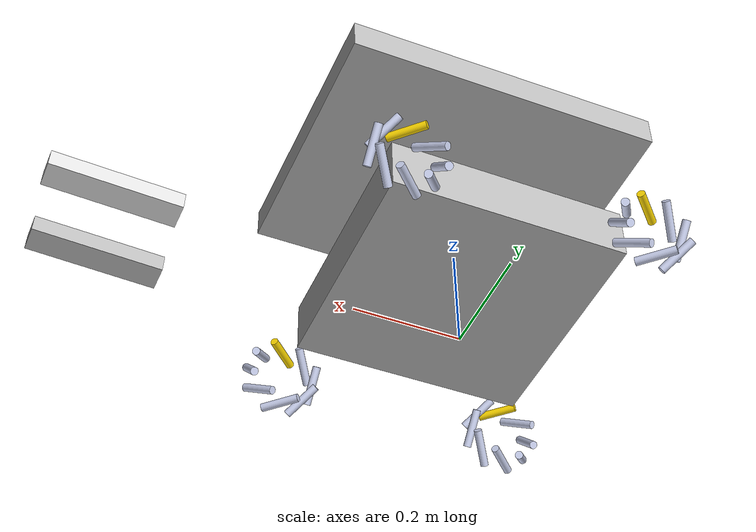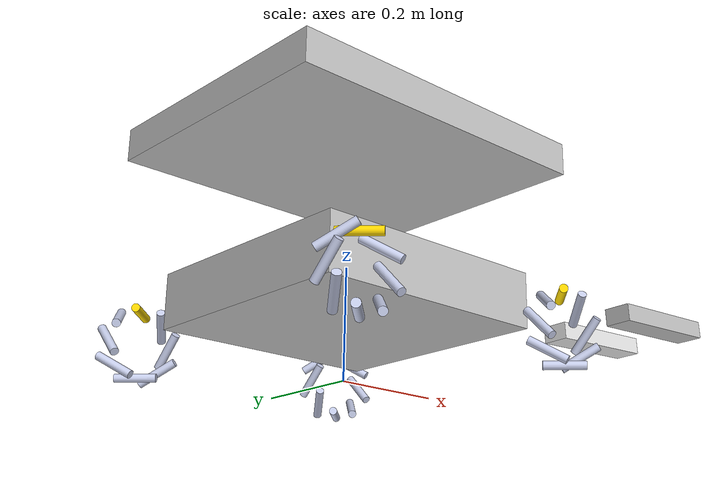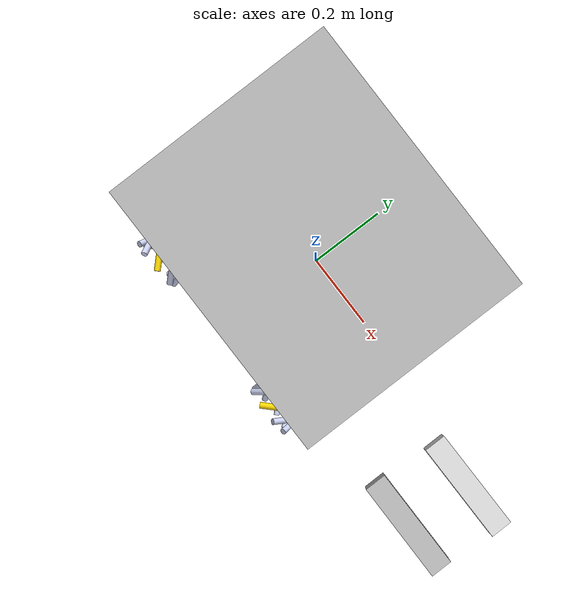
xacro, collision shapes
<?xml version="1.0"?>
<robot name="rangka_krai_2027" xmlns:xacro="http://www.ros.org/wiki/xacro">
  <xacro:arg name="chassis_mass" default="5.0"/>
  <xacro:arg name="wheel_mass" default="0.20"/>
  <xacro:arg name="roller_mass" default="0.012"/>
  <xacro:arg name="left_claw_mass" default="0.25"/>
  <xacro:arg name="left_claw_slide" default="0.24919445"/>
  <xacro:property name="chassis_mass" value="$(arg chassis_mass)"/>
  <xacro:property name="wheel_mass" value="$(arg wheel_mass)"/>
  <xacro:property name="roller_mass" value="$(arg roller_mass)"/>
  <xacro:property name="left_claw_mass" value="$(arg left_claw_mass)"/>
  <xacro:property name="left_claw_slide" value="$(arg left_claw_slide)"/>

  <xacro:macro name="cad_visual" params="mesh xyz rpy rgba material">
    <visual>
      <origin xyz="${xyz}" rpy="${rpy}"/>
      <geometry><mesh filename="package://rangka_krai_2027/meshes/${mesh}"/></geometry>
      <material name="${material}"><color rgba="${rgba}"/></material>
    </visual>
  </xacro:macro>

  <link name="base_footprint"/>
  <link name="base_link">
    <inertial>
      <origin xyz="-0.220346 0.297827 0.447375" rpy="0.026304529 0.044612954 1.5719697"/>
      <mass value="${chassis_mass}"/>
      <inertia ixx="${chassis_mass * (0.601**2 + 0.580**2) / 12}" ixy="0" ixz="0"
               iyy="${chassis_mass * (1.604**2 + 0.580**2) / 12}" iyz="0"
               izz="${chassis_mass * (1.604**2 + 0.601**2) / 12}"/>
    </inertial>
    <collision name="lower_frame_collision">
      <origin xyz="-0.21929904 0.31153824 0.43756421" rpy="0.026304529 0.044612954 1.5719697"/>
      <geometry><box size="0.44 0.44 0.10"/></geometry>
    </collision>
    <collision name="upper_frame_collision">
      <origin xyz="-0.21194928 0.32403004 0.71718885" rpy="0.026304529 0.044612954 1.5719697"/>
      <geometry><box size="0.60 0.50 0.06"/></geometry>
    </collision>
    <collision name="fixed_right_claw_jaw_collision">
      <origin xyz="-0.0072201297 0.92811735 0.44151283" rpy="0 0 0"/>
      <geometry><box size="0.052754379 0.24268503 0.032956245"/></geometry>
    </collision>
    <xacro:cad_visual mesh="SLL_MIR_1__Solid1.stl" xyz="-0.409375 -0.138105 0.682635" rpy="1.60201 -0.0446886 -1.57294" rgba="0.74902 0.74902 0.74902 1" material="0_749020_0_749020_0_749020_0_000000_0_000000"/>
    <xacro:cad_visual mesh="part1_1__Solid1.stl" xyz="-0.419123 -0.217028 0.704995" rpy="-0.0261648 -0.0446886 -1.57294" rgba="0.74902 0.74902 0.74902 1" material="0_749020_0_749020_0_749020_0_000000_0_000000"/>
    <xacro:cad_visual mesh="_5656_1__Solid1.stl" xyz="-0.307375 -0.266275 0.705912" rpy="-0.0261648 -0.0446887 -1.57294" rgba="0.435294 0.239216 0.239216 1" material="0_435294_0_239216_0_239216_0_000000_0_000000"/>
    <xacro:cad_visual mesh="_5656_MIR7_1__Solid1.stl" xyz="-0.0525689 0.817865 0.437094" rpy="-3.11543 0.0446886 1.56865" rgba="0.435294 0.239216 0.239216 1" material="0_435294_0_239216_0_239216_0_000000_0_000000"/>
    <xacro:cad_visual mesh="SLL_1__Solid1.stl" xyz="-0.409473 -0.171364 0.685665" rpy="1.59696 0.0446886 1.56865" rgba="0.74902 0.74902 0.74902 1" material="0_749020_0_749020_0_749020_0_000000_0_000000"/>
    <xacro:cad_visual mesh="pg45_MIR_MIR_1__Solid1.stl" xyz="-0.478747 0.0896267 0.38732" rpy="1.59894 -0.0257561 3.1383" rgba="0.752941 0.752941 0.752941 1" material="0_752941_0_752941_0_752941_0_000000_0_000000"/>
    <xacro:cad_visual mesh="SLL_MIR_1__Solid1.stl" xyz="-0.409373 -0.124689 0.683578" rpy="1.54463 -0.0446886 -1.57294" rgba="0.74902 0.74902 0.74902 1" material="0_749020_0_749020_0_749020_0_000000_0_000000"/>
    <xacro:cad_visual mesh="_5656_MIR4_MIR_1__Solid1.stl" xyz="-0.429181 -0.265872 0.709096" rpy="-0.0261648 -0.0446887 -1.57294" rgba="0.435294 0.239216 0.239216 1" material="0_435294_0_239216_0_239216_0_000000_0_000000"/>
    <xacro:cad_visual mesh="Part2_1__Solid1.stl" xyz="-0.28396 -0.489148 0.725263" rpy="1.59696 0.0446887 1.56865" rgba="0.8 0.8 0.8 1" material="0_800000_0_800000_0_800000_0_000000_0_000000"/>
    <xacro:cad_visual mesh="pg45_MIR1_1__Solid1.stl" xyz="0.0357221 0.0879262 0.373968" rpy="1.54266 0.0261387 -0.00331382" rgba="0.752941 0.752941 0.752941 1" material="0_752941_0_752941_0_752941_0_000000_0_000000"/>
    <xacro:cad_visual mesh="_5656_MIR4_1__Solid1.stl" xyz="-0.257393 -0.266441 0.704605" rpy="3.11543 -0.0446886 -1.57294" rgba="0.435294 0.239216 0.239216 1" material="0_435294_0_239216_0_239216_0_000000_0_000000"/>
    <xacro:cad_visual mesh="lintasan_gear_MIR_2__Solid1.stl" xyz="-0.00340719 0.365125 0.46175" rpy="-1.59696 -0.0446886 -1.57294" rgba="0.0980392 0.0196078 0.0196078 1" material="0_098039_0_019608_0_019608_0_000000_0_000000"/>
    <xacro:cad_visual mesh="Part4_1__Solid1.stl" xyz="-0.30481 0.168273 0.69694" rpy="-1.52552 -0.0251412 3.11612" rgba="0.74902 0.74902 0.74902 1" material="0_749020_0_749020_0_749020_0_000000_0_000000"/>
    <xacro:cad_visual mesh="bracket_pg_rantai_1__Solid1.stl" xyz="-0.219595 0.170682 0.443939" rpy="1.54473 -0.0446886 -1.57294" rgba="0.8 0.8 0.8 1" material="0_800000_0_800000_0_800000_0_000000_0_000000"/>
    <xacro:cad_visual mesh="part6_1__Solid1.stl" xyz="-0.349173 -0.121265 0.718809" rpy="1.52609 -0.031184 -0.000749717" rgba="0 0 0 1" material="0_000000_0_000000_0_000000_0_000000_0_000000"/>
    <xacro:cad_visual mesh="timing_pulley___MIR_MIR_1__Solid1.stl" xyz="-0.418528 -0.208054 0.726608" rpy="-1.59696 -0.0446886 -1.57294" rgba="0.792157 0.819608 0.933333 1" material="0_792157_0_819608_0_933333_0_000000_0_000000"/>
    <xacro:cad_visual mesh="SLL_1__Solid1.stl" xyz="-0.409456 -0.158036 0.684626" rpy="1.59696 0.0446886 1.56865" rgba="0.74902 0.74902 0.74902 1" material="0_749020_0_749020_0_749020_0_000000_0_000000"/>
    <xacro:cad_visual mesh="_9459859_MIR_MIR_MIR_1__Solid1.stl" xyz="-0.39873 -0.295049 0.729626" rpy="-0.0261648 -0.0446886 -1.57294" rgba="1 1 1 1" material="1_000000_1_000000_1_000000_0_000000_0_000000"/>
    <xacro:cad_visual mesh="rangka_krai_2027MOTOR_PG36_PART_2_MIR_1__Solid1.stl" xyz="-0.282683 0.480358 0.489423" rpy="2.61225 1.51902 -2.10287" rgba="0.74902 0.74902 0.74902 1" material="0_749020_0_749020_0_749020_0_000000_0_000000"/>
    <xacro:cad_visual mesh="rangka_krai_2027MOTOR_PG36_PART_2_MIR_1__Solid1_1.stl" xyz="-0.282683 0.480358 0.489423" rpy="2.61225 1.51902 -2.10287" rgba="0.74902 0.74902 0.74902 1" material="0_749020_0_749020_0_749020_0_000000_0_000000"/>
    <xacro:cad_visual mesh="rangka_krai_2027MOTOR_PG36_PART_2_MIR_1__Solid1_2.stl" xyz="-0.282683 0.480358 0.489423" rpy="2.61225 1.51902 -2.10287" rgba="0.996078 0.996078 1 1" material="0_996078_0_996078_1_000000_0_000000_0_000000"/>
    <xacro:cad_visual mesh="_2323_1__Solid1.stl" xyz="-0.296657 -0.212167 0.726397" rpy="0.0447039 -0.0261387 3.13828" rgba="0.8 0.8 0.8 1" material="0_800000_0_800000_0_800000_0_000000_0_000000"/>
    <xacro:cad_visual mesh="rangka_krai_2027SLSLSLSL_MIR_1__Solid1.stl" xyz="-0.39392 0.449751 0.471185" rpy="-0.0261648 -0.0446886 -1.57294" rgba="0.427451 0.329412 0.329412 1" material="0_427451_0_329412_0_329412_0_000000_0_000000"/>
    <xacro:cad_visual mesh="SLSLSLSL_1__Solid1.stl" xyz="-0.0281428 0.448538 0.461622" rpy="3.11543 -0.0446886 -1.57294" rgba="0.427451 0.329412 0.329412 1" material="0_427451_0_329412_0_329412_0_000000_0_000000"/>
    <xacro:cad_visual mesh="Part13_MIR1_1__Solid1.stl" xyz="0.00855835 0.526238 0.325066" rpy="-3.11543 0.0446886 1.56865" rgba="1 0.384314 0 1" material="1_000000_0_384314_0_000000_0_000000_0_000000"/>
    <xacro:cad_visual mesh="lintasan_gear_MIR_2__Solid1.stl" xyz="-0.192934 -0.00635356 0.696705" rpy="-1.59696 -0.0446886 -1.57294" rgba="0.0980392 0.0196078 0.0196078 1" material="0_098039_0_019608_0_019608_0_000000_0_000000"/>
    <xacro:cad_visual mesh="ISO_10799_2_20x20x2___380_1__Solid1.stl" xyz="-0.40845 0.488865 0.449793" rpy="-1.59696 -0.0446886 -1.57294" rgba="0.8 0.8 0.8 1" material="0_800000_0_800000_0_800000_0_000000_0_000000"/>
    <xacro:cad_visual mesh="_222_1__Solid1.stl" xyz="-0.418576 -0.230756 0.727623" rpy="2.00058 0.0446886 1.56865" rgba="0.968627 1 0 1" material="0_968627_1_000000_0_000000_0_000000_0_000000"/>
    <xacro:cad_visual mesh="pg45_MIR_1__Solid1.stl" xyz="-0.477804 0.529186 0.367663" rpy="1.63206 -0.0257561 3.1383" rgba="0.752941 0.752941 0.752941 1" material="0_752941_0_752941_0_752941_0_000000_0_000000"/>
    <xacro:cad_visual mesh="pg45_1__Solid1.stl" xyz="0.0366649 0.527486 0.354311" rpy="1.50953 0.0261387 -0.00331382" rgba="0.752941 0.752941 0.752941 1" material="0_752941_0_752941_0_752941_0_000000_0_000000"/>
    <xacro:cad_visual mesh="Part2_MIR1_1__Solid1.stl" xyz="-0.0318345 1.04149 0.436575" rpy="-1.54463 0.0446688 1.56865" rgba="0.8 0.8 0.8 1" material="0_800000_0_800000_0_800000_0_000000_0_000000"/>
    <xacro:cad_visual mesh="_5656_MIR6_MIR_1__Solid1.stl" xyz="-0.00258623 0.817699 0.435787" rpy="0.0261648 0.0446886 1.56865" rgba="0.435294 0.239216 0.239216 1" material="0_435294_0_239216_0_239216_0_000000_0_000000"/>
    <xacro:cad_visual mesh="Part13_MIR1_MIR_MIR_1__Solid1.stl" xyz="-0.452204 0.0881985 0.356656" rpy="3.11581 -0.0446886 -1.57294" rgba="1 0.384314 0 1" material="1_000000_0_384314_0_000000_0_000000_0_000000"/>
    <xacro:cad_visual mesh="_5656_1__Solid1.stl" xyz="-0.314644 0.189944 0.686217" rpy="-0.0261648 -0.0446901 -1.57294" rgba="0.435294 0.239216 0.239216 1" material="0_435294_0_239216_0_239216_0_000000_0_000000"/>
    <xacro:cad_visual mesh="_2323_1__Solid1.stl" xyz="-0.27668 -0.212261 0.725269" rpy="0.0447039 -0.0261387 3.13828" rgba="0.8 0.8 0.8 1" material="0_800000_0_800000_0_800000_0_000000_0_000000"/>
    <xacro:cad_visual mesh="Part4_1__Solid1.stl" xyz="-0.307087 -0.253841 0.715362" rpy="-1.6155 0.0261386 -0.00331451" rgba="0.74902 0.74902 0.74902 1" material="0_749020_0_749020_0_749020_0_000000_0_000000"/>
    <xacro:cad_visual mesh="rangka_krai_2027MOTOR_PG36_PART_2_MIR_1__Solid1_2.stl" xyz="-0.314031 0.0883138 0.735205" rpy="-2.99127 -1.39538 1.41943" rgba="0.996078 0.996078 1 1" material="0_996078_0_996078_1_000000_0_000000_0_000000"/>
    <xacro:cad_visual mesh="rangka_krai_2027MOTOR_PG36_PART_2_MIR_1__Solid1_1.stl" xyz="-0.314031 0.0883138 0.735205" rpy="-2.99127 -1.39538 1.41943" rgba="0.74902 0.74902 0.74902 1" material="0_749020_0_749020_0_749020_0_000000_0_000000"/>
    <xacro:cad_visual mesh="rangka_krai_2027MOTOR_PG36_PART_2_MIR_1__Solid1.stl" xyz="-0.314031 0.0883138 0.735205" rpy="-2.99127 -1.39538 1.41943" rgba="0.74902 0.74902 0.74902 1" material="0_749020_0_749020_0_749020_0_000000_0_000000"/>
    <xacro:cad_visual mesh="timing_pulley___MIR_1__Solid1.stl" xyz="0.011323 -0.209479 0.71537" rpy="-1.59696 -0.0446886 -1.57294" rgba="0.792157 0.819608 0.933333 1" material="0_792157_0_819608_0_933333_0_000000_0_000000"/>
    <xacro:cad_visual mesh="bracket_pg_rantai_1__Solid1.stl" xyz="-0.203449 0.0879473 0.732314" rpy="1.54463 -0.0446886 -1.57294" rgba="0.8 0.8 0.8 1" material="0_800000_0_800000_0_800000_0_000000_0_000000"/>
    <xacro:cad_visual mesh="_222_MIR_1__Solid1.stl" xyz="0.0112612 -0.238285 0.716658" rpy="-2.54791 0.0446886 1.56865" rgba="0.968627 1 0 1" material="0_968627_1_000000_0_000000_0_000000_0_000000"/>
    <xacro:cad_visual mesh="ISO_10799_2_20x20x2___380_1__Solid1.stl" xyz="-0.0255983 0.0815822 0.620891" rpy="-1.54463 0.0446886 1.56865" rgba="0.8 0.8 0.8 1" material="0_800000_0_800000_0_800000_0_000000_0_000000"/>
    <xacro:cad_visual mesh="MOTOR_PG36_PART_2_1__Solid1.stl" xyz="-0.138069 0.479878 0.485642" rpy="-0.529343 1.51902 -2.10287" rgba="0.996078 0.996078 1 1" material="0_996078_0_996078_1_000000_0_000000_0_000000"/>
    <xacro:cad_visual mesh="MOTOR_PG36_PART_2_1__Solid1_1.stl" xyz="-0.138069 0.479878 0.485642" rpy="-0.529343 1.51902 -2.10287" rgba="0.74902 0.74902 0.74902 1" material="0_749020_0_749020_0_749020_0_000000_0_000000"/>
    <xacro:cad_visual mesh="MOTOR_PG36_PART_2_1__Solid1_2.stl" xyz="-0.138069 0.479878 0.485642" rpy="-0.529343 1.51902 -2.10287" rgba="0.74902 0.74902 0.74902 1" material="0_749020_0_749020_0_749020_0_000000_0_000000"/>
    <xacro:cad_visual mesh="BELT_1__Solid1.stl" xyz="0.0211193 -0.213636 0.718004" rpy="1.6155 -0.0261387 3.13828" rgba="0 0 0 1" material="0_000000_0_000000_0_000000_0_000000_0_000000"/>
    <xacro:cad_visual mesh="_9459859_MIR_MIR_1__Solid1.stl" xyz="-0.286921 -0.29542 0.726702" rpy="3.11543 -0.0446887 -1.57294" rgba="1 1 1 1" material="1_000000_1_000000_1_000000_0_000000_0_000000"/>
    <xacro:cad_visual mesh="Part4_MIR1_1__Solid1.stl" xyz="-0.052332 0.806323 0.447617" rpy="-1.6155 0.0261387 -0.00331382" rgba="0.74902 0.74902 0.74902 1" material="0_749020_0_749020_0_749020_0_000000_0_000000"/>
    <xacro:cad_visual mesh="Part13_MIR1_MIR_1__Solid1.stl" xyz="-0.451261 0.527758 0.336999" rpy="0.0257819 0.0446886 1.56865" rgba="1 0.384314 0 1" material="1_000000_0_384314_0_000000_0_000000_0_000000"/>
    <xacro:cad_visual mesh="_9459859_MIR_MIR_MIR1_1__Solid1.stl" xyz="-0.0319864 0.84866 0.455204" rpy="0.0261648 0.0446886 1.56865" rgba="1 1 1 1" material="1_000000_1_000000_1_000000_0_000000_0_000000"/>
    <xacro:cad_visual mesh="part1_MIR_1__Solid1.stl" xyz="0.0107282 -0.218452 0.693756" rpy="3.11543 -0.0446886 -1.57294" rgba="0.74902 0.74902 0.74902 1" material="0_749020_0_749020_0_749020_0_000000_0_000000"/>
    <xacro:cad_visual mesh="Part13_MIR1_MIR1_1__Solid1.stl" xyz="0.00761564 0.0866787 0.344722" rpy="-0.0261648 -0.0446886 -1.57294" rgba="1 0.384314 0 1" material="1_000000_0_384314_0_000000_0_000000_0_000000"/>
    <xacro:cad_visual mesh="ISO_10799_2_20x20x2___430_1__Solid1.stl" xyz="-0.00291603 0.802208 0.425136" rpy="1.54463 -0.0446886 -1.57294" rgba="0.745098 0.737255 0.729412 1" material="0_745098_0_737255_0_729412_0_000000_0_000000"/>
    <xacro:cad_visual mesh="ISO_10799_2_20x20x2___500_2__Solid1.stl" xyz="-0.0139624 0.312732 0.447287" rpy="1.6155 -0.0261387 3.13828" rgba="0.745098 0.737255 0.729412 1" material="0_745098_0_737255_0_729412_0_000000_0_000000"/>
    <xacro:cad_visual mesh="ISO_10799_2_20x20x2___500_1__Solid1.stl" xyz="-0.422749 0.81359 0.435666" rpy="1.52609 0.0261387 -0.00331382" rgba="0.745098 0.737255 0.729412 1" material="0_745098_0_737255_0_729412_0_000000_0_000000"/>
    <xacro:cad_visual mesh="pg45_MIR1_1__Solid1.stl" xyz="-0.239917 0.170749 0.444468" rpy="2.08687 -0.026043 3.13828" rgba="0.752941 0.752941 0.752941 1" material="0_752941_0_752941_0_752941_0_000000_0_000000"/>
    <xacro:cad_visual mesh="lintasan_gear_MIR_MIR_1__Solid1.stl" xyz="-0.426742 0.366527 0.472818" rpy="-1.59696 -0.0446886 -1.57294" rgba="0.0980392 0.0196078 0.0196078 1" material="0_098039_0_019608_0_019608_0_000000_0_000000"/>
    <xacro:cad_visual mesh="MGN12H_430MM_Assembly_1__Solid1.stl" xyz="-0.437238 0.840582 0.471923" rpy="1.54463 -0.0446886 -1.57294" rgba="0.964706 0.964706 0.952941 1" material="0_964706_0_964706_0_952941_0_000000_0_000000"/>
    <xacro:cad_visual mesh="baut_MIR_MIR2_MIR_1__Solid1.stl" xyz="-0.462424 0.592783 0.476611" rpy="-1.59696 -0.0446886 -1.57294" rgba="0.74902 0.74902 0.74902 1" material="0_749020_0_749020_0_749020_0_000000_0_000000"/>
    <xacro:cad_visual mesh="baut_MIR_MIR4_1__Solid1.stl" xyz="-0.437542 0.694102 0.458915" rpy="-1.54463 0.0446886 1.56865" rgba="0.74902 0.74902 0.74902 1" material="0_749020_0_749020_0_749020_0_000000_0_000000"/>
    <xacro:cad_visual mesh="baut_MIR_MIR3_MIR_1__Solid1.stl" xyz="-0.438399 0.693162 0.426249" rpy="1.59696 0.0446886 1.56865" rgba="0.74902 0.74902 0.74902 1" material="0_749020_0_749020_0_749020_0_000000_0_000000"/>
    <xacro:cad_visual mesh="rolllll_MIR7_1__Solid1.stl" xyz="-0.459001 0.59009 0.416561" rpy="1.54463 -0.0446886 -1.57294" rgba="1 0.933333 0 1" material="1_000000_0_933333_0_000000_0_000000_0_000000"/>
    <xacro:cad_visual mesh="rolllll_MIR8_MIR_MIR_MIR_1__Solid1.stl" xyz="-0.414576 0.642949 0.425549" rpy="1.54463 -0.0446886 -1.57294" rgba="1 0.933333 0 1" material="1_000000_0_933333_0_000000_0_000000_0_000000"/>
    <xacro:cad_visual mesh="LINTASANANNNNN_1__Solid1.stl" xyz="-0.432427 0.621982 0.472393" rpy="1.54463 -0.0446886 -1.57294" rgba="0.74902 0.74902 0.74902 1" material="0_749020_0_749020_0_749020_0_000000_0_000000"/>
    <xacro:cad_visual mesh="rolllll_MIR8_1__Solid1.stl" xyz="-0.417299 0.524136 0.433243" rpy="-1.59696 -0.0446886 -1.57294" rgba="1 0.933333 0 1" material="1_000000_0_933333_0_000000_0_000000_0_000000"/>
    <xacro:cad_visual mesh="baut_MIR_MIR1_MIR1_1__Solid1.stl" xyz="-0.463924 0.625072 0.415128" rpy="1.59696 0.0446886 1.56865" rgba="0.74902 0.74902 0.74902 1" material="0_749020_0_749020_0_749020_0_000000_0_000000"/>
    <xacro:cad_visual mesh="LL_1__Solid1.stl" xyz="-0.407436 0.621899 0.47174" rpy="1.54463 -0.0446886 -1.57294" rgba="0.74902 0.74902 0.74902 1" material="0_749020_0_749020_0_749020_0_000000_0_000000"/>
    <xacro:cad_visual mesh="rolllll_2__Solid1.stl" xyz="-0.412913 0.525065 0.465817" rpy="1.54463 -0.0446886 -1.57294" rgba="1 0.933333 0 1" material="1_000000_0_933333_0_000000_0_000000_0_000000"/>
    <xacro:cad_visual mesh="baut_MIR_MIR2_1__Solid1.stl" xyz="-0.463999 0.590107 0.416692" rpy="1.54463 -0.0446886 -1.57294" rgba="0.74902 0.74902 0.74902 1" material="0_749020_0_749020_0_749020_0_000000_0_000000"/>
    <xacro:cad_visual mesh="baut_MIR_3__Solid1.stl" xyz="-0.437905 0.525148 0.466471" rpy="-1.59696 -0.0446886 -1.57294" rgba="0.74902 0.74902 0.74902 1" material="0_749020_0_749020_0_749020_0_000000_0_000000"/>
    <xacro:cad_visual mesh="rolllll_MIR6_1__Solid1.stl" xyz="-0.457351 0.627731 0.474917" rpy="-1.54463 0.0446886 1.56865" rgba="1 0.933333 0 1" material="1_000000_0_933333_0_000000_0_000000_0_000000"/>
    <xacro:cad_visual mesh="lintasan_1_1__Solid1.stl" xyz="-0.457418 0.622065 0.473046" rpy="1.54463 -0.0446886 -1.57294" rgba="0.74902 0.74902 0.74902 1" material="0_749020_0_749020_0_749020_0_000000_0_000000"/>
    <xacro:cad_visual mesh="rolllll_MIR8_MIR_MIR1_1__Solid1.stl" xyz="-0.413657 0.644511 0.460502" rpy="-1.59696 -0.0446886 -1.57294" rgba="1 0.933333 0 1" material="1_000000_0_933333_0_000000_0_000000_0_000000"/>
    <xacro:cad_visual mesh="baut_MIR_MIR5_MIR_1__Solid1.stl" xyz="-0.439568 0.643032 0.426202" rpy="1.59696 0.0446886 1.56865" rgba="0.74902 0.74902 0.74902 1" material="0_749020_0_749020_0_749020_0_000000_0_000000"/>
    <xacro:cad_visual mesh="rolllll_MIR6_MIR1_1__Solid1.stl" xyz="-0.458926 0.625055 0.414998" rpy="1.59696 0.0446886 1.56865" rgba="1 0.933333 0 1" material="1_000000_0_933333_0_000000_0_000000_0_000000"/>
    <xacro:cad_visual mesh="rolllll_MIR8_MIR_MIR_1__Solid1.stl" xyz="-0.414726 0.57302 0.428676" rpy="1.59696 0.0446886 1.56865" rgba="1 0.933333 0 1" material="1_000000_0_933333_0_000000_0_000000_0_000000"/>
    <xacro:cad_visual mesh="rolllll_MIR8_MIR_1__Solid1.stl" xyz="-0.413408 0.693079 0.425596" rpy="-1.54463 0.0446886 1.56865" rgba="1 0.933333 0 1" material="1_000000_0_933333_0_000000_0_000000_0_000000"/>
    <xacro:cad_visual mesh="baut_MIR_MIR6_1__Solid1.stl" xyz="-0.438649 0.644593 0.461156" rpy="-1.54463 0.0446886 1.56865" rgba="0.74902 0.74902 0.74902 1" material="0_749020_0_749020_0_749020_0_000000_0_000000"/>
    <xacro:cad_visual mesh="baut_MIR_MIR3_1__Solid1.stl" xyz="-0.44229 0.524219 0.433897" rpy="1.54463 -0.0446886 -1.57294" rgba="0.74902 0.74902 0.74902 1" material="0_749020_0_749020_0_749020_0_000000_0_000000"/>
    <xacro:cad_visual mesh="baut_MIR_3__Solid1.stl" xyz="-0.437798 0.57466 0.464257" rpy="-1.59696 -0.0446886 -1.57294" rgba="0.74902 0.74902 0.74902 1" material="0_749020_0_749020_0_749020_0_000000_0_000000"/>
    <xacro:cad_visual mesh="rolllll_MIR7_MIR_1__Solid1.stl" xyz="-0.457426 0.592766 0.476481" rpy="-1.59696 -0.0446886 -1.57294" rgba="1 0.933333 0 1" material="1_000000_0_933333_0_000000_0_000000_0_000000"/>
    <xacro:cad_visual mesh="baut_MIR_MIR1_1__Solid1.stl" xyz="-0.462349 0.627748 0.475048" rpy="-1.54463 0.0446886 1.56865" rgba="0.74902 0.74902 0.74902 1" material="0_749020_0_749020_0_749020_0_000000_0_000000"/>
    <xacro:cad_visual mesh="rolllll_MIR8_MIR_1__Solid1.stl" xyz="-0.412807 0.574577 0.463603" rpy="-1.54463 0.0446886 1.56865" rgba="1 0.933333 0 1" material="1_000000_0_933333_0_000000_0_000000_0_000000"/>
    <xacro:cad_visual mesh="rolllll_MIR9_1__Solid1.stl" xyz="-0.412551 0.69402 0.458262" rpy="1.59696 0.0446886 1.56865" rgba="1 0.933333 0 1" material="1_000000_0_933333_0_000000_0_000000_0_000000"/>
    <xacro:cad_visual mesh="baut_MIR_MIR5_1__Solid1.stl" xyz="-0.439718 0.573102 0.42933" rpy="1.54463 -0.0446886 -1.57294" rgba="0.74902 0.74902 0.74902 1" material="0_749020_0_749020_0_749020_0_000000_0_000000"/>
    <xacro:cad_visual mesh="baut_MIR2_MIR_MIR1_MIR1_1__Solid1.stl" xyz="0.00688114 0.226865 0.681479" rpy="1.59735 -0.177217 1.5628" rgba="1 0.533333 0 1" material="1_000000_0_533333_0_000000_0_000000_0_000000"/>
    <xacro:cad_visual mesh="baut_MIR1_MIR2_MIR1_1__Solid1.stl" xyz="0.0305877 0.207181 0.634171" rpy="-1.54465 0.0293551 1.56825" rgba="1 0.517647 0 1" material="1_000000_0_517647_0_000000_0_000000_0_000000"/>
    <xacro:cad_visual mesh="lintasan_2_MIR1_MIR1_1__Solid1.stl" xyz="0.00205483 0.180468 0.694069" rpy="1.59696 0.0446886 1.56865" rgba="0.74902 0.74902 0.74902 1" material="0_749020_0_749020_0_749020_0_000000_0_000000"/>
    <xacro:cad_visual mesh="rolllll_MIR1_MIR1_MIR1_1__Solid1.stl" xyz="0.00571521 0.21852 0.637941" rpy="-1.54466 0.00708664 1.56767" rgba="1 0.933333 0 1" material="1_000000_0_933333_0_000000_0_000000_0_000000"/>
    <xacro:cad_visual mesh="baut_MIR2_MIR_MIR1_MIR1_1__Solid1.stl" xyz="0.00596213 0.225304 0.646526" rpy="1.59735 -0.177217 1.5628" rgba="1 0.533333 0 1" material="1_000000_0_533333_0_000000_0_000000_0_000000"/>
    <xacro:cad_visual mesh="baut_MIR2_MIR_MIR1_MIR1_1__Solid1.stl" xyz="0.00705255 0.306785 0.677905" rpy="1.59724 -0.151186 1.5635" rgba="1 0.533333 0 1" material="1_000000_0_533333_0_000000_0_000000_0_000000"/>
    <xacro:cad_visual mesh="rolllll_MIR2_MIR_MIR1_MIR1_1__Solid1.stl" xyz="-0.0190292 0.225386 0.647179" rpy="-1.59735 0.177217 -1.57879" rgba="1 0.933333 0 1" material="1_000000_0_933333_0_000000_0_000000_0_000000"/>
    <xacro:cad_visual mesh="baut_MIR2_MIR2_MIR1_1__Solid1.stl" xyz="0.0320882 0.174892 0.695654" rpy="1.54455 -0.0892154 -1.57177" rgba="1 0.517647 0 1" material="1_000000_0_517647_0_000000_0_000000_0_000000"/>
    <xacro:cad_visual mesh="baut_MIR2_MIR_MIR1_MIR1_1__Solid1.stl" xyz="0.00613353 0.305224 0.642952" rpy="1.59735 -0.177217 1.5628" rgba="1 0.533333 0 1" material="1_000000_0_533333_0_000000_0_000000_0_000000"/>
    <xacro:cad_visual mesh="baut_MIR1_MIR_MIR1_MIR1_1__Solid1.stl" xyz="0.0305128 0.172216 0.635734" rpy="-1.59715 -0.126732 -1.57078" rgba="1 0.517647 0 1" material="1_000000_0_517647_0_000000_0_000000_0_000000"/>
    <xacro:cad_visual mesh="lintasan_1_MIR1_MIR1_1__Solid1.stl" xyz="0.0270233 0.180423 0.692535" rpy="1.59694 0.014824 1.56787" rgba="0.74902 0.74902 0.74902 1" material="0_749020_0_749020_0_749020_0_000000_0_000000"/>
    <xacro:cad_visual mesh="rolllll_MIR_MIR_MIR1_MIR1_1__Solid1.stl" xyz="0.00552143 0.172299 0.636388" rpy="-1.59721 -0.1456 -1.57028" rgba="1 0.933333 0 1" material="1_000000_0_933333_0_000000_0_000000_0_000000"/>
    <xacro:cad_visual mesh="rolllll_MIR_MIR2_MIR1_1__Solid1.stl" xyz="0.00709688 0.174975 0.696307" rpy="1.54466 -0.00708664 -1.57392" rgba="1 0.933333 0 1" material="1_000000_0_933333_0_000000_0_000000_0_000000"/>
    <xacro:cad_visual mesh="baut_MIR2_MIR2_MIR1_1__Solid1_1.stl" xyz="0.00655977 0.0770148 0.68818" rpy="1.54445 0.125772 -1.57742" rgba="1 0.533333 0 1" material="1_000000_0_533333_0_000000_0_000000_0_000000"/>
    <xacro:cad_visual mesh="rolllll_MIR5_MIR1_1__Solid1.stl" xyz="-0.0184316 0.0770976 0.688833" rpy="1.59699 -0.0632239 1.56583" rgba="1 0.933333 0 1" material="1_000000_0_933333_0_000000_0_000000_0_000000"/>
    <xacro:cad_visual mesh="lintasan_3_MIR1_MIR1_1__Solid1.stl" xyz="-0.0229365 0.180551 0.694722" rpy="1.59696 0.0446886 1.56865" rgba="0.74902 0.74902 0.74902 1" material="0_749020_0_749020_0_749020_0_000000_0_000000"/>
    <xacro:cad_visual mesh="baut_MIR2_MIR2_MIR1_1__Solid1_1.stl" xyz="0.00581215 0.155374 0.649653" rpy="1.54449 -0.113747 -1.57112" rgba="1 0.533333 0 1" material="1_000000_0_533333_0_000000_0_000000_0_000000"/>
    <xacro:cad_visual mesh="rolllll_MIR3_MIR1_MIR1_1__Solid1.stl" xyz="-0.0181102 0.226948 0.682132" rpy="1.54424 0.177217 -1.57879" rgba="1 0.933333 0 1" material="1_000000_0_933333_0_000000_0_000000_0_000000"/>
    <xacro:cad_visual mesh="baut_MIR2_MIR2_MIR1_1__Solid1_1.stl" xyz="0.00564075 0.0754537 0.653227" rpy="1.54466 -0.00402267 -1.574" rgba="1 0.533333 0 1" material="1_000000_0_533333_0_000000_0_000000_0_000000"/>
    <xacro:cad_visual mesh="rolllll_MIR5_MIR1_1__Solid1.stl" xyz="0.00717187 0.20994 0.694744" rpy="1.59694 0.0066786 1.56766" rgba="1 0.933333 0 1" material="1_000000_0_933333_0_000000_0_000000_0_000000"/>
    <xacro:cad_visual mesh="baut_MIR2_MIR2_MIR1_1__Solid1_1.stl" xyz="0.00673117 0.156935 0.684606" rpy="1.54435 0.151622 -1.5781" rgba="1 0.533333 0 1" material="1_000000_0_533333_0_000000_0_000000_0_000000"/>
    <xacro:cad_visual mesh="rolllll_MIR2_MIR_MIR1_MIR1_1__Solid1.stl" xyz="-0.0188578 0.305306 0.643605" rpy="-1.59735 0.177217 -1.57879" rgba="1 0.933333 0 1" material="1_000000_0_933333_0_000000_0_000000_0_000000"/>
    <xacro:cad_visual mesh="rolllll_MIR5_MIR1_1__Solid1.stl" xyz="-0.0182602 0.157018 0.685259" rpy="1.59711 -0.114113 1.56449" rgba="1 0.933333 0 1" material="1_000000_0_933333_0_000000_0_000000_0_000000"/>
    <xacro:cad_visual mesh="rolllll_MIR2_MIR2_MIR1_1__Solid1.stl" xyz="-0.0193506 0.0755365 0.65388" rpy="-1.54461 -0.0616365 1.56587" rgba="1 0.933333 0 1" material="1_000000_0_933333_0_000000_0_000000_0_000000"/>
    <xacro:cad_visual mesh="rolllll_MIR2_MIR2_MIR1_1__Solid1.stl" xyz="-0.0191792 0.155456 0.650306" rpy="-1.54445 0.124827 1.57076" rgba="1 0.933333 0 1" material="1_000000_0_933333_0_000000_0_000000_0_000000"/>
    <xacro:cad_visual mesh="baut_MIR4_MIR1_1__Solid1.stl" xyz="0.0321632 0.209857 0.69409" rpy="1.59694 0.00157798 1.56752" rgba="1 0.517647 0 1" material="1_000000_0_517647_0_000000_0_000000_0_000000"/>
    <xacro:cad_visual mesh="rolllll_MIR3_MIR1_MIR1_1__Solid1.stl" xyz="-0.0179388 0.306867 0.678558" rpy="1.54424 0.177217 -1.57879" rgba="1 0.933333 0 1" material="1_000000_0_933333_0_000000_0_000000_0_000000"/>
    <xacro:cad_visual mesh="Timing_Belt_88XL_v4_1__Solid1.stl" xyz="-0.418464 -0.178484 0.725286" rpy="3.09683 0.056372 -0.00466821" rgba="0.25098 0.25098 0.25098 1" material="0_250980_0_250980_0_250980_0_000000_0_000000"/>
    <xacro:cad_visual mesh="Timing_Belt_88XL_v4_1__Solid3.stl" xyz="-0.418464 -0.178484 0.725286" rpy="3.09683 0.056372 -0.00466821" rgba="0.627451 0.627451 0.627451 1" material="0_627451_0_627451_0_627451_0_000000_0_000000"/>
    <xacro:cad_visual mesh="Timing_Belt_88XL_v4_1__Solid2.stl" xyz="-0.418464 -0.178484 0.725286" rpy="3.09683 0.056372 -0.00466821" rgba="0.627451 0.627451 0.627451 1" material="0_627451_0_627451_0_627451_0_000000_0_000000"/>
    <xacro:cad_visual mesh="Timing_Belt_88XL_v4_1__Solid4.stl" xyz="-0.418464 -0.178484 0.725286" rpy="3.09683 0.056372 -0.00466821" rgba="0.74902 0.74902 0.74902 1" material="0_749020_0_749020_0_749020_0_000000_0_000000"/>
    <xacro:cad_visual mesh="Part4_MIR_1__Solid1.stl" xyz="-0.37891 -0.253603 0.71724" rpy="-1.52609 -0.0261387 3.13828" rgba="0.74902 0.74902 0.74902 1" material="0_749020_0_749020_0_749020_0_000000_0_000000"/>
    <xacro:cad_visual mesh="_5656_MIR5_1__Solid1.stl" xyz="-0.379198 -0.266037 0.70779" rpy="3.11543 -0.0446886 -1.57294" rgba="0.435294 0.239216 0.239216 1" material="0_435294_0_239216_0_239216_0_000000_0_000000"/>
    <xacro:cad_visual mesh="baut_MIR_MIR1_MIR1_MIR_1__Solid1.stl" xyz="0.0259055 0.623449 0.402322" rpy="1.59696 0.0446886 1.56865" rgba="0.74902 0.74902 0.74902 1" material="0_749020_0_749020_0_749020_0_000000_0_000000"/>
    <xacro:cad_visual mesh="rolllll_MIR6_MIR1_MIR_1__Solid1.stl" xyz="0.0209073 0.623465 0.402452" rpy="1.59696 0.0446886 1.56865" rgba="1 0.933333 0 1" material="1_000000_0_933333_0_000000_0_000000_0_000000"/>
    <xacro:cad_visual mesh="baut_MIR_MIR1_MIR2_1__Solid1.stl" xyz="0.027481 0.626125 0.462241" rpy="-1.54463 0.0446886 1.56865" rgba="0.74902 0.74902 0.74902 1" material="0_749020_0_749020_0_749020_0_000000_0_000000"/>
    <xacro:cad_visual mesh="rolllll_MIR8_MIR_MIR1_MIR_1__Solid1.stl" xyz="-0.0217922 0.643212 0.450257" rpy="-1.59696 -0.0446886 -1.57294" rgba="1 0.933333 0 1" material="1_000000_0_933333_0_000000_0_000000_0_000000"/>
    <xacro:cad_visual mesh="LINTASANANNNNN_MIR_1__Solid1.stl" xyz="-0.00257629 0.620558 0.461155" rpy="1.54463 -0.0446886 -1.57294" rgba="0.74902 0.74902 0.74902 1" material="0_749020_0_749020_0_749020_0_000000_0_000000"/>
    <xacro:cad_visual mesh="baut_MIR_MIR3_MIR_MIR_1__Solid1.stl" xyz="0.00144796 0.691704 0.414749" rpy="1.59696 0.0446886 1.56865" rgba="0.74902 0.74902 0.74902 1" material="0_749020_0_749020_0_749020_0_000000_0_000000"/>
    <xacro:cad_visual mesh="rolllll_MIR8_MIR_MIR_MIR1_1__Solid1.stl" xyz="-0.0228612 0.571721 0.418431" rpy="1.59696 0.0446886 1.56865" rgba="1 0.933333 0 1" material="1_000000_0_933333_0_000000_0_000000_0_000000"/>
    <xacro:cad_visual mesh="baut_MIR_MIR7_1__Solid1.stl" xyz="0.00204896 0.573203 0.452757" rpy="-1.59696 -0.0446886 -1.57294" rgba="0.74902 0.74902 0.74902 1" material="0_749020_0_749020_0_749020_0_000000_0_000000"/>
    <xacro:cad_visual mesh="baut_MIR_MIR3_MIR1_1__Solid1.stl" xyz="0.00108561 0.52275 0.422305" rpy="1.54463 -0.0446886 -1.57294" rgba="0.74902 0.74902 0.74902 1" material="0_749020_0_749020_0_749020_0_000000_0_000000"/>
    <xacro:cad_visual mesh="rolllll_MIR8_MIR_MIR2_1__Solid1.stl" xyz="-0.0229424 0.573285 0.45341" rpy="-1.54463 0.0446886 1.56865" rgba="1 0.933333 0 1" material="1_000000_0_933333_0_000000_0_000000_0_000000"/>
    <xacro:cad_visual mesh="baut_MIR_MIR6_MIR_1__Solid1.stl" xyz="0.00319916 0.643129 0.449603" rpy="-1.54463 0.0446886 1.56865" rgba="0.74902 0.74902 0.74902 1" material="0_749020_0_749020_0_749020_0_000000_0_000000"/>
    <xacro:cad_visual mesh="baut_MIR_MIR2_MIR_MIR_1__Solid1.stl" xyz="0.027406 0.59116 0.463805" rpy="-1.59696 -0.0446886 -1.57294" rgba="0.74902 0.74902 0.74902 1" material="0_749020_0_749020_0_749020_0_000000_0_000000"/>
    <xacro:cad_visual mesh="LL_MIR_1__Solid1.stl" xyz="-0.0275676 0.62064 0.461808" rpy="1.54463 -0.0446886 -1.57294" rgba="0.74902 0.74902 0.74902 1" material="0_749020_0_749020_0_749020_0_000000_0_000000"/>
    <xacro:cad_visual mesh="rolllll_MIR7_MIR_MIR_1__Solid1.stl" xyz="0.0224077 0.591176 0.463936" rpy="-1.59696 -0.0446886 -1.57294" rgba="1 0.933333 0 1" material="1_000000_0_933333_0_000000_0_000000_0_000000"/>
    <xacro:cad_visual mesh="rolllll_MIR9_MIR_1__Solid1.stl" xyz="-0.0226862 0.692728 0.448069" rpy="1.59696 0.0446886 1.56865" rgba="1 0.933333 0 1" material="1_000000_0_933333_0_000000_0_000000_0_000000"/>
    <xacro:cad_visual mesh="rolllll_MIR7_MIR1_1__Solid1.stl" xyz="0.0208323 0.5885 0.404016" rpy="1.54463 -0.0446886 -1.57294" rgba="1 0.933333 0 1" material="1_000000_0_933333_0_000000_0_000000_0_000000"/>
    <xacro:cad_visual mesh="rolllll_MIR10_1__Solid1.stl" xyz="-0.0230485 0.523773 0.455624" rpy="1.54463 -0.0446886 -1.57294" rgba="1 0.933333 0 1" material="1_000000_0_933333_0_000000_0_000000_0_000000"/>
    <xacro:cad_visual mesh="baut_MIR_MIR7_1__Solid1.stl" xyz="0.00194278 0.52369 0.454971" rpy="-1.59696 -0.0446886 -1.57294" rgba="0.74902 0.74902 0.74902 1" material="0_749020_0_749020_0_749020_0_000000_0_000000"/>
    <xacro:cad_visual mesh="rolllll_MIR6_MIR2_1__Solid1.stl" xyz="0.0224827 0.626141 0.462372" rpy="-1.54463 0.0446886 1.56865" rgba="1 0.933333 0 1" material="1_000000_0_933333_0_000000_0_000000_0_000000"/>
    <xacro:cad_visual mesh="rolllll_MIR8_MIR_MIR2_1__Solid1.stl" xyz="-0.0235434 0.691787 0.415403" rpy="-1.54463 0.0446886 1.56865" rgba="1 0.933333 0 1" material="1_000000_0_933333_0_000000_0_000000_0_000000"/>
    <xacro:cad_visual mesh="rolllll_MIR8_MIR1_1__Solid1.stl" xyz="-0.0239057 0.522833 0.422958" rpy="-1.59696 -0.0446886 -1.57294" rgba="1 0.933333 0 1" material="1_000000_0_933333_0_000000_0_000000_0_000000"/>
    <xacro:cad_visual mesh="baut_MIR_MIR2_MIR1_1__Solid1.stl" xyz="0.0258305 0.588484 0.403885" rpy="1.54463 -0.0446886 -1.57294" rgba="0.74902 0.74902 0.74902 1" material="0_749020_0_749020_0_749020_0_000000_0_000000"/>
    <xacro:cad_visual mesh="lintasan_1_MIR2_1__Solid1.stl" xyz="0.022415 0.620475 0.460501" rpy="1.54463 -0.0446886 -1.57294" rgba="0.74902 0.74902 0.74902 1" material="0_749020_0_749020_0_749020_0_000000_0_000000"/>
    <xacro:cad_visual mesh="baut_MIR_MIR5_MIR1_1__Solid1.stl" xyz="0.00213017 0.571638 0.417778" rpy="1.54463 -0.0446886 -1.57294" rgba="0.74902 0.74902 0.74902 1" material="0_749020_0_749020_0_749020_0_000000_0_000000"/>
    <xacro:cad_visual mesh="baut_MIR_MIR5_MIR_MIR_1__Solid1.stl" xyz="0.00228014 0.641568 0.41465" rpy="1.59696 0.0446886 1.56865" rgba="0.74902 0.74902 0.74902 1" material="0_749020_0_749020_0_749020_0_000000_0_000000"/>
    <xacro:cad_visual mesh="baut_MIR_MIR4_MIR_1__Solid1.stl" xyz="0.00230513 0.692645 0.447415" rpy="-1.54463 0.0446886 1.56865" rgba="0.74902 0.74902 0.74902 1" material="0_749020_0_749020_0_749020_0_000000_0_000000"/>
    <xacro:cad_visual mesh="rolllll_MIR8_MIR_MIR_MIR_MIR_1__Solid1.stl" xyz="-0.0227112 0.641651 0.415304" rpy="1.54463 -0.0446886 -1.57294" rgba="1 0.933333 0 1" material="1_000000_0_933333_0_000000_0_000000_0_000000"/>
    <xacro:cad_visual mesh="Part2_MIR_1__Solid1.stl" xyz="-0.403046 -0.488754 0.728377" rpy="1.59696 0.0446886 1.56865" rgba="0.8 0.8 0.8 1" material="0_800000_0_800000_0_800000_0_000000_0_000000"/>
    <xacro:cad_visual mesh="ISO_10799_2_20x20x2___500_1__Solid1.stl" xyz="-0.00959602 -0.2508 0.685722" rpy="1.6155 -0.0261387 3.13828" rgba="0.745098 0.737255 0.729412 1" material="0_745098_0_737255_0_729412_0_000000_0_000000"/>
    <xacro:cad_visual mesh="ISO_10799_2_20x20x2___430_1__Solid1.stl" xyz="-0.429429 -0.239419 0.696252" rpy="1.59696 0.0446886 1.56865" rgba="0.745098 0.737255 0.729412 1" material="0_745098_0_737255_0_729412_0_000000_0_000000"/>
    <xacro:cad_visual mesh="ISO_10799_2_20x20x2___500_2__Solid1.stl" xyz="-0.418382 0.250058 0.674101" rpy="1.52609 0.0261387 -0.00331382" rgba="0.745098 0.737255 0.729412 1" material="0_745098_0_737255_0_729412_0_000000_0_000000"/>
    <xacro:cad_visual mesh="MGN12H_430MM_Assembly_1__Solid13.stl" xyz="0.00683791 -0.274489 0.723429" rpy="1.59696 0.0446886 1.56865" rgba="0.898039 0.898039 0.898039 1" material="0_898039_0_898039_0_898039_0_000000_0_000000"/>
    <xacro:cad_visual mesh="MGN12H_430MM_Assembly_1__Solid35.stl" xyz="0.00683791 -0.274489 0.723429" rpy="1.59696 0.0446886 1.56865" rgba="0.898039 0.898039 0.898039 1" material="0_898039_0_898039_0_898039_0_000000_0_000000"/>
    <xacro:cad_visual mesh="MGN12H_430MM_Assembly_1__Solid36.stl" xyz="0.00683791 -0.274489 0.723429" rpy="1.59696 0.0446886 1.56865" rgba="0.898039 0.898039 0.898039 1" material="0_898039_0_898039_0_898039_0_000000_0_000000"/>
    <xacro:cad_visual mesh="MGN12H_430MM_Assembly_1__Solid5.stl" xyz="0.00683791 -0.274489 0.723429" rpy="1.59696 0.0446886 1.56865" rgba="0.776471 0.756863 0.737255 1" material="0_776471_0_756863_0_737255_0_000000_0_000000"/>
    <xacro:cad_visual mesh="MGN12H_430MM_Assembly_1__Solid23.stl" xyz="0.00683791 -0.274489 0.723429" rpy="1.59696 0.0446886 1.56865" rgba="0.898039 0.898039 0.898039 1" material="0_898039_0_898039_0_898039_0_000000_0_000000"/>
    <xacro:cad_visual mesh="MGN12H_430MM_Assembly_1__Solid6.stl" xyz="0.00683791 -0.274489 0.723429" rpy="1.59696 0.0446886 1.56865" rgba="0.898039 0.898039 0.898039 1" material="0_898039_0_898039_0_898039_0_000000_0_000000"/>
    <xacro:cad_visual mesh="MGN12H_430MM_Assembly_1__Solid10.stl" xyz="0.00683791 -0.274489 0.723429" rpy="1.59696 0.0446886 1.56865" rgba="0.898039 0.898039 0.898039 1" material="0_898039_0_898039_0_898039_0_000000_0_000000"/>
    <xacro:cad_visual mesh="MGN12H_430MM_Assembly_1__Solid39.stl" xyz="0.00683791 -0.274489 0.723429" rpy="1.59696 0.0446886 1.56865" rgba="0.898039 0.898039 0.898039 1" material="0_898039_0_898039_0_898039_0_000000_0_000000"/>
    <xacro:cad_visual mesh="MGN12H_430MM_Assembly_1__Solid37.stl" xyz="0.00683791 -0.274489 0.723429" rpy="1.59696 0.0446886 1.56865" rgba="0.898039 0.898039 0.898039 1" material="0_898039_0_898039_0_898039_0_000000_0_000000"/>
    <xacro:cad_visual mesh="MGN12H_430MM_Assembly_1__Solid30.stl" xyz="0.00683791 -0.274489 0.723429" rpy="1.59696 0.0446886 1.56865" rgba="0.898039 0.898039 0.898039 1" material="0_898039_0_898039_0_898039_0_000000_0_000000"/>
    <xacro:cad_visual mesh="MGN12H_430MM_Assembly_1__Solid12.stl" xyz="0.00683791 -0.274489 0.723429" rpy="1.59696 0.0446886 1.56865" rgba="0.898039 0.898039 0.898039 1" material="0_898039_0_898039_0_898039_0_000000_0_000000"/>
    <xacro:cad_visual mesh="MGN12H_430MM_Assembly_1__Solid11.stl" xyz="0.00683791 -0.274489 0.723429" rpy="1.59696 0.0446886 1.56865" rgba="0.898039 0.898039 0.898039 1" material="0_898039_0_898039_0_898039_0_000000_0_000000"/>
    <xacro:cad_visual mesh="MGN12H_430MM_Assembly_1__Solid42.stl" xyz="0.00683791 -0.274489 0.723429" rpy="1.59696 0.0446886 1.56865" rgba="0.898039 0.898039 0.898039 1" material="0_898039_0_898039_0_898039_0_000000_0_000000"/>
    <xacro:cad_visual mesh="MGN12H_430MM_Assembly_1__Solid34.stl" xyz="0.00683791 -0.274489 0.723429" rpy="1.59696 0.0446886 1.56865" rgba="0.898039 0.898039 0.898039 1" material="0_898039_0_898039_0_898039_0_000000_0_000000"/>
    <xacro:cad_visual mesh="MGN12H_430MM_Assembly_1__Solid7.stl" xyz="0.00683791 -0.274489 0.723429" rpy="1.59696 0.0446886 1.56865" rgba="0 0.501961 0 1" material="0_000000_0_501961_0_000000_0_000000_0_000000"/>
    <xacro:cad_visual mesh="MGN12H_430MM_Assembly_1__Solid1.stl" xyz="0.00683791 -0.274489 0.723429" rpy="1.59696 0.0446886 1.56865" rgba="0.964706 0.964706 0.952941 1" material="0_964706_0_964706_0_952941_0_000000_0_000000"/>
    <xacro:cad_visual mesh="MGN12H_430MM_Assembly_1__Solid4.stl" xyz="0.00683791 -0.274489 0.723429" rpy="1.59696 0.0446886 1.56865" rgba="0.752941 0 0 1" material="0_752941_0_000000_0_000000_0_000000_0_000000"/>
    <xacro:cad_visual mesh="MGN12H_430MM_Assembly_1__Solid25.stl" xyz="0.00683791 -0.274489 0.723429" rpy="1.59696 0.0446886 1.56865" rgba="0.898039 0.898039 0.898039 1" material="0_898039_0_898039_0_898039_0_000000_0_000000"/>
    <xacro:cad_visual mesh="MGN12H_430MM_Assembly_1__Solid38.stl" xyz="0.00683791 -0.274489 0.723429" rpy="1.59696 0.0446886 1.56865" rgba="0.898039 0.898039 0.898039 1" material="0_898039_0_898039_0_898039_0_000000_0_000000"/>
    <xacro:cad_visual mesh="MGN12H_430MM_Assembly_1__Solid24.stl" xyz="0.00683791 -0.274489 0.723429" rpy="1.59696 0.0446886 1.56865" rgba="0.898039 0.898039 0.898039 1" material="0_898039_0_898039_0_898039_0_000000_0_000000"/>
    <xacro:cad_visual mesh="MGN12H_430MM_Assembly_1__Solid44.stl" xyz="0.00683791 -0.274489 0.723429" rpy="1.59696 0.0446886 1.56865" rgba="0.74902 0.74902 0.74902 1" material="0_749020_0_749020_0_749020_0_000000_0_000000"/>
    <xacro:cad_visual mesh="MGN12H_430MM_Assembly_1__Solid14.stl" xyz="0.00683791 -0.274489 0.723429" rpy="1.59696 0.0446886 1.56865" rgba="0.898039 0.898039 0.898039 1" material="0_898039_0_898039_0_898039_0_000000_0_000000"/>
    <xacro:cad_visual mesh="MGN12H_430MM_Assembly_1__Solid8.stl" xyz="0.00683791 -0.274489 0.723429" rpy="1.59696 0.0446886 1.56865" rgba="0.752941 0 0 1" material="0_752941_0_000000_0_000000_0_000000_0_000000"/>
    <xacro:cad_visual mesh="MGN12H_430MM_Assembly_1__Solid2.stl" xyz="0.00683791 -0.274489 0.723429" rpy="1.59696 0.0446886 1.56865" rgba="0.776471 0.756863 0.737255 1" material="0_776471_0_756863_0_737255_0_000000_0_000000"/>
    <xacro:cad_visual mesh="MGN12H_430MM_Assembly_1__Solid21.stl" xyz="0.00683791 -0.274489 0.723429" rpy="1.59696 0.0446886 1.56865" rgba="0.898039 0.898039 0.898039 1" material="0_898039_0_898039_0_898039_0_000000_0_000000"/>
    <xacro:cad_visual mesh="MGN12H_430MM_Assembly_1__Solid40.stl" xyz="0.00683791 -0.274489 0.723429" rpy="1.59696 0.0446886 1.56865" rgba="0.898039 0.898039 0.898039 1" material="0_898039_0_898039_0_898039_0_000000_0_000000"/>
    <xacro:cad_visual mesh="MGN12H_430MM_Assembly_1__Solid31.stl" xyz="0.00683791 -0.274489 0.723429" rpy="1.59696 0.0446886 1.56865" rgba="0.898039 0.898039 0.898039 1" material="0_898039_0_898039_0_898039_0_000000_0_000000"/>
    <xacro:cad_visual mesh="MGN12H_430MM_Assembly_1__Solid26.stl" xyz="0.00683791 -0.274489 0.723429" rpy="1.59696 0.0446886 1.56865" rgba="0.898039 0.898039 0.898039 1" material="0_898039_0_898039_0_898039_0_000000_0_000000"/>
    <xacro:cad_visual mesh="MGN12H_430MM_Assembly_1__Solid41.stl" xyz="0.00683791 -0.274489 0.723429" rpy="1.59696 0.0446886 1.56865" rgba="0.898039 0.898039 0.898039 1" material="0_898039_0_898039_0_898039_0_000000_0_000000"/>
    <xacro:cad_visual mesh="MGN12H_430MM_Assembly_1__Solid32.stl" xyz="0.00683791 -0.274489 0.723429" rpy="1.59696 0.0446886 1.56865" rgba="0.898039 0.898039 0.898039 1" material="0_898039_0_898039_0_898039_0_000000_0_000000"/>
    <xacro:cad_visual mesh="MGN12H_430MM_Assembly_1__Solid28.stl" xyz="0.00683791 -0.274489 0.723429" rpy="1.59696 0.0446886 1.56865" rgba="0.898039 0.898039 0.898039 1" material="0_898039_0_898039_0_898039_0_000000_0_000000"/>
    <xacro:cad_visual mesh="MGN12H_430MM_Assembly_1__Solid17.stl" xyz="0.00683791 -0.274489 0.723429" rpy="1.59696 0.0446886 1.56865" rgba="0.898039 0.898039 0.898039 1" material="0_898039_0_898039_0_898039_0_000000_0_000000"/>
    <xacro:cad_visual mesh="MGN12H_430MM_Assembly_1__Solid33.stl" xyz="0.00683791 -0.274489 0.723429" rpy="1.59696 0.0446886 1.56865" rgba="0.898039 0.898039 0.898039 1" material="0_898039_0_898039_0_898039_0_000000_0_000000"/>
    <xacro:cad_visual mesh="MGN12H_430MM_Assembly_1__Solid27.stl" xyz="0.00683791 -0.274489 0.723429" rpy="1.59696 0.0446886 1.56865" rgba="0.898039 0.898039 0.898039 1" material="0_898039_0_898039_0_898039_0_000000_0_000000"/>
    <xacro:cad_visual mesh="MGN12H_430MM_Assembly_1__Solid15.stl" xyz="0.00683791 -0.274489 0.723429" rpy="1.59696 0.0446886 1.56865" rgba="0.898039 0.898039 0.898039 1" material="0_898039_0_898039_0_898039_0_000000_0_000000"/>
    <xacro:cad_visual mesh="MGN12H_430MM_Assembly_1__Solid29.stl" xyz="0.00683791 -0.274489 0.723429" rpy="1.59696 0.0446886 1.56865" rgba="0.898039 0.898039 0.898039 1" material="0_898039_0_898039_0_898039_0_000000_0_000000"/>
    <xacro:cad_visual mesh="MGN12H_430MM_Assembly_1__Solid16.stl" xyz="0.00683791 -0.274489 0.723429" rpy="1.59696 0.0446886 1.56865" rgba="0.898039 0.898039 0.898039 1" material="0_898039_0_898039_0_898039_0_000000_0_000000"/>
    <xacro:cad_visual mesh="MGN12H_430MM_Assembly_1__Solid18.stl" xyz="0.00683791 -0.274489 0.723429" rpy="1.59696 0.0446886 1.56865" rgba="0.898039 0.898039 0.898039 1" material="0_898039_0_898039_0_898039_0_000000_0_000000"/>
    <xacro:cad_visual mesh="MGN12H_430MM_Assembly_1__Solid22.stl" xyz="0.00683791 -0.274489 0.723429" rpy="1.59696 0.0446886 1.56865" rgba="0.898039 0.898039 0.898039 1" material="0_898039_0_898039_0_898039_0_000000_0_000000"/>
    <xacro:cad_visual mesh="MGN12H_430MM_Assembly_1__Solid9.stl" xyz="0.00683791 -0.274489 0.723429" rpy="1.59696 0.0446886 1.56865" rgba="0.776471 0.756863 0.737255 1" material="0_776471_0_756863_0_737255_0_000000_0_000000"/>
    <xacro:cad_visual mesh="MGN12H_430MM_Assembly_1__Solid19.stl" xyz="0.00683791 -0.274489 0.723429" rpy="1.59696 0.0446886 1.56865" rgba="0.898039 0.898039 0.898039 1" material="0_898039_0_898039_0_898039_0_000000_0_000000"/>
    <xacro:cad_visual mesh="MGN12H_430MM_Assembly_1__Solid20.stl" xyz="0.00683791 -0.274489 0.723429" rpy="1.59696 0.0446886 1.56865" rgba="0.898039 0.898039 0.898039 1" material="0_898039_0_898039_0_898039_0_000000_0_000000"/>
    <xacro:cad_visual mesh="MGN12H_430MM_Assembly_1__Solid43.stl" xyz="0.00683791 -0.274489 0.723429" rpy="1.59696 0.0446886 1.56865" rgba="0.74902 0.74902 0.74902 1" material="0_749020_0_749020_0_749020_0_000000_0_000000"/>
    <xacro:cad_visual mesh="MGN12H_430MM_Assembly_1__Solid3.stl" xyz="0.00683791 -0.274489 0.723429" rpy="1.59696 0.0446886 1.56865" rgba="0 0.501961 0 1" material="0_000000_0_501961_0_000000_0_000000_0_000000"/>
    <xacro:cad_visual mesh="baut_MIR2_MIR2_MIR1_MIR1_1__Solid1.stl" xyz="-0.433261 0.078517 0.700678" rpy="1.54445 0.125772 -1.57742" rgba="1 0.533333 0 1" material="1_000000_0_533333_0_000000_0_000000_0_000000"/>
    <xacro:cad_visual mesh="rolllll_MIR1_MIR1_MIR1_MIR1_1__Solid1.stl" xyz="-0.434225 0.208766 0.647323" rpy="-1.54466 0.00708664 1.56767" rgba="1 0.933333 0 1" material="1_000000_0_933333_0_000000_0_000000_0_000000"/>
    <xacro:cad_visual mesh="baut_MIR2_MIR_MIR1_MIR1_MIR1_1__Solid1.stl" xyz="-0.433687 0.306726 0.65545" rpy="1.59735 -0.177217 1.5628" rgba="1 0.533333 0 1" material="1_000000_0_533333_0_000000_0_000000_0_000000"/>
    <xacro:cad_visual mesh="rolllll_MIR2_MIR2_MIR1_MIR1_1__Solid1.stl" xyz="-0.409189 0.0768731 0.665072" rpy="-1.54461 -0.0616365 1.56587" rgba="1 0.933333 0 1" material="1_000000_0_933333_0_000000_0_000000_0_000000"/>
    <xacro:cad_visual mesh="rolllll_MIR2_MIR2_MIR1_MIR1_1__Solid1.stl" xyz="-0.409018 0.156793 0.661498" rpy="-1.54445 0.124827 1.57076" rgba="1 0.933333 0 1" material="1_000000_0_933333_0_000000_0_000000_0_000000"/>
    <xacro:cad_visual mesh="baut_MIR2_MIR2_MIR1_MIR1_1__Solid1.stl" xyz="-0.43309 0.158437 0.697104" rpy="1.54435 0.151622 -1.5781" rgba="1 0.533333 0 1" material="1_000000_0_533333_0_000000_0_000000_0_000000"/>
    <xacro:cad_visual mesh="baut_MIR2_MIR2_MIR1_MIR1_1__Solid1.stl" xyz="-0.434009 0.156876 0.662151" rpy="1.54449 -0.113747 -1.57112" rgba="1 0.533333 0 1" material="1_000000_0_533333_0_000000_0_000000_0_000000"/>
    <xacro:cad_visual mesh="lintasan_3_MIR1_MIR1_MIR1_1__Solid1.stl" xyz="-0.402778 0.181855 0.705653" rpy="1.59696 0.0446886 1.56865" rgba="0.74902 0.74902 0.74902 1" material="0_749020_0_749020_0_749020_0_000000_0_000000"/>
    <xacro:cad_visual mesh="rolllll_MIR3_MIR1_MIR1_MIR1_1__Solid1.stl" xyz="-0.407777 0.308204 0.68975" rpy="1.54424 0.177217 -1.57879" rgba="1 0.933333 0 1" material="1_000000_0_933333_0_000000_0_000000_0_000000"/>
    <xacro:cad_visual mesh="baut_MIR2_MIR_MIR1_MIR1_MIR1_1__Solid1.stl" xyz="-0.43294 0.228367 0.693977" rpy="1.59735 -0.177217 1.5628" rgba="1 0.533333 0 1" material="1_000000_0_533333_0_000000_0_000000_0_000000"/>
    <xacro:cad_visual mesh="baut_MIR2_MIR2_MIR1_MIR1_1__Solid1_1.stl" xyz="-0.457715 0.17656 0.709459" rpy="1.54455 -0.0892154 -1.57177" rgba="1 0.517647 0 1" material="1_000000_0_517647_0_000000_0_000000_0_000000"/>
    <xacro:cad_visual mesh="baut_MIR2_MIR_MIR1_MIR1_MIR1_1__Solid1.stl" xyz="-0.432768 0.308287 0.690403" rpy="1.59724 -0.151186 1.5635" rgba="1 0.533333 0 1" material="1_000000_0_533333_0_000000_0_000000_0_000000"/>
    <xacro:cad_visual mesh="lintasan_2_MIR1_MIR1_MIR1_1__Solid1.stl" xyz="-0.42777 0.181937 0.706306" rpy="1.59696 0.0446886 1.56865" rgba="0.74902 0.74902 0.74902 1" material="0_749020_0_749020_0_749020_0_000000_0_000000"/>
    <xacro:cad_visual mesh="lintasan_1_MIR1_MIR1_MIR1_1__Solid1.stl" xyz="-0.452784 0.182058 0.706079" rpy="1.59694 0.014824 1.56787" rgba="0.74902 0.74902 0.74902 1" material="0_749020_0_749020_0_749020_0_000000_0_000000"/>
    <xacro:cad_visual mesh="baut_MIR2_MIR2_MIR1_MIR1_1__Solid1.stl" xyz="-0.43418 0.0769559 0.665725" rpy="1.54466 -0.00402267 -1.574" rgba="1 0.533333 0 1" material="1_000000_0_533333_0_000000_0_000000_0_000000"/>
    <xacro:cad_visual mesh="rolllll_MIR5_MIR1_MIR1_1__Solid1.stl" xyz="-0.408099 0.158354 0.696451" rpy="1.59711 -0.114113 1.56449" rgba="1 0.933333 0 1" material="1_000000_0_933333_0_000000_0_000000_0_000000"/>
    <xacro:cad_visual mesh="baut_MIR2_MIR_MIR1_MIR1_MIR1_1__Solid1.stl" xyz="-0.433859 0.226806 0.659024" rpy="1.59735 -0.177217 1.5628" rgba="1 0.533333 0 1" material="1_000000_0_533333_0_000000_0_000000_0_000000"/>
    <xacro:cad_visual mesh="baut_MIR4_MIR1_MIR1_1__Solid1.stl" xyz="-0.45764 0.211525 0.707896" rpy="1.59694 0.00157798 1.56752" rgba="1 0.517647 0 1" material="1_000000_0_517647_0_000000_0_000000_0_000000"/>
    <xacro:cad_visual mesh="rolllll_MIR_MIR_MIR1_MIR1_MIR1_1__Solid1.stl" xyz="-0.4343 0.173801 0.648886" rpy="-1.59721 -0.1456 -1.57028" rgba="1 0.933333 0 1" material="1_000000_0_933333_0_000000_0_000000_0_000000"/>
    <xacro:cad_visual mesh="baut_MIR1_MIR_MIR1_MIR1_MIR1_1__Solid1.stl" xyz="-0.459291 0.173884 0.64954" rpy="-1.59715 -0.126732 -1.57078" rgba="1 0.517647 0 1" material="1_000000_0_517647_0_000000_0_000000_0_000000"/>
    <xacro:cad_visual mesh="rolllll_MIR3_MIR1_MIR1_MIR1_1__Solid1.stl" xyz="-0.407949 0.228284 0.693324" rpy="1.54424 0.177217 -1.57879" rgba="1 0.933333 0 1" material="1_000000_0_933333_0_000000_0_000000_0_000000"/>
    <xacro:cad_visual mesh="baut_MIR1_MIR2_MIR1_MIR1_1__Solid1.stl" xyz="-0.459216 0.208849 0.647976" rpy="-1.54465 0.0293551 1.56825" rgba="1 0.517647 0 1" material="1_000000_0_517647_0_000000_0_000000_0_000000"/>
    <xacro:cad_visual mesh="rolllll_MIR2_MIR_MIR1_MIR1_MIR1_1__Solid1.stl" xyz="-0.408696 0.306643 0.654797" rpy="-1.59735 0.177217 -1.57879" rgba="1 0.933333 0 1" material="1_000000_0_933333_0_000000_0_000000_0_000000"/>
    <xacro:cad_visual mesh="rolllll_MIR_MIR2_MIR1_MIR1_1__Solid1.stl" xyz="-0.432724 0.176477 0.708806" rpy="1.54466 -0.00708664 -1.57392" rgba="1 0.933333 0 1" material="1_000000_0_933333_0_000000_0_000000_0_000000"/>
    <xacro:cad_visual mesh="rolllll_MIR5_MIR1_MIR1_1__Solid1.stl" xyz="-0.432649 0.211442 0.707242" rpy="1.59694 0.0066786 1.56766" rgba="1 0.933333 0 1" material="1_000000_0_933333_0_000000_0_000000_0_000000"/>
    <xacro:cad_visual mesh="rolllll_MIR5_MIR1_MIR1_1__Solid1.stl" xyz="-0.40827 0.0784342 0.700025" rpy="1.59699 -0.0632239 1.56583" rgba="1 0.933333 0 1" material="1_000000_0_933333_0_000000_0_000000_0_000000"/>
    <xacro:cad_visual mesh="rolllll_MIR2_MIR_MIR1_MIR1_MIR1_1__Solid1.stl" xyz="-0.408868 0.226723 0.658371" rpy="-1.59735 0.177217 -1.57879" rgba="1 0.933333 0 1" material="1_000000_0_933333_0_000000_0_000000_0_000000"/>
    <xacro:cad_visual mesh="ISO_10799_2_20x20x2___410_3__Solid1.stl" xyz="0.019359 0.169242 0.400806" rpy="1.54473 -0.0446886 -1.57294" rgba="0.74902 0.74902 0.74902 1" material="0_749020_0_749020_0_749020_0_000000_0_000000"/>
    <xacro:cad_visual mesh="ISO_1035_1____95_1__Solid1.stl" xyz="-0.52173 0.430144 0.333241" rpy="1.59696 0.0446886 1.56865" rgba="0.74902 0.74902 0.74902 1" material="0_749020_0_749020_0_749020_0_000000_0_000000"/>
    <xacro:cad_visual mesh="ISO_10799_2_20x20x2___500_05_1__Solid1.stl" xyz="-0.450458 0.180787 0.412598" rpy="0.0447039 -0.0261387 3.13828" rgba="0.745098 0.737255 0.729412 1" material="0_745098_0_737255_0_729412_0_000000_0_000000"/>
    <xacro:cad_visual mesh="ISO_10799_2_20x20x2___600_1__Solid1.stl" xyz="0.0778846 0.345739 0.321245" rpy="1.54463 -0.0446886 -1.57294" rgba="0.74902 0.74902 0.74902 1" material="0_749020_0_749020_0_749020_0_000000_0_000000"/>
    <xacro:cad_visual mesh="ISO_1035_1____195_5__Solid1.stl" xyz="0.00280781 0.608859 0.381607" rpy="1.52609 0.0261387 -0.00331382" rgba="0.74902 0.74902 0.74902 1" material="0_749020_0_749020_0_749020_0_000000_0_000000"/>
    <xacro:cad_visual mesh="ISO_10799_2_20x20x2___50_10__Solid1.stl" xyz="-0.50988 0.440725 0.402551" rpy="3.09689 0.0261387 -0.00331382" rgba="0.745098 0.737255 0.729412 1" material="0_745098_0_737255_0_729412_0_000000_0_000000"/>
    <xacro:cad_visual mesh="ISO_10799_2_20x20x2___60_6__Solid1.stl" xyz="0.00994097 0.439005 0.389006" rpy="3.09689 0.0261387 -0.00331382" rgba="0.745098 0.737255 0.729412 1" material="0_745098_0_737255_0_729412_0_000000_0_000000"/>
    <xacro:cad_visual mesh="ISO_1035_1____95_2__Solid1.stl" xyz="-0.462276 0.18519 0.342618" rpy="1.54463 -0.0446886 -1.57294" rgba="0.74902 0.74902 0.74902 1" material="0_749020_0_749020_0_749020_0_000000_0_000000"/>
    <xacro:cad_visual mesh="ISO_10799_2_20x20x2___410_2__Solid1.stl" xyz="-0.461542 0.527347 0.327317" rpy="1.59687 0.0446886 1.56865" rgba="0.74902 0.74902 0.74902 1" material="0_749020_0_749020_0_749020_0_000000_0_000000"/>
    <xacro:cad_visual mesh="ISO_1035_1____280_3__Solid1.stl" xyz="-0.502961 0.17097 0.414416" rpy="1.6155 -0.0261387 3.13828" rgba="0.74902 0.74902 0.74902 1" material="0_749020_0_749020_0_749020_0_000000_0_000000"/>
    <xacro:cad_visual mesh="ISO_10799_2_20x20x2___480_2__Solid1.stl" xyz="-0.451413 0.614228 0.703726" rpy="1.59696 0.0446886 1.56865" rgba="0.74902 0.74902 0.74902 1" material="0_749020_0_749020_0_749020_0_000000_0_000000"/>
    <xacro:cad_visual mesh="ISO_1035_1____195_2__Solid1.stl" xyz="-0.44422 0.447369 0.330433" rpy="1.6155 -0.0261387 3.13828" rgba="0.74902 0.74902 0.74902 1" material="0_749020_0_749020_0_749020_0_000000_0_000000"/>
    <xacro:cad_visual mesh="ISO_10799_2_20x20x2___295_1__Solid1.stl" xyz="-0.132859 0.0067747 0.341925" rpy="1.6155 -0.0261387 3.13828" rgba="0.74902 0.74902 0.74902 1" material="0_749020_0_749020_0_749020_0_000000_0_000000"/>
    <xacro:cad_visual mesh="ISO_1035_1____95_3__Solid1.stl" xyz="0.0775377 0.183403 0.32855" rpy="1.54463 -0.0446886 -1.57294" rgba="0.74902 0.74902 0.74902 1" material="0_749020_0_749020_0_749020_0_000000_0_000000"/>
    <xacro:cad_visual mesh="ISO_10799_2_20x20x2___320_2__Solid1.stl" xyz="0.018161 0.612225 0.681456" rpy="3.09689 0.0261387 -0.00331382" rgba="0.74902 0.74902 0.74902 1" material="0_749020_0_749020_0_749020_0_000000_0_000000"/>
    <xacro:cad_visual mesh="ISO_10799_2_20x20x2___335_04_1__Solid1.stl" xyz="-0.441553 0.615134 0.698125" rpy="2.60699 0.0261387 -0.00331382" rgba="0.74902 0.74902 0.74902 1" material="0_749020_0_749020_0_749020_0_000000_0_000000"/>
    <xacro:cad_visual mesh="ISO_1035_1____95_6__Solid1.stl" xyz="-0.519892 0.433266 0.403147" rpy="1.59696 0.0446886 1.56865" rgba="0.74902 0.74902 0.74902 1" material="0_749020_0_749020_0_749020_0_000000_0_000000"/>
    <xacro:cad_visual mesh="ISO_10799_2_20x20x2___50_7__Solid1.stl" xyz="0.0102838 0.598844 0.381858" rpy="3.09689 0.0261387 -0.00331382" rgba="0.745098 0.737255 0.729412 1" material="0_745098_0_737255_0_729412_0_000000_0_000000"/>
    <xacro:cad_visual mesh="ISO_1035_1____480_3__Solid1.stl" xyz="0.0172145 0.02376 0.33722" rpy="1.54463 -0.0446886 -1.57294" rgba="0.74902 0.74902 0.74902 1" material="0_749020_0_749020_0_749020_0_000000_0_000000"/>
    <xacro:cad_visual mesh="ISO_1035_1____95_5__Solid1.stl" xyz="0.0199214 0.431479 0.38908" rpy="1.59696 0.0446886 1.56865" rgba="0.74902 0.74902 0.74902 1" material="0_749020_0_749020_0_749020_0_000000_0_000000"/>
    <xacro:cad_visual mesh="ISO_10799_2_20x20x2___50_13__Solid1.stl" xyz="-0.4508 0.0209466 0.419745" rpy="3.09689 0.0261387 -0.00331382" rgba="0.745098 0.737255 0.729412 1" material="0_745098_0_737255_0_729412_0_000000_0_000000"/>
    <xacro:cad_visual mesh="ISO_1035_1____195_7__Solid1.stl" xyz="-0.443324 0.0109318 0.419996" rpy="1.6155 -0.0261387 3.13828" rgba="0.74902 0.74902 0.74902 1" material="0_749020_0_749020_0_749020_0_000000_0_000000"/>
    <xacro:cad_visual mesh="ISO_1035_1____195_8__Solid1.stl" xyz="0.00186501 0.169299 0.40126" rpy="1.52609 0.0259474 -0.00330526" rgba="0.74902 0.74902 0.74902 1" material="0_749020_0_749020_0_749020_0_000000_0_000000"/>
    <xacro:cad_visual mesh="ISO_10799_2_20x20x2___335_1__Solid1.stl" xyz="0.0182871 0.61361 0.686103" rpy="2.60693 0.0261387 -0.00331382" rgba="0.74902 0.74902 0.74902 1" material="0_749020_0_749020_0_749020_0_000000_0_000000"/>
    <xacro:cad_visual mesh="ISO_10799_2_20x20x2___60_1__Solid1.stl" xyz="0.00938392 0.179265 0.400621" rpy="3.09689 0.0261387 -0.00331382" rgba="0.745098 0.737255 0.729412 1" material="0_745098_0_737255_0_729412_0_000000_0_000000"/>
    <xacro:cad_visual mesh="ISO_10799_2_20x20x2___295_1__Solid1_1.stl" xyz="-0.312709 0.00737069 0.346627" rpy="1.6155 -0.0261387 3.13828" rgba="0.74902 0.74902 0.74902 1" material="0_749020_0_749020_0_749020_0_000000_0_000000"/>
    <xacro:cad_visual mesh="ISO_1035_1____280_4__Solid1.stl" xyz="0.0624441 0.44882 0.387184" rpy="1.52609 0.0259474 -0.00330526" rgba="0.74902 0.74902 0.74902 1" material="0_749020_0_749020_0_749020_0_000000_0_000000"/>
    <xacro:cad_visual mesh="ISO_10799_2_20x20x2___500_1__Solid1_1.stl" xyz="0.0225127 0.201566 0.899951" rpy="3.09689 0.0261387 -0.00331382" rgba="0.745098 0.737255 0.729412 1" material="0_745098_0_737255_0_729412_0_000000_0_000000"/>
    <xacro:cad_visual mesh="ISO_10799_2_20x20x2___50_5__Solid1.stl" xyz="0.0699201 0.438806 0.387438" rpy="3.09689 0.0261387 -0.00331382" rgba="0.745098 0.737255 0.729412 1" material="0_745098_0_737255_0_729412_0_000000_0_000000"/>
    <xacro:cad_visual mesh="ISO_1035_1____480_1__Solid1.stl" xyz="-0.461407 0.589787 0.324571" rpy="1.59696 0.0446886 1.56865" rgba="0.74902 0.74902 0.74902 1" material="0_749020_0_749020_0_749020_0_000000_0_000000"/>
    <xacro:cad_visual mesh="ISO_1035_1____95_8__Solid1.stl" xyz="0.0793756 0.186525 0.398453" rpy="1.54463 -0.04488 -1.57294" rgba="0.74902 0.74902 0.74902 1" material="0_749020_0_749020_0_749020_0_000000_0_000000"/>
    <xacro:cad_visual mesh="ISO_10799_2_20x20x2___60_11__Solid1.stl" xyz="-0.510437 0.180985 0.414166" rpy="3.09689 0.0261387 -0.00331382" rgba="0.745098 0.737255 0.729412 1" material="0_745098_0_737255_0_729412_0_000000_0_000000"/>
    <xacro:cad_visual mesh="ISO_10799_2_20x20x2___480_1__Solid1.stl" xyz="-0.447587 0.202677 0.902248" rpy="2.10014 -1.51902 1.03872" rgba="0.745098 0.737255 0.729412 1" material="0_745098_0_737255_0_729412_0_000000_0_000000"/>
    <xacro:cad_visual mesh="ISO_10799_2_20x20x2___50_8__Solid1.stl" xyz="-0.451395 0.597246 0.323974" rpy="-0.0447039 0.0261387 -0.00331376" rgba="0.745098 0.737255 0.729412 1" material="0_745098_0_737255_0_729412_0_000000_0_000000"/>
    <xacro:cad_visual mesh="ISO_1035_1____95_7__Solid1.stl" xyz="-0.460438 0.188312 0.412524" rpy="1.54463 -0.0446886 -1.57294" rgba="0.74902 0.74902 0.74902 1" material="0_749020_0_749020_0_749020_0_000000_0_000000"/>
    <xacro:cad_visual mesh="ISO_10799_2_20x20x2___514_48_1__Solid1.stl" xyz="0.0224316 0.200955 0.896928" rpy="2.78719 0.0261387 -0.00331382" rgba="0.745098 0.737255 0.729412 1" material="0_745098_0_737255_0_729412_0_000000_0_000000"/>
    <xacro:cad_visual mesh="ISO_1035_1____480_2__Solid1.stl" xyz="-0.459569 0.592909 0.394477" rpy="1.59696 0.0446886 1.56865" rgba="0.74902 0.74902 0.74902 1" material="0_749020_0_749020_0_749020_0_000000_0_000000"/>
    <xacro:cad_visual mesh="ISO_1035_1____195_6__Solid1.stl" xyz="-0.442382 0.450492 0.400345" rpy="1.61521 -0.0258518 3.13829" rgba="0.74902 0.74902 0.74902 1" material="0_749020_0_749020_0_749020_0_000000_0_000000"/>
    <xacro:cad_visual mesh="ISO_10799_2_20x20x2___50_9__Solid1.stl" xyz="-0.449901 0.440526 0.400982" rpy="3.09689 0.0261387 -0.00331382" rgba="0.745098 0.737255 0.729412 1" material="0_745098_0_737255_0_729412_0_000000_0_000000"/>
    <xacro:cad_visual mesh="ISO_10799_2_20x20x2___50_14__Solid1.stl" xyz="0.0675251 0.175944 0.329147" rpy="-0.0447039 0.0261387 -0.00331382" rgba="0.745098 0.737255 0.729412 1" material="0_745098_0_737255_0_729412_0_000000_0_000000"/>
    <xacro:cad_visual mesh="ISO_10799_2_20x20x2___50_05_3__Solid1.stl" xyz="0.00904111 0.0194248 0.407769" rpy="3.09689 0.0261387 -0.00331382" rgba="0.745098 0.737255 0.729412 1" material="0_745098_0_737255_0_729412_0_000000_0_000000"/>
    <xacro:cad_visual mesh="ISO_10799_2_20x20x2___70_12__Solid1.stl" xyz="-0.450458 0.180787 0.412598" rpy="3.09689 0.0261387 -0.00331382" rgba="0.745098 0.737255 0.729412 1" material="0_745098_0_737255_0_729412_0_000000_0_000000"/>
    <xacro:cad_visual mesh="ISO_10799_2_20x20x2___60_2__Solid1.stl" xyz="-0.452296 0.177664 0.342691" rpy="0.0447039 -0.0261387 3.13828" rgba="0.745098 0.737255 0.729412 1" material="0_745098_0_737255_0_729412_0_000000_0_000000"/>
    <xacro:cad_visual mesh="ISO_10799_2_20x20x2___500_2__Solid1_1.stl" xyz="-0.195697 0.256313 0.667966" rpy="1.52609 0.0261387 -0.00331382" rgba="0.745098 0.737255 0.729412 1" material="0_745098_0_737255_0_729412_0_000000_0_000000"/>
    <xacro:cad_visual mesh="ISO_10799_2_20x20x2___320_1__Solid1.stl" xyz="-0.441679 0.613749 0.693478" rpy="3.09689 0.0261387 -0.00331382" rgba="0.74902 0.74902 0.74902 1" material="0_749020_0_749020_0_749020_0_000000_0_000000"/>
    <xacro:cad_visual mesh="ISO_10799_2_20x20x2___514_52_1__Solid1.stl" xyz="-0.450881 0.0203355 0.416723" rpy="-0.35438 0.0261387 -0.00331382" rgba="0.745098 0.737255 0.729412 1" material="0_745098_0_737255_0_729412_0_000000_0_000000"/>
    <xacro:cad_visual mesh="ISO_1035_1____95_4__Solid1.stl" xyz="0.0180834 0.428357 0.319173" rpy="1.59696 0.0446886 1.56865" rgba="0.74902 0.74902 0.74902 1" material="0_749020_0_749020_0_749020_0_000000_0_000000"/>
    <xacro:cad_visual mesh="ISO_1035_1____195_3__Solid1.stl" xyz="-0.445162 0.00780962 0.35009" rpy="1.6155 -0.0261387 3.13828" rgba="0.74902 0.74902 0.74902 1" material="0_749020_0_749020_0_749020_0_000000_0_000000"/>
    <xacro:cad_visual mesh="ISO_1035_1____280_2__Solid1.stl" xyz="0.0606061 0.445698 0.317281" rpy="1.52609 0.0261387 -0.00331382" rgba="0.74902 0.74902 0.74902 1" material="0_749020_0_749020_0_749020_0_000000_0_000000"/>
    <xacro:cad_visual mesh="ISO_1035_1____195_1__Solid1.stl" xyz="0.000969779 0.605737 0.311701" rpy="1.52609 0.0261387 -0.00331382" rgba="0.74902 0.74902 0.74902 1" material="0_749020_0_749020_0_749020_0_000000_0_000000"/>
    <xacro:cad_visual mesh="ISO_1035_1____480_4__Solid1.stl" xyz="0.0190537 0.0268841 0.407171" rpy="1.54473 -0.0447843 -1.57294" rgba="0.74902 0.74902 0.74902 1" material="0_749020_0_749020_0_749020_0_000000_0_000000"/>
    <xacro:cad_visual mesh="ISO_1035_1____280_1__Solid1.stl" xyz="-0.504799 0.167848 0.34451" rpy="1.6155 -0.0261387 3.13828" rgba="0.74902 0.74902 0.74902 1" material="0_749020_0_749020_0_749020_0_000000_0_000000"/>
    <xacro:cad_visual mesh="ISO_1035_1____195_4__Solid1.stl" xyz="2.70665e-05 0.166177 0.331358" rpy="1.52609 0.0261387 -0.00331382" rgba="0.74902 0.74902 0.74902 1" material="0_749020_0_749020_0_749020_0_000000_0_000000"/>
  </link>
  <joint name="base_footprint_joint" type="fixed">
    <parent link="base_footprint"/><child link="base_link"/>
    <origin xyz="-0.29197056 -0.23072047 -0.30512003" rpy="0.044643766 -0.02625218 -1.571969"/>
  </joint>

  <link name="left_claw_link">
    <inertial>
      <origin xyz="-0.15909613 0.93434161 0.43889666" rpy="0 0 0"/>
      <mass value="${left_claw_mass}"/>
      <inertia ixx="${left_claw_mass * (0.29117591**2 + 0.052296411**2) / 12}" ixy="0" ixz="0"
               iyy="${left_claw_mass * (0.07003962**2 + 0.052296411**2) / 12}" iyz="0"
               izz="${left_claw_mass * (0.07003962**2 + 0.29117591**2) / 12}"/>
    </inertial>
    <collision name="moving_left_claw_jaw_collision">
      <origin xyz="-0.16872805 0.9405095 0.44416117" rpy="0 0 0"/>
      <geometry><box size="0.052775781 0.24268503 0.032956225"/></geometry>
    </collision>
    <xacro:cad_visual mesh="MGN12H_430MM_Assembly_1__Solid22.stl" xyz="-0.437238 0.840582 0.471923" rpy="1.54463 -0.0446886 -1.57294" rgba="0.898039 0.898039 0.898039 1" material="0_898039_0_898039_0_898039_0_000000_0_000000"/>
    <xacro:cad_visual mesh="MGN12H_430MM_Assembly_1__Solid11.stl" xyz="-0.437238 0.840582 0.471923" rpy="1.54463 -0.0446886 -1.57294" rgba="0.898039 0.898039 0.898039 1" material="0_898039_0_898039_0_898039_0_000000_0_000000"/>
    <xacro:cad_visual mesh="MGN12H_430MM_Assembly_1__Solid8.stl" xyz="-0.437238 0.840582 0.471923" rpy="1.54463 -0.0446886 -1.57294" rgba="0.752941 0 0 1" material="0_752941_0_000000_0_000000_0_000000_0_000000"/>
    <xacro:cad_visual mesh="MGN12H_430MM_Assembly_1__Solid5.stl" xyz="-0.437238 0.840582 0.471923" rpy="1.54463 -0.0446886 -1.57294" rgba="0.776471 0.756863 0.737255 1" material="0_776471_0_756863_0_737255_0_000000_0_000000"/>
    <xacro:cad_visual mesh="MGN12H_430MM_Assembly_1__Solid37.stl" xyz="-0.437238 0.840582 0.471923" rpy="1.54463 -0.0446886 -1.57294" rgba="0.898039 0.898039 0.898039 1" material="0_898039_0_898039_0_898039_0_000000_0_000000"/>
    <xacro:cad_visual mesh="MGN12H_430MM_Assembly_1__Solid30.stl" xyz="-0.437238 0.840582 0.471923" rpy="1.54463 -0.0446886 -1.57294" rgba="0.898039 0.898039 0.898039 1" material="0_898039_0_898039_0_898039_0_000000_0_000000"/>
    <xacro:cad_visual mesh="MGN12H_430MM_Assembly_1__Solid6.stl" xyz="-0.437238 0.840582 0.471923" rpy="1.54463 -0.0446886 -1.57294" rgba="0.898039 0.898039 0.898039 1" material="0_898039_0_898039_0_898039_0_000000_0_000000"/>
    <xacro:cad_visual mesh="MGN12H_430MM_Assembly_1__Solid16.stl" xyz="-0.437238 0.840582 0.471923" rpy="1.54463 -0.0446886 -1.57294" rgba="0.898039 0.898039 0.898039 1" material="0_898039_0_898039_0_898039_0_000000_0_000000"/>
    <xacro:cad_visual mesh="MGN12H_430MM_Assembly_1__Solid29.stl" xyz="-0.437238 0.840582 0.471923" rpy="1.54463 -0.0446886 -1.57294" rgba="0.898039 0.898039 0.898039 1" material="0_898039_0_898039_0_898039_0_000000_0_000000"/>
    <xacro:cad_visual mesh="MGN12H_430MM_Assembly_1__Solid12.stl" xyz="-0.437238 0.840582 0.471923" rpy="1.54463 -0.0446886 -1.57294" rgba="0.898039 0.898039 0.898039 1" material="0_898039_0_898039_0_898039_0_000000_0_000000"/>
    <xacro:cad_visual mesh="MGN12H_430MM_Assembly_1__Solid10.stl" xyz="-0.437238 0.840582 0.471923" rpy="1.54463 -0.0446886 -1.57294" rgba="0.898039 0.898039 0.898039 1" material="0_898039_0_898039_0_898039_0_000000_0_000000"/>
    <xacro:cad_visual mesh="MGN12H_430MM_Assembly_1__Solid23.stl" xyz="-0.437238 0.840582 0.471923" rpy="1.54463 -0.0446886 -1.57294" rgba="0.898039 0.898039 0.898039 1" material="0_898039_0_898039_0_898039_0_000000_0_000000"/>
    <xacro:cad_visual mesh="MGN12H_430MM_Assembly_1__Solid33.stl" xyz="-0.437238 0.840582 0.471923" rpy="1.54463 -0.0446886 -1.57294" rgba="0.898039 0.898039 0.898039 1" material="0_898039_0_898039_0_898039_0_000000_0_000000"/>
    <xacro:cad_visual mesh="MGN12H_430MM_Assembly_1__Solid9.stl" xyz="-0.437238 0.840582 0.471923" rpy="1.54463 -0.0446886 -1.57294" rgba="0.776471 0.756863 0.737255 1" material="0_776471_0_756863_0_737255_0_000000_0_000000"/>
    <xacro:cad_visual mesh="MGN12H_430MM_Assembly_1__Solid28.stl" xyz="-0.437238 0.840582 0.471923" rpy="1.54463 -0.0446886 -1.57294" rgba="0.898039 0.898039 0.898039 1" material="0_898039_0_898039_0_898039_0_000000_0_000000"/>
    <xacro:cad_visual mesh="MGN12H_430MM_Assembly_1__Solid27.stl" xyz="-0.437238 0.840582 0.471923" rpy="1.54463 -0.0446886 -1.57294" rgba="0.898039 0.898039 0.898039 1" material="0_898039_0_898039_0_898039_0_000000_0_000000"/>
    <xacro:cad_visual mesh="MGN12H_430MM_Assembly_1__Solid13.stl" xyz="-0.437238 0.840582 0.471923" rpy="1.54463 -0.0446886 -1.57294" rgba="0.898039 0.898039 0.898039 1" material="0_898039_0_898039_0_898039_0_000000_0_000000"/>
    <xacro:cad_visual mesh="MGN12H_430MM_Assembly_1__Solid36.stl" xyz="-0.437238 0.840582 0.471923" rpy="1.54463 -0.0446886 -1.57294" rgba="0.898039 0.898039 0.898039 1" material="0_898039_0_898039_0_898039_0_000000_0_000000"/>
    <xacro:cad_visual mesh="MGN12H_430MM_Assembly_1__Solid17.stl" xyz="-0.437238 0.840582 0.471923" rpy="1.54463 -0.0446886 -1.57294" rgba="0.898039 0.898039 0.898039 1" material="0_898039_0_898039_0_898039_0_000000_0_000000"/>
    <xacro:cad_visual mesh="MGN12H_430MM_Assembly_1__Solid19.stl" xyz="-0.437238 0.840582 0.471923" rpy="1.54463 -0.0446886 -1.57294" rgba="0.898039 0.898039 0.898039 1" material="0_898039_0_898039_0_898039_0_000000_0_000000"/>
    <xacro:cad_visual mesh="MGN12H_430MM_Assembly_1__Solid18.stl" xyz="-0.437238 0.840582 0.471923" rpy="1.54463 -0.0446886 -1.57294" rgba="0.898039 0.898039 0.898039 1" material="0_898039_0_898039_0_898039_0_000000_0_000000"/>
    <xacro:cad_visual mesh="MGN12H_430MM_Assembly_1__Solid20.stl" xyz="-0.437238 0.840582 0.471923" rpy="1.54463 -0.0446886 -1.57294" rgba="0.898039 0.898039 0.898039 1" material="0_898039_0_898039_0_898039_0_000000_0_000000"/>
    <xacro:cad_visual mesh="MGN12H_430MM_Assembly_1__Solid43.stl" xyz="-0.437238 0.840582 0.471923" rpy="1.54463 -0.0446886 -1.57294" rgba="0.74902 0.74902 0.74902 1" material="0_749020_0_749020_0_749020_0_000000_0_000000"/>
    <xacro:cad_visual mesh="MGN12H_430MM_Assembly_1__Solid3.stl" xyz="-0.437238 0.840582 0.471923" rpy="1.54463 -0.0446886 -1.57294" rgba="0 0.501961 0 1" material="0_000000_0_501961_0_000000_0_000000_0_000000"/>
    <xacro:cad_visual mesh="MGN12H_430MM_Assembly_1__Solid38.stl" xyz="-0.437238 0.840582 0.471923" rpy="1.54463 -0.0446886 -1.57294" rgba="0.898039 0.898039 0.898039 1" material="0_898039_0_898039_0_898039_0_000000_0_000000"/>
    <xacro:cad_visual mesh="MGN12H_430MM_Assembly_1__Solid15.stl" xyz="-0.437238 0.840582 0.471923" rpy="1.54463 -0.0446886 -1.57294" rgba="0.898039 0.898039 0.898039 1" material="0_898039_0_898039_0_898039_0_000000_0_000000"/>
    <xacro:cad_visual mesh="MGN12H_430MM_Assembly_1__Solid25.stl" xyz="-0.437238 0.840582 0.471923" rpy="1.54463 -0.0446886 -1.57294" rgba="0.898039 0.898039 0.898039 1" material="0_898039_0_898039_0_898039_0_000000_0_000000"/>
    <xacro:cad_visual mesh="MGN12H_430MM_Assembly_1__Solid41.stl" xyz="-0.437238 0.840582 0.471923" rpy="1.54463 -0.0446886 -1.57294" rgba="0.898039 0.898039 0.898039 1" material="0_898039_0_898039_0_898039_0_000000_0_000000"/>
    <xacro:cad_visual mesh="MGN12H_430MM_Assembly_1__Solid7.stl" xyz="-0.437238 0.840582 0.471923" rpy="1.54463 -0.0446886 -1.57294" rgba="0 0.501961 0 1" material="0_000000_0_501961_0_000000_0_000000_0_000000"/>
    <xacro:cad_visual mesh="MGN12H_430MM_Assembly_1__Solid26.stl" xyz="-0.437238 0.840582 0.471923" rpy="1.54463 -0.0446886 -1.57294" rgba="0.898039 0.898039 0.898039 1" material="0_898039_0_898039_0_898039_0_000000_0_000000"/>
    <xacro:cad_visual mesh="MGN12H_430MM_Assembly_1__Solid39.stl" xyz="-0.437238 0.840582 0.471923" rpy="1.54463 -0.0446886 -1.57294" rgba="0.898039 0.898039 0.898039 1" material="0_898039_0_898039_0_898039_0_000000_0_000000"/>
    <xacro:cad_visual mesh="MGN12H_430MM_Assembly_1__Solid21.stl" xyz="-0.437238 0.840582 0.471923" rpy="1.54463 -0.0446886 -1.57294" rgba="0.898039 0.898039 0.898039 1" material="0_898039_0_898039_0_898039_0_000000_0_000000"/>
    <xacro:cad_visual mesh="MGN12H_430MM_Assembly_1__Solid44.stl" xyz="-0.437238 0.840582 0.471923" rpy="1.54463 -0.0446886 -1.57294" rgba="0.74902 0.74902 0.74902 1" material="0_749020_0_749020_0_749020_0_000000_0_000000"/>
    <xacro:cad_visual mesh="MGN12H_430MM_Assembly_1__Solid32.stl" xyz="-0.437238 0.840582 0.471923" rpy="1.54463 -0.0446886 -1.57294" rgba="0.898039 0.898039 0.898039 1" material="0_898039_0_898039_0_898039_0_000000_0_000000"/>
    <xacro:cad_visual mesh="MGN12H_430MM_Assembly_1__Solid31.stl" xyz="-0.437238 0.840582 0.471923" rpy="1.54463 -0.0446886 -1.57294" rgba="0.898039 0.898039 0.898039 1" material="0_898039_0_898039_0_898039_0_000000_0_000000"/>
    <xacro:cad_visual mesh="MGN12H_430MM_Assembly_1__Solid24.stl" xyz="-0.437238 0.840582 0.471923" rpy="1.54463 -0.0446886 -1.57294" rgba="0.898039 0.898039 0.898039 1" material="0_898039_0_898039_0_898039_0_000000_0_000000"/>
    <xacro:cad_visual mesh="MGN12H_430MM_Assembly_1__Solid4.stl" xyz="-0.437238 0.840582 0.471923" rpy="1.54463 -0.0446886 -1.57294" rgba="0.752941 0 0 1" material="0_752941_0_000000_0_000000_0_000000_0_000000"/>
    <xacro:cad_visual mesh="MGN12H_430MM_Assembly_1__Solid40.stl" xyz="-0.437238 0.840582 0.471923" rpy="1.54463 -0.0446886 -1.57294" rgba="0.898039 0.898039 0.898039 1" material="0_898039_0_898039_0_898039_0_000000_0_000000"/>
    <xacro:cad_visual mesh="MGN12H_430MM_Assembly_1__Solid42.stl" xyz="-0.437238 0.840582 0.471923" rpy="1.54463 -0.0446886 -1.57294" rgba="0.898039 0.898039 0.898039 1" material="0_898039_0_898039_0_898039_0_000000_0_000000"/>
    <xacro:cad_visual mesh="MGN12H_430MM_Assembly_1__Solid35.stl" xyz="-0.437238 0.840582 0.471923" rpy="1.54463 -0.0446886 -1.57294" rgba="0.898039 0.898039 0.898039 1" material="0_898039_0_898039_0_898039_0_000000_0_000000"/>
    <xacro:cad_visual mesh="MGN12H_430MM_Assembly_1__Solid34.stl" xyz="-0.437238 0.840582 0.471923" rpy="1.54463 -0.0446886 -1.57294" rgba="0.898039 0.898039 0.898039 1" material="0_898039_0_898039_0_898039_0_000000_0_000000"/>
    <xacro:cad_visual mesh="MGN12H_430MM_Assembly_1__Solid2.stl" xyz="-0.437238 0.840582 0.471923" rpy="1.54463 -0.0446886 -1.57294" rgba="0.776471 0.756863 0.737255 1" material="0_776471_0_756863_0_737255_0_000000_0_000000"/>
    <xacro:cad_visual mesh="MGN12H_430MM_Assembly_1__Solid14.stl" xyz="-0.437238 0.840582 0.471923" rpy="1.54463 -0.0446886 -1.57294" rgba="0.898039 0.898039 0.898039 1" material="0_898039_0_898039_0_898039_0_000000_0_000000"/>
    <xacro:cad_visual mesh="Part4_1__Solid1.stl" xyz="-0.124129 0.818549 0.448958" rpy="-1.52609 -0.0261387 3.13828" rgba="0.74902 0.74902 0.74902 1" material="0_749020_0_749020_0_749020_0_000000_0_000000"/>
    <xacro:cad_visual mesh="_5656_MIR6_1__Solid1.stl" xyz="-0.174348 0.830256 0.439742" rpy="-3.11543 0.0446886 1.56865" rgba="0.435294 0.239216 0.239216 1" material="0_435294_0_239216_0_239216_0_000000_0_000000"/>
    <xacro:cad_visual mesh="_5656_1__Solid1.stl" xyz="-0.124366 0.830091 0.438436" rpy="0.0261648 0.0446886 1.56865" rgba="0.435294 0.239216 0.239216 1" material="0_435294_0_239216_0_239216_0_000000_0_000000"/>
    <xacro:cad_visual mesh="Part2_1__Solid1.stl" xyz="-0.143618 1.05384 0.438962" rpy="-1.54463 0.0446688 1.56865" rgba="0.8 0.8 0.8 1" material="0_800000_0_800000_0_800000_0_000000_0_000000"/>
    <xacro:cad_visual mesh="_9459859_MIR_MIR_1__Solid1.stl" xyz="-0.143769 0.861019 0.457591" rpy="-3.11543 0.0446886 1.56865" rgba="1 1 1 1" material="1_000000_1_000000_1_000000_0_000000_0_000000"/>
  </link>
  <gazebo reference="base_link"><mu1>1.2</mu1><mu2>1.2</mu2></gazebo>
  <gazebo reference="left_claw_link"><mu1>1.2</mu1><mu2>1.2</mu2></gazebo>
  <joint name="left_claw_joint" type="prismatic">
    <parent link="base_link"/><child link="left_claw_link"/>
    <origin xyz="0 0 0" rpy="0 0 0"/>
    <axis xyz="-1 0 0"/>
    <limit lower="0.0" upper="${left_claw_slide}" effort="20" velocity="0.15"/>
    <dynamics damping="0.1" friction="0.0"/>
  </joint>

  <link name="front_left_wheel">
    <inertial>
      <origin xyz="0 0 0" rpy="0 0 0"/>
      <mass value="${wheel_mass}"/>
      <inertia ixx="${wheel_mass * 0.5 * 0.075**2}" ixy="0" ixz="0"
               iyy="${wheel_mass * (3 * 0.075**2 + 0.085**2) / 12}" iyz="0"
               izz="${wheel_mass * (3 * 0.075**2 + 0.085**2) / 12}"/>
    </inertial>
    <xacro:cad_visual mesh="Mecanum__3__MIR2_1__Solid39.stl" xyz="0.038461982 0.010416337 -0.0085421191" rpy="1.59658 0.0443058 1.56864" rgba="0.792157 0.819608 0.933333 1" material="0_792157_0_819608_0_933333_0_000000_0_000000"/>
    <xacro:cad_visual mesh="Mecanum__3__MIR2_1__Solid11.stl" xyz="0.038461982 0.010416337 -0.0085421191" rpy="1.59658 0.0443058 1.56864" rgba="0.792157 0.819608 0.933333 1" material="0_792157_0_819608_0_933333_0_000000_0_000000"/>
    <xacro:cad_visual mesh="Mecanum__3__MIR2_1__Solid44.stl" xyz="0.038461982 0.010416337 -0.0085421191" rpy="1.59658 0.0443058 1.56864" rgba="0.792157 0.819608 0.933333 1" material="0_792157_0_819608_0_933333_0_000000_0_000000"/>
    <xacro:cad_visual mesh="Mecanum__3__MIR2_1__Solid41.stl" xyz="0.038461982 0.010416337 -0.0085421191" rpy="1.59658 0.0443058 1.56864" rgba="0.792157 0.819608 0.933333 1" material="0_792157_0_819608_0_933333_0_000000_0_000000"/>
    <xacro:cad_visual mesh="Mecanum__3__MIR2_1__Solid15.stl" xyz="0.038461982 0.010416337 -0.0085421191" rpy="1.59658 0.0443058 1.56864" rgba="0.792157 0.819608 0.933333 1" material="0_792157_0_819608_0_933333_0_000000_0_000000"/>
    <xacro:cad_visual mesh="Mecanum__3__MIR2_1__Solid37.stl" xyz="0.038461982 0.010416337 -0.0085421191" rpy="1.59658 0.0443058 1.56864" rgba="0.792157 0.819608 0.933333 1" material="0_792157_0_819608_0_933333_0_000000_0_000000"/>
    <xacro:cad_visual mesh="Mecanum__3__MIR2_1__Solid12.stl" xyz="0.038461982 0.010416337 -0.0085421191" rpy="1.59658 0.0443058 1.56864" rgba="0.792157 0.819608 0.933333 1" material="0_792157_0_819608_0_933333_0_000000_0_000000"/>
    <xacro:cad_visual mesh="Mecanum__3__MIR2_1__Solid34.stl" xyz="0.038461982 0.010416337 -0.0085421191" rpy="1.59658 0.0443058 1.56864" rgba="0.792157 0.819608 0.933333 1" material="0_792157_0_819608_0_933333_0_000000_0_000000"/>
    <xacro:cad_visual mesh="Mecanum__3__MIR2_1__Solid4.stl" xyz="0.038461982 0.010416337 -0.0085421191" rpy="1.59658 0.0443058 1.56864" rgba="0.792157 0.819608 0.933333 1" material="0_792157_0_819608_0_933333_0_000000_0_000000"/>
    <xacro:cad_visual mesh="Mecanum__3__MIR2_1__Solid35.stl" xyz="0.038461982 0.010416337 -0.0085421191" rpy="1.59658 0.0443058 1.56864" rgba="0.792157 0.819608 0.933333 1" material="0_792157_0_819608_0_933333_0_000000_0_000000"/>
    <xacro:cad_visual mesh="Mecanum__3__MIR2_1__Solid43.stl" xyz="0.038461982 0.010416337 -0.0085421191" rpy="1.59658 0.0443058 1.56864" rgba="0.792157 0.819608 0.933333 1" material="0_792157_0_819608_0_933333_0_000000_0_000000"/>
    <xacro:cad_visual mesh="Mecanum__3__MIR2_1__Solid20.stl" xyz="0.038461982 0.010416337 -0.0085421191" rpy="1.59658 0.0443058 1.56864" rgba="0.792157 0.819608 0.933333 1" material="0_792157_0_819608_0_933333_0_000000_0_000000"/>
    <xacro:cad_visual mesh="Mecanum__3__MIR2_1__Solid3.stl" xyz="0.038461982 0.010416337 -0.0085421191" rpy="1.59658 0.0443058 1.56864" rgba="0.498039 0.498039 0.498039 1" material="0_498039_0_498039_0_498039_0_000000_0_000000"/>
    <xacro:cad_visual mesh="Mecanum__3__MIR2_1__Solid5.stl" xyz="0.038461982 0.010416337 -0.0085421191" rpy="1.59658 0.0443058 1.56864" rgba="0.792157 0.819608 0.933333 1" material="0_792157_0_819608_0_933333_0_000000_0_000000"/>
    <xacro:cad_visual mesh="Mecanum__3__MIR2_1__Solid40.stl" xyz="0.038461982 0.010416337 -0.0085421191" rpy="1.59658 0.0443058 1.56864" rgba="0.792157 0.819608 0.933333 1" material="0_792157_0_819608_0_933333_0_000000_0_000000"/>
    <xacro:cad_visual mesh="Mecanum__3__MIR2_1__Solid17.stl" xyz="0.038461982 0.010416337 -0.0085421191" rpy="1.59658 0.0443058 1.56864" rgba="0.792157 0.819608 0.933333 1" material="0_792157_0_819608_0_933333_0_000000_0_000000"/>
    <xacro:cad_visual mesh="Mecanum__3__MIR2_1__Solid21.stl" xyz="0.038461982 0.010416337 -0.0085421191" rpy="1.59658 0.0443058 1.56864" rgba="0.792157 0.819608 0.933333 1" material="0_792157_0_819608_0_933333_0_000000_0_000000"/>
    <xacro:cad_visual mesh="Mecanum__3__MIR2_1__Solid32.stl" xyz="0.038461982 0.010416337 -0.0085421191" rpy="1.59658 0.0443058 1.56864" rgba="0.792157 0.819608 0.933333 1" material="0_792157_0_819608_0_933333_0_000000_0_000000"/>
    <xacro:cad_visual mesh="Mecanum__3__MIR2_1__Solid36.stl" xyz="0.038461982 0.010416337 -0.0085421191" rpy="1.59658 0.0443058 1.56864" rgba="0.792157 0.819608 0.933333 1" material="0_792157_0_819608_0_933333_0_000000_0_000000"/>
    <xacro:cad_visual mesh="Mecanum__3__MIR2_1__Solid14.stl" xyz="0.038461982 0.010416337 -0.0085421191" rpy="1.59658 0.0443058 1.56864" rgba="0.792157 0.819608 0.933333 1" material="0_792157_0_819608_0_933333_0_000000_0_000000"/>
    <xacro:cad_visual mesh="Mecanum__3__MIR2_1__Solid10.stl" xyz="0.038461982 0.010416337 -0.0085421191" rpy="1.59658 0.0443058 1.56864" rgba="0.792157 0.819608 0.933333 1" material="0_792157_0_819608_0_933333_0_000000_0_000000"/>
    <xacro:cad_visual mesh="Mecanum__3__MIR2_1__Solid42.stl" xyz="0.038461982 0.010416337 -0.0085421191" rpy="1.59658 0.0443058 1.56864" rgba="0.792157 0.819608 0.933333 1" material="0_792157_0_819608_0_933333_0_000000_0_000000"/>
    <xacro:cad_visual mesh="Mecanum__3__MIR2_1__Solid23.stl" xyz="0.038461982 0.010416337 -0.0085421191" rpy="1.59658 0.0443058 1.56864" rgba="0.792157 0.819608 0.933333 1" material="0_792157_0_819608_0_933333_0_000000_0_000000"/>
    <xacro:cad_visual mesh="Mecanum__3__MIR2_1__Solid2.stl" xyz="0.038461982 0.010416337 -0.0085421191" rpy="1.59658 0.0443058 1.56864" rgba="0.792157 0.819608 0.933333 1" material="0_792157_0_819608_0_933333_0_000000_0_000000"/>
    <xacro:cad_visual mesh="Mecanum__3__MIR2_1__Solid13.stl" xyz="0.038461982 0.010416337 -0.0085421191" rpy="1.59658 0.0443058 1.56864" rgba="0.792157 0.819608 0.933333 1" material="0_792157_0_819608_0_933333_0_000000_0_000000"/>
    <xacro:cad_visual mesh="Mecanum__3__MIR2_1__Solid16.stl" xyz="0.038461982 0.010416337 -0.0085421191" rpy="1.59658 0.0443058 1.56864" rgba="0.792157 0.819608 0.933333 1" material="0_792157_0_819608_0_933333_0_000000_0_000000"/>
    <xacro:cad_visual mesh="Mecanum__3__MIR2_1__Solid19.stl" xyz="0.038461982 0.010416337 -0.0085421191" rpy="1.59658 0.0443058 1.56864" rgba="0.792157 0.819608 0.933333 1" material="0_792157_0_819608_0_933333_0_000000_0_000000"/>
    <xacro:cad_visual mesh="Mecanum__3__MIR2_1__Solid8.stl" xyz="0.038461982 0.010416337 -0.0085421191" rpy="1.59658 0.0443058 1.56864" rgba="0.792157 0.819608 0.933333 1" material="0_792157_0_819608_0_933333_0_000000_0_000000"/>
    <xacro:cad_visual mesh="Mecanum__3__MIR2_1__Solid18.stl" xyz="0.038461982 0.010416337 -0.0085421191" rpy="1.59658 0.0443058 1.56864" rgba="0.792157 0.819608 0.933333 1" material="0_792157_0_819608_0_933333_0_000000_0_000000"/>
    <xacro:cad_visual mesh="Mecanum__3__MIR2_1__Solid1.stl" xyz="0.038461982 0.010416337 -0.0085421191" rpy="1.59658 0.0443058 1.56864" rgba="0.498039 0.498039 0.498039 1" material="0_498039_0_498039_0_498039_0_000000_0_000000"/>
    <xacro:cad_visual mesh="Mecanum__3__MIR2_1__Solid38.stl" xyz="0.038461982 0.010416337 -0.0085421191" rpy="1.59658 0.0443058 1.56864" rgba="0.792157 0.819608 0.933333 1" material="0_792157_0_819608_0_933333_0_000000_0_000000"/>
    <xacro:cad_visual mesh="Mecanum__3__MIR2_1__Solid22.stl" xyz="0.038461982 0.010416337 -0.0085421191" rpy="1.59658 0.0443058 1.56864" rgba="0.792157 0.819608 0.933333 1" material="0_792157_0_819608_0_933333_0_000000_0_000000"/>
    <xacro:cad_visual mesh="Mecanum__3__MIR2_1__Solid6.stl" xyz="0.038461982 0.010416337 -0.0085421191" rpy="1.59658 0.0443058 1.56864" rgba="0.129412 0.027451 0.027451 1" material="0_129412_0_027451_0_027451_0_000000_0_000000"/>
    <xacro:cad_visual mesh="Mecanum__3__MIR2_1__Solid33.stl" xyz="0.038461982 0.010416337 -0.0085421191" rpy="1.59658 0.0443058 1.56864" rgba="0.792157 0.819608 0.933333 1" material="0_792157_0_819608_0_933333_0_000000_0_000000"/>
    <xacro:cad_visual mesh="Mecanum__3__MIR2_1__Solid31.stl" xyz="0.038461982 0.010416337 -0.0085421191" rpy="1.59658 0.0443058 1.56864" rgba="0.792157 0.819608 0.933333 1" material="0_792157_0_819608_0_933333_0_000000_0_000000"/>
    <xacro:cad_visual mesh="Mecanum__3__MIR2_1__Solid9.stl" xyz="0.038461982 0.010416337 -0.0085421191" rpy="1.59658 0.0443058 1.56864" rgba="0.792157 0.819608 0.933333 1" material="0_792157_0_819608_0_933333_0_000000_0_000000"/>
  </link>
  <joint name="front_left_wheel_joint" type="continuous">
    <parent link="base_link"/>
    <child link="front_left_wheel"/>
    <origin xyz="-0.51314698 0.53402066 0.37026412" rpy="0 0 0"/>
    <axis xyz="0.99965474 -0 -0.026275326"/>
    <limit effort="20" velocity="20"/>
    <dynamics damping="0.002" friction="0.0"/>
  </joint>

  <link name="front_left_roller_1">
    <inertial>
      <mass value="${roller_mass}"/>
      <inertia ixx="${roller_mass * (3 * 0.0075**2 + 0.0724**2) / 12}" ixy="0" ixz="0"
               iyy="${roller_mass * (3 * 0.0075**2 + 0.0724**2) / 12}" iyz="0"
               izz="${roller_mass * 0.5 * 0.0075**2}"/>
    </inertial>
    <xacro:cad_visual mesh="Mecanum__3__MIR2_1__Solid24.stl" xyz="0.016340862 0.057118324 0.0371767" rpy="-0.61524387 -0.52302137 -2.1584686" rgba="0.792157 0.819608 0.933333 1" material="0_792157_0_819608_0_933333_0_000000_0_000000"/>
    <collision name="roller_collision">
      <geometry><cylinder radius="0.0075" length="0.0724"/></geometry>
    </collision>
  </link>
  <joint name="front_left_roller_1_joint" type="continuous">
    <parent link="front_left_wheel"/><child link="front_left_roller_1"/>
    <origin xyz="0.00086724804 0.043170605 0.040706512" rpy="-2.2559856 -0.54941516 -0.56855687"/>
    <axis xyz="0 0 1"/>
    <limit effort="2" velocity="50"/>
    <dynamics damping="0.0001" friction="0.0"/>
  </joint>
  <gazebo reference="front_left_roller_1"><mu1>1.2</mu1><mu2>1.2</mu2></gazebo>

  <link name="front_left_roller_2">
    <inertial>
      <mass value="${roller_mass}"/>
      <inertia ixx="${roller_mass * (3 * 0.0075**2 + 0.0724**2) / 12}" ixy="0" ixz="0"
               iyy="${roller_mass * (3 * 0.0075**2 + 0.0724**2) / 12}" iyz="0"
               izz="${roller_mass * 0.5 * 0.0075**2}"/>
    </inertial>
    <xacro:cad_visual mesh="Mecanum__3__MIR2_1__Solid27.stl" xyz="0.032547473 0.07148205 0.022625532" rpy="0.78602188 -1.6700969e-06 1.5676716" rgba="0.792157 0.819608 0.933333 1" material="0_792157_0_819608_0_933333_0_000000_0_000000"/>
    <collision name="roller_collision">
      <geometry><cylinder radius="0.0075" length="0.0724"/></geometry>
    </collision>
  </link>
  <joint name="front_left_roller_2_joint" type="continuous">
    <parent link="front_left_wheel"/><child link="front_left_roller_2"/>
    <origin xyz="-0.00036163183 -0.06066636 0.0024539411" rpy="-0.060977474 0.8097222 -0.044179561"/>
    <axis xyz="0 0 1"/>
    <limit effort="2" velocity="50"/>
    <dynamics damping="0.0001" friction="0.0"/>
  </joint>
  <gazebo reference="front_left_roller_2"><mu1>1.2</mu1><mu2>1.2</mu2></gazebo>

  <link name="front_left_roller_3">
    <inertial>
      <mass value="${roller_mass}"/>
      <inertia ixx="${roller_mass * (3 * 0.0075**2 + 0.0724**2) / 12}" ixy="0" ixz="0"
               iyy="${roller_mass * (3 * 0.0075**2 + 0.0724**2) / 12}" iyz="0"
               izz="${roller_mass * 0.5 * 0.0075**2}"/>
    </inertial>
    <xacro:cad_visual mesh="Mecanum__3__MIR2_1__Solid26.stl" xyz="0.023227215 0.072644735 0.029982585" rpy="0.61620644 -0.52358898 2.2097194" rgba="0.792157 0.819608 0.933333 1" material="0_792157_0_819608_0_933333_0_000000_0_000000"/>
    <collision name="roller_collision">
      <geometry><cylinder radius="0.0075" length="0.0724"/></geometry>
    </collision>
  </link>
  <joint name="front_left_roller_3_joint" type="continuous">
    <parent link="front_left_wheel"/><child link="front_left_roller_3"/>
    <origin xyz="0.0007522835 -0.040760009 0.043175157" rpy="-1.020453 0.4977891 -0.66130407"/>
    <axis xyz="0 0 1"/>
    <limit effort="2" velocity="50"/>
    <dynamics damping="0.0001" friction="0.0"/>
  </joint>
  <gazebo reference="front_left_roller_3"><mu1>1.2</mu1><mu2>1.2</mu2></gazebo>

  <link name="front_left_roller_4">
    <inertial>
      <mass value="${roller_mass}"/>
      <inertia ixx="${roller_mass * (3 * 0.0075**2 + 0.0724**2) / 12}" ixy="0" ixz="0"
               iyy="${roller_mass * (3 * 0.0075**2 + 0.0724**2) / 12}" iyz="0"
               izz="${roller_mass * 0.5 * 0.0075**2}"/>
    </inertial>
    <xacro:cad_visual mesh="Mecanum__3__MIR2_1__Solid25.stl" xyz="0.017135448 0.068880225 0.035433411" rpy="9.217896e-06 -0.78477276 -3.1049132" rgba="1 0.85098 0 1" material="1_000000_0_850980_0_000000_0_000000_0_000000"/>
    <collision name="roller_collision">
      <geometry><cylinder radius="0.0075" length="0.0724"/></geometry>
    </collision>
  </link>
  <joint name="front_left_roller_4_joint" type="continuous">
    <parent link="front_left_wheel"/><child link="front_left_roller_4"/>
    <origin xyz="0.0012586759 0.0024355394 0.061070067" rpy="-1.6203939 -0.049779038 -0.78660711"/>
    <axis xyz="0 0 1"/>
    <limit effort="2" velocity="50"/>
    <dynamics damping="0.0001" friction="0.0"/>
  </joint>
  <gazebo reference="front_left_roller_4"><mu1>1.2</mu1><mu2>1.2</mu2></gazebo>

  <link name="front_left_roller_5">
    <inertial>
      <mass value="${roller_mass}"/>
      <inertia ixx="${roller_mass * (3 * 0.0075**2 + 0.0724**2) / 12}" ixy="0" ixz="0"
               iyy="${roller_mass * (3 * 0.0075**2 + 0.0724**2) / 12}" iyz="0"
               izz="${roller_mass * 0.5 * 0.0075**2}"/>
    </inertial>
    <xacro:cad_visual mesh="Mecanum__3__MIR2_1__Solid28.stl" xyz="0.037623514 0.061027767 0.019098502" rpy="0.61571752 0.52419061 0.92656369" rgba="0.792157 0.819608 0.933333 1" material="0_792157_0_819608_0_933333_0_000000_0_000000"/>
    <collision name="roller_collision">
      <geometry><cylinder radius="0.0075" length="0.0724"/></geometry>
    </collision>
  </link>
  <joint name="front_left_roller_5_joint" type="continuous">
    <parent link="front_left_wheel"/><child link="front_left_roller_5"/>
    <origin xyz="-0.0014310738 -0.043222835 -0.040729901" rpy="0.94082142 0.54653769 0.61930759"/>
    <axis xyz="0 0 1"/>
    <limit effort="2" velocity="50"/>
    <dynamics damping="0.0001" friction="0.0"/>
  </joint>
  <gazebo reference="front_left_roller_5"><mu1>1.2</mu1><mu2>1.2</mu2></gazebo>

  <link name="front_left_roller_6">
    <inertial>
      <mass value="${roller_mass}"/>
      <inertia ixx="${roller_mass * (3 * 0.0075**2 + 0.0724**2) / 12}" ixy="0" ixz="0"
               iyy="${roller_mass * (3 * 0.0075**2 + 0.0724**2) / 12}" iyz="0"
               izz="${roller_mass * 0.5 * 0.0075**2}"/>
    </inertial>
    <xacro:cad_visual mesh="Mecanum__3__MIR2_1__Solid29.stl" xyz="0.037001921 -0.051613851 -0.019924212" rpy="-3.141576 -0.7860263 0.036465607" rgba="0.792157 0.819608 0.933333 1" material="0_792157_0_819608_0_933333_0_000000_0_000000"/>
    <collision name="roller_collision">
      <geometry><cylinder radius="0.0075" length="0.0724"/></geometry>
    </collision>
  </link>
  <joint name="front_left_roller_6_joint" type="continuous">
    <parent link="front_left_wheel"/><child link="front_left_roller_6"/>
    <origin xyz="-0.0018283005 -0.0024887607 -0.059925556" rpy="-1.5839475 0.013068353 0.78219666"/>
    <axis xyz="0 0 1"/>
    <limit effort="2" velocity="50"/>
    <dynamics damping="0.0001" friction="0.0"/>
  </joint>
  <gazebo reference="front_left_roller_6"><mu1>1.2</mu1><mu2>1.2</mu2></gazebo>

  <link name="front_left_roller_7">
    <inertial>
      <mass value="${roller_mass}"/>
      <inertia ixx="${roller_mass * (3 * 0.0075**2 + 0.0724**2) / 12}" ixy="0" ixz="0"
               iyy="${roller_mass * (3 * 0.0075**2 + 0.0724**2) / 12}" iyz="0"
               izz="${roller_mass * 0.5 * 0.0075**2}"/>
    </inertial>
    <xacro:cad_visual mesh="Mecanum__3__MIR2_1__Solid30.stl" xyz="0.029900165 0.0459929 0.026293352" rpy="-0.6147744 0.5236 -0.97789952" rgba="0.792157 0.819608 0.933333 1" material="0_792157_0_819608_0_933333_0_000000_0_000000"/>
    <collision name="roller_collision">
      <geometry><cylinder radius="0.0075" length="0.0724"/></geometry>
    </collision>
  </link>
  <joint name="front_left_roller_7_joint" type="continuous">
    <parent link="front_left_wheel"/><child link="front_left_roller_7"/>
    <origin xyz="-0.0013149286 0.040707646 -0.043196716" rpy="2.168534 -0.4961337 0.61018792"/>
    <axis xyz="0 0 1"/>
    <limit effort="2" velocity="50"/>
    <dynamics damping="0.0001" friction="0.0"/>
  </joint>
  <gazebo reference="front_left_roller_7"><mu1>1.2</mu1><mu2>1.2</mu2></gazebo>

  <link name="front_left_roller_8">
    <inertial>
      <mass value="${roller_mass}"/>
      <inertia ixx="${roller_mass * (3 * 0.0075**2 + 0.0724**2) / 12}" ixy="0" ixz="0"
               iyy="${roller_mass * (3 * 0.0075**2 + 0.0724**2) / 12}" iyz="0"
               izz="${roller_mass * 0.5 * 0.0075**2}"/>
    </inertial>
    <xacro:cad_visual mesh="Mecanum__3__MIR2_1__Solid7.stl" xyz="0.022242809 -0.050071034 -0.032713802" rpy="2.356814 2.1448684e-06 1.567826" rgba="0.792157 0.819608 0.933333 1" material="0_792157_0_819608_0_933333_0_000000_0_000000"/>
    <collision name="roller_collision">
      <geometry><cylinder radius="0.0075" length="0.0724"/></geometry>
    </collision>
  </link>
  <joint name="front_left_roller_8_joint" type="continuous">
    <parent link="front_left_wheel"/><child link="front_left_roller_8"/>
    <origin xyz="-0.00019878964 0.060822031 -0.0024878092" rpy="-0.063913804 -0.7591157 0.044022145"/>
    <axis xyz="0 0 1"/>
    <limit effort="2" velocity="50"/>
    <dynamics damping="0.0001" friction="0.0"/>
  </joint>
  <gazebo reference="front_left_roller_8"><mu1>1.2</mu1><mu2>1.2</mu2></gazebo>

  <link name="front_right_wheel">
    <inertial>
      <origin xyz="0 0 0" rpy="0 0 0"/>
      <mass value="${wheel_mass}"/>
      <inertia ixx="${wheel_mass * 0.5 * 0.075**2}" ixy="0" ixz="0"
               iyy="${wheel_mass * (3 * 0.075**2 + 0.085**2) / 12}" iyz="0"
               izz="${wheel_mass * (3 * 0.075**2 + 0.085**2) / 12}"/>
    </inertial>
    <xacro:cad_visual mesh="Mecanum__3__MIR1_MIR_1__Solid36.stl" xyz="-0.038772476 0.010671286 -0.0065278413" rpy="1.59734 0.0443058 1.56864" rgba="0.792157 0.819608 0.933333 1" material="0_792157_0_819608_0_933333_0_000000_0_000000"/>
    <xacro:cad_visual mesh="Mecanum__3__MIR1_MIR_1__Solid41.stl" xyz="-0.038772476 0.010671286 -0.0065278413" rpy="1.59734 0.0443058 1.56864" rgba="0.792157 0.819608 0.933333 1" material="0_792157_0_819608_0_933333_0_000000_0_000000"/>
    <xacro:cad_visual mesh="Mecanum__3__MIR1_MIR_1__Solid42.stl" xyz="-0.038772476 0.010671286 -0.0065278413" rpy="1.59734 0.0443058 1.56864" rgba="0.792157 0.819608 0.933333 1" material="0_792157_0_819608_0_933333_0_000000_0_000000"/>
    <xacro:cad_visual mesh="Mecanum__3__MIR1_MIR_1__Solid40.stl" xyz="-0.038772476 0.010671286 -0.0065278413" rpy="1.59734 0.0443058 1.56864" rgba="0.792157 0.819608 0.933333 1" material="0_792157_0_819608_0_933333_0_000000_0_000000"/>
    <xacro:cad_visual mesh="Mecanum__3__MIR1_MIR_1__Solid15.stl" xyz="-0.038772476 0.010671286 -0.0065278413" rpy="1.59734 0.0443058 1.56864" rgba="0.792157 0.819608 0.933333 1" material="0_792157_0_819608_0_933333_0_000000_0_000000"/>
    <xacro:cad_visual mesh="Mecanum__3__MIR1_MIR_1__Solid31.stl" xyz="-0.038772476 0.010671286 -0.0065278413" rpy="1.59734 0.0443058 1.56864" rgba="0.792157 0.819608 0.933333 1" material="0_792157_0_819608_0_933333_0_000000_0_000000"/>
    <xacro:cad_visual mesh="Mecanum__3__MIR1_MIR_1__Solid16.stl" xyz="-0.038772476 0.010671286 -0.0065278413" rpy="1.59734 0.0443058 1.56864" rgba="0.792157 0.819608 0.933333 1" material="0_792157_0_819608_0_933333_0_000000_0_000000"/>
    <xacro:cad_visual mesh="Mecanum__3__MIR1_MIR_1__Solid33.stl" xyz="-0.038772476 0.010671286 -0.0065278413" rpy="1.59734 0.0443058 1.56864" rgba="0.792157 0.819608 0.933333 1" material="0_792157_0_819608_0_933333_0_000000_0_000000"/>
    <xacro:cad_visual mesh="Mecanum__3__MIR1_MIR_1__Solid35.stl" xyz="-0.038772476 0.010671286 -0.0065278413" rpy="1.59734 0.0443058 1.56864" rgba="0.792157 0.819608 0.933333 1" material="0_792157_0_819608_0_933333_0_000000_0_000000"/>
    <xacro:cad_visual mesh="Mecanum__3__MIR1_MIR_1__Solid9.stl" xyz="-0.038772476 0.010671286 -0.0065278413" rpy="1.59734 0.0443058 1.56864" rgba="0.792157 0.819608 0.933333 1" material="0_792157_0_819608_0_933333_0_000000_0_000000"/>
    <xacro:cad_visual mesh="Mecanum__3__MIR1_MIR_1__Solid22.stl" xyz="-0.038772476 0.010671286 -0.0065278413" rpy="1.59734 0.0443058 1.56864" rgba="0.792157 0.819608 0.933333 1" material="0_792157_0_819608_0_933333_0_000000_0_000000"/>
    <xacro:cad_visual mesh="Mecanum__3__MIR1_MIR_1__Solid23.stl" xyz="-0.038772476 0.010671286 -0.0065278413" rpy="1.59734 0.0443058 1.56864" rgba="0.792157 0.819608 0.933333 1" material="0_792157_0_819608_0_933333_0_000000_0_000000"/>
    <xacro:cad_visual mesh="Mecanum__3__MIR1_MIR_1__Solid3.stl" xyz="-0.038772476 0.010671286 -0.0065278413" rpy="1.59734 0.0443058 1.56864" rgba="0.498039 0.498039 0.498039 1" material="0_498039_0_498039_0_498039_0_000000_0_000000"/>
    <xacro:cad_visual mesh="Mecanum__3__MIR1_MIR_1__Solid19.stl" xyz="-0.038772476 0.010671286 -0.0065278413" rpy="1.59734 0.0443058 1.56864" rgba="0.792157 0.819608 0.933333 1" material="0_792157_0_819608_0_933333_0_000000_0_000000"/>
    <xacro:cad_visual mesh="Mecanum__3__MIR1_MIR_1__Solid6.stl" xyz="-0.038772476 0.010671286 -0.0065278413" rpy="1.59734 0.0443058 1.56864" rgba="0.129412 0.027451 0.027451 1" material="0_129412_0_027451_0_027451_0_000000_0_000000"/>
    <xacro:cad_visual mesh="Mecanum__3__MIR1_MIR_1__Solid44.stl" xyz="-0.038772476 0.010671286 -0.0065278413" rpy="1.59734 0.0443058 1.56864" rgba="0.792157 0.819608 0.933333 1" material="0_792157_0_819608_0_933333_0_000000_0_000000"/>
    <xacro:cad_visual mesh="Mecanum__3__MIR1_MIR_1__Solid21.stl" xyz="-0.038772476 0.010671286 -0.0065278413" rpy="1.59734 0.0443058 1.56864" rgba="0.792157 0.819608 0.933333 1" material="0_792157_0_819608_0_933333_0_000000_0_000000"/>
    <xacro:cad_visual mesh="Mecanum__3__MIR1_MIR_1__Solid13.stl" xyz="-0.038772476 0.010671286 -0.0065278413" rpy="1.59734 0.0443058 1.56864" rgba="0.792157 0.819608 0.933333 1" material="0_792157_0_819608_0_933333_0_000000_0_000000"/>
    <xacro:cad_visual mesh="Mecanum__3__MIR1_MIR_1__Solid43.stl" xyz="-0.038772476 0.010671286 -0.0065278413" rpy="1.59734 0.0443058 1.56864" rgba="0.792157 0.819608 0.933333 1" material="0_792157_0_819608_0_933333_0_000000_0_000000"/>
    <xacro:cad_visual mesh="Mecanum__3__MIR1_MIR_1__Solid18.stl" xyz="-0.038772476 0.010671286 -0.0065278413" rpy="1.59734 0.0443058 1.56864" rgba="0.792157 0.819608 0.933333 1" material="0_792157_0_819608_0_933333_0_000000_0_000000"/>
    <xacro:cad_visual mesh="Mecanum__3__MIR1_MIR_1__Solid39.stl" xyz="-0.038772476 0.010671286 -0.0065278413" rpy="1.59734 0.0443058 1.56864" rgba="0.792157 0.819608 0.933333 1" material="0_792157_0_819608_0_933333_0_000000_0_000000"/>
    <xacro:cad_visual mesh="Mecanum__3__MIR1_MIR_1__Solid32.stl" xyz="-0.038772476 0.010671286 -0.0065278413" rpy="1.59734 0.0443058 1.56864" rgba="0.792157 0.819608 0.933333 1" material="0_792157_0_819608_0_933333_0_000000_0_000000"/>
    <xacro:cad_visual mesh="Mecanum__3__MIR1_MIR_1__Solid12.stl" xyz="-0.038772476 0.010671286 -0.0065278413" rpy="1.59734 0.0443058 1.56864" rgba="0.792157 0.819608 0.933333 1" material="0_792157_0_819608_0_933333_0_000000_0_000000"/>
    <xacro:cad_visual mesh="Mecanum__3__MIR1_MIR_1__Solid34.stl" xyz="-0.038772476 0.010671286 -0.0065278413" rpy="1.59734 0.0443058 1.56864" rgba="0.792157 0.819608 0.933333 1" material="0_792157_0_819608_0_933333_0_000000_0_000000"/>
    <xacro:cad_visual mesh="Mecanum__3__MIR1_MIR_1__Solid37.stl" xyz="-0.038772476 0.010671286 -0.0065278413" rpy="1.59734 0.0443058 1.56864" rgba="0.792157 0.819608 0.933333 1" material="0_792157_0_819608_0_933333_0_000000_0_000000"/>
    <xacro:cad_visual mesh="Mecanum__3__MIR1_MIR_1__Solid2.stl" xyz="-0.038772476 0.010671286 -0.0065278413" rpy="1.59734 0.0443058 1.56864" rgba="0.792157 0.819608 0.933333 1" material="0_792157_0_819608_0_933333_0_000000_0_000000"/>
    <xacro:cad_visual mesh="Mecanum__3__MIR1_MIR_1__Solid10.stl" xyz="-0.038772476 0.010671286 -0.0065278413" rpy="1.59734 0.0443058 1.56864" rgba="0.792157 0.819608 0.933333 1" material="0_792157_0_819608_0_933333_0_000000_0_000000"/>
    <xacro:cad_visual mesh="Mecanum__3__MIR1_MIR_1__Solid14.stl" xyz="-0.038772476 0.010671286 -0.0065278413" rpy="1.59734 0.0443058 1.56864" rgba="0.792157 0.819608 0.933333 1" material="0_792157_0_819608_0_933333_0_000000_0_000000"/>
    <xacro:cad_visual mesh="Mecanum__3__MIR1_MIR_1__Solid4.stl" xyz="-0.038772476 0.010671286 -0.0065278413" rpy="1.59734 0.0443058 1.56864" rgba="0.792157 0.819608 0.933333 1" material="0_792157_0_819608_0_933333_0_000000_0_000000"/>
    <xacro:cad_visual mesh="Mecanum__3__MIR1_MIR_1__Solid5.stl" xyz="-0.038772476 0.010671286 -0.0065278413" rpy="1.59734 0.0443058 1.56864" rgba="0.792157 0.819608 0.933333 1" material="0_792157_0_819608_0_933333_0_000000_0_000000"/>
    <xacro:cad_visual mesh="Mecanum__3__MIR1_MIR_1__Solid8.stl" xyz="-0.038772476 0.010671286 -0.0065278413" rpy="1.59734 0.0443058 1.56864" rgba="0.792157 0.819608 0.933333 1" material="0_792157_0_819608_0_933333_0_000000_0_000000"/>
    <xacro:cad_visual mesh="Mecanum__3__MIR1_MIR_1__Solid38.stl" xyz="-0.038772476 0.010671286 -0.0065278413" rpy="1.59734 0.0443058 1.56864" rgba="0.792157 0.819608 0.933333 1" material="0_792157_0_819608_0_933333_0_000000_0_000000"/>
    <xacro:cad_visual mesh="Mecanum__3__MIR1_MIR_1__Solid20.stl" xyz="-0.038772476 0.010671286 -0.0065278413" rpy="1.59734 0.0443058 1.56864" rgba="0.792157 0.819608 0.933333 1" material="0_792157_0_819608_0_933333_0_000000_0_000000"/>
    <xacro:cad_visual mesh="Mecanum__3__MIR1_MIR_1__Solid11.stl" xyz="-0.038772476 0.010671286 -0.0065278413" rpy="1.59734 0.0443058 1.56864" rgba="0.792157 0.819608 0.933333 1" material="0_792157_0_819608_0_933333_0_000000_0_000000"/>
    <xacro:cad_visual mesh="Mecanum__3__MIR1_MIR_1__Solid17.stl" xyz="-0.038772476 0.010671286 -0.0065278413" rpy="1.59734 0.0443058 1.56864" rgba="0.792157 0.819608 0.933333 1" material="0_792157_0_819608_0_933333_0_000000_0_000000"/>
    <xacro:cad_visual mesh="Mecanum__3__MIR1_MIR_1__Solid1.stl" xyz="-0.038772476 0.010671286 -0.0065278413" rpy="1.59734 0.0443058 1.56864" rgba="0.498039 0.498039 0.498039 1" material="0_498039_0_498039_0_498039_0_000000_0_000000"/>
  </link>
  <joint name="front_right_wheel_joint" type="continuous">
    <parent link="base_link"/>
    <child link="front_right_wheel"/>
    <origin xyz="0.072099476 0.53208271 0.35496784" rpy="0 0 0"/>
    <axis xyz="0.99965474 -0 -0.026275326"/>
    <limit effort="20" velocity="20"/>
    <dynamics damping="0.002" friction="0.0"/>
  </joint>

  <link name="front_right_roller_1">
    <inertial>
      <mass value="${roller_mass}"/>
      <inertia ixx="${roller_mass * (3 * 0.0075**2 + 0.0724**2) / 12}" ixy="0" ixz="0"
               iyy="${roller_mass * (3 * 0.0075**2 + 0.0724**2) / 12}" iyz="0"
               izz="${roller_mass * 0.5 * 0.0075**2}"/>
    </inertial>
    <xacro:cad_visual mesh="Mecanum__3__MIR1_MIR_1__Solid29.stl" xyz="-0.033008814 -0.055287662 -0.020025257" rpy="2.8725013e-06 -0.78529976 -3.1038471" rgba="0.792157 0.819608 0.933333 1" material="0_792157_0_819608_0_933333_0_000000_0_000000"/>
    <collision name="roller_collision">
      <geometry><cylinder radius="0.0075" length="0.0724"/></geometry>
    </collision>
  </link>
  <joint name="front_right_roller_1_joint" type="continuous">
    <parent link="front_right_wheel"/><child link="front_right_roller_1"/>
    <origin xyz="-0.0012892094 -0.0024791748 -0.061019936" rpy="-1.6209447 -0.0502755 -0.78603413"/>
    <axis xyz="0 0 1"/>
    <limit effort="2" velocity="50"/>
    <dynamics damping="0.0001" friction="0.0"/>
  </joint>
  <gazebo reference="front_right_roller_1"><mu1>1.2</mu1><mu2>1.2</mu2></gazebo>

  <link name="front_right_roller_2">
    <inertial>
      <mass value="${roller_mass}"/>
      <inertia ixx="${roller_mass * (3 * 0.0075**2 + 0.0724**2) / 12}" ixy="0" ixz="0"
               iyy="${roller_mass * (3 * 0.0075**2 + 0.0724**2) / 12}" iyz="0"
               izz="${roller_mass * 0.5 * 0.0075**2}"/>
    </inertial>
    <xacro:cad_visual mesh="Mecanum__3__MIR1_MIR_1__Solid26.stl" xyz="-0.026778333 -0.071496594 -0.030059836" rpy="-0.61533661 0.52360396 -0.9791717" rgba="0.792157 0.819608 0.933333 1" material="0_792157_0_819608_0_933333_0_000000_0_000000"/>
    <collision name="roller_collision">
      <geometry><cylinder radius="0.0075" length="0.0724"/></geometry>
    </collision>
  </link>
  <joint name="front_right_roller_2_joint" type="continuous">
    <parent link="front_right_wheel"/><child link="front_right_roller_2"/>
    <origin xyz="0.0013624641 -0.040751538 0.043244797" rpy="2.1697822 -0.49610221 0.60890185"/>
    <axis xyz="0 0 1"/>
    <limit effort="2" velocity="50"/>
    <dynamics damping="0.0001" friction="0.0"/>
  </joint>
  <gazebo reference="front_right_roller_2"><mu1>1.2</mu1><mu2>1.2</mu2></gazebo>

  <link name="front_right_roller_3">
    <inertial>
      <mass value="${roller_mass}"/>
      <inertia ixx="${roller_mass * (3 * 0.0075**2 + 0.0724**2) / 12}" ixy="0" ixz="0"
               iyy="${roller_mass * (3 * 0.0075**2 + 0.0724**2) / 12}" iyz="0"
               izz="${roller_mass * 0.5 * 0.0075**2}"/>
    </inertial>
    <xacro:cad_visual mesh="Mecanum__3__MIR1_MIR_1__Solid28.stl" xyz="-0.034164493 -0.063003943 -0.019165078" rpy="-0.61544573 -0.52349061 -2.1579192" rgba="0.792157 0.819608 0.933333 1" material="0_792157_0_819608_0_933333_0_000000_0_000000"/>
    <collision name="roller_collision">
      <geometry><cylinder radius="0.0075" length="0.0724"/></geometry>
    </collision>
  </link>
  <joint name="front_right_roller_3_joint" type="continuous">
    <parent link="front_right_wheel"/><child link="front_right_roller_3"/>
    <origin xyz="-0.00088363305 -0.043214285 -0.040656867" rpy="-2.2565351 -0.54886477 -0.56764042"/>
    <axis xyz="0 0 1"/>
    <limit effort="2" velocity="50"/>
    <dynamics damping="0.0001" friction="0.0"/>
  </joint>
  <gazebo reference="front_right_roller_3"><mu1>1.2</mu1><mu2>1.2</mu2></gazebo>

  <link name="front_right_roller_4">
    <inertial>
      <mass value="${roller_mass}"/>
      <inertia ixx="${roller_mass * (3 * 0.0075**2 + 0.0724**2) / 12}" ixy="0" ixz="0"
               iyy="${roller_mass * (3 * 0.0075**2 + 0.0724**2) / 12}" iyz="0"
               izz="${roller_mass * 0.5 * 0.0075**2}"/>
    </inertial>
    <xacro:cad_visual mesh="Mecanum__3__MIR1_MIR_1__Solid27.stl" xyz="-0.03223998 0.071881257 0.022661674" rpy="2.3563035 -5.4826471e-07 1.567827" rgba="0.792157 0.819608 0.933333 1" material="0_792157_0_819608_0_933333_0_000000_0_000000"/>
    <collision name="roller_collision">
      <geometry><cylinder radius="0.0075" length="0.0724"/></geometry>
    </collision>
  </link>
  <joint name="front_right_roller_4_joint" type="continuous">
    <parent link="front_right_wheel"/><child link="front_right_roller_4"/>
    <origin xyz="0.00021487158 -0.060866796 0.0025370623" rpy="-0.063834912 -0.75784791 0.043909017"/>
    <axis xyz="0 0 1"/>
    <limit effort="2" velocity="50"/>
    <dynamics damping="0.0001" friction="0.0"/>
  </joint>
  <gazebo reference="front_right_roller_4"><mu1>1.2</mu1><mu2>1.2</mu2></gazebo>

  <link name="front_right_roller_5">
    <inertial>
      <mass value="${roller_mass}"/>
      <inertia ixx="${roller_mass * (3 * 0.0075**2 + 0.0724**2) / 12}" ixy="0" ixz="0"
               iyy="${roller_mass * (3 * 0.0075**2 + 0.0724**2) / 12}" iyz="0"
               izz="${roller_mass * 0.5 * 0.0075**2}"/>
    </inertial>
    <xacro:cad_visual mesh="Mecanum__3__MIR1_MIR_1__Solid25.stl" xyz="-0.022194517 0.066320888 0.03534295" rpy="3.1415849 -0.78550762 0.037590505" rgba="1 0.85098 0 1" material="1_000000_0_850980_0_000000_0_000000_0_000000"/>
    <collision name="roller_collision">
      <geometry><cylinder radius="0.0075" length="0.0724"/></geometry>
    </collision>
  </link>
  <joint name="front_right_roller_5_joint" type="continuous">
    <parent link="front_right_wheel"/><child link="front_right_roller_5"/>
    <origin xyz="0.0018881785 0.0024448452 0.059949355" rpy="-1.5833677 0.012504786 0.78270179"/>
    <axis xyz="0 0 1"/>
    <limit effort="2" velocity="50"/>
    <dynamics damping="0.0001" friction="0.0"/>
  </joint>
  <gazebo reference="front_right_roller_5"><mu1>1.2</mu1><mu2>1.2</mu2></gazebo>

  <link name="front_right_roller_6">
    <inertial>
      <mass value="${roller_mass}"/>
      <inertia ixx="${roller_mass * (3 * 0.0075**2 + 0.0724**2) / 12}" ixy="0" ixz="0"
               iyy="${roller_mass * (3 * 0.0075**2 + 0.0724**2) / 12}" iyz="0"
               izz="${roller_mass * 0.5 * 0.0075**2}"/>
    </inertial>
    <xacro:cad_visual mesh="Mecanum__3__MIR1_MIR_1__Solid7.stl" xyz="-0.022425846 -0.04973286 -0.032684063" rpy="0.78551121 8.2765829e-06 1.567657" rgba="0.792157 0.819608 0.933333 1" material="0_792157_0_819608_0_933333_0_000000_0_000000"/>
    <collision name="roller_collision">
      <geometry><cylinder radius="0.0075" length="0.0724"/></geometry>
    </collision>
  </link>
  <joint name="front_right_roller_6_joint" type="continuous">
    <parent link="front_right_wheel"/><child link="front_right_roller_6"/>
    <origin xyz="0.0003747784 0.060621444 -0.002404966" rpy="-0.061029589 0.81099135 -0.044270712"/>
    <axis xyz="0 0 1"/>
    <limit effort="2" velocity="50"/>
    <dynamics damping="0.0001" friction="0.0"/>
  </joint>
  <gazebo reference="front_right_roller_6"><mu1>1.2</mu1><mu2>1.2</mu2></gazebo>

  <link name="front_right_roller_7">
    <inertial>
      <mass value="${roller_mass}"/>
      <inertia ixx="${roller_mass * (3 * 0.0075**2 + 0.0724**2) / 12}" ixy="0" ixz="0"
               iyy="${roller_mass * (3 * 0.0075**2 + 0.0724**2) / 12}" iyz="0"
               izz="${roller_mass * 0.5 * 0.0075**2}"/>
    </inertial>
    <xacro:cad_visual mesh="Mecanum__3__MIR1_MIR_1__Solid30.stl" xyz="-0.027553508 -0.047320062 -0.026226765" rpy="0.61560599 -0.52359863 2.2111392" rgba="0.792157 0.819608 0.933333 1" material="0_792157_0_819608_0_933333_0_000000_0_000000"/>
    <collision name="roller_collision">
      <geometry><cylinder radius="0.0075" length="0.0724"/></geometry>
    </collision>
  </link>
  <joint name="front_right_roller_7_joint" type="continuous">
    <parent link="front_right_wheel"/><child link="front_right_roller_7"/>
    <origin xyz="-0.00077064943 0.040716335 -0.04312543" rpy="-1.0218092 0.49764932 -0.66265548"/>
    <axis xyz="0 0 1"/>
    <limit effort="2" velocity="50"/>
    <dynamics damping="0.0001" friction="0.0"/>
  </joint>
  <gazebo reference="front_right_roller_7"><mu1>1.2</mu1><mu2>1.2</mu2></gazebo>

  <link name="front_right_roller_8">
    <inertial>
      <mass value="${roller_mass}"/>
      <inertia ixx="${roller_mass * (3 * 0.0075**2 + 0.0724**2) / 12}" ixy="0" ixz="0"
               iyy="${roller_mass * (3 * 0.0075**2 + 0.0724**2) / 12}" iyz="0"
               izz="${roller_mass * 0.5 * 0.0075**2}"/>
    </inertial>
    <xacro:cad_visual mesh="Mecanum__3__MIR1_MIR_1__Solid24.stl" xyz="-0.019505034 -0.056177683 -0.037124213" rpy="0.61551589 0.5236996 0.92597121" rgba="0.792157 0.819608 0.933333 1" material="0_792157_0_819608_0_933333_0_000000_0_000000"/>
    <collision name="roller_collision">
      <geometry><cylinder radius="0.0075" length="0.0724"/></geometry>
    </collision>
  </link>
  <joint name="front_right_roller_8_joint" type="continuous">
    <parent link="front_right_wheel"/><child link="front_right_roller_8"/>
    <origin xyz="0.0014766315 0.043178948 0.040778045" rpy="0.94144167 0.54701334 0.62029326"/>
    <axis xyz="0 0 1"/>
    <limit effort="2" velocity="50"/>
    <dynamics damping="0.0001" friction="0.0"/>
  </joint>
  <gazebo reference="front_right_roller_8"><mu1>1.2</mu1><mu2>1.2</mu2></gazebo>

  <link name="rear_left_wheel">
    <inertial>
      <origin xyz="0 0 0" rpy="0 0 0"/>
      <mass value="${wheel_mass}"/>
      <inertia ixx="${wheel_mass * 0.5 * 0.075**2}" ixy="0" ixz="0"
               iyy="${wheel_mass * (3 * 0.075**2 + 0.085**2) / 12}" iyz="0"
               izz="${wheel_mass * (3 * 0.075**2 + 0.085**2) / 12}"/>
    </inertial>
    <xacro:cad_visual mesh="Mecanum__3__1__Solid39.stl" xyz="0.03848915 -0.011302343 -0.007577942" rpy="1.54501 -0.0450714 -1.57293" rgba="0.792157 0.819608 0.933333 1" material="0_792157_0_819608_0_933333_0_000000_0_000000"/>
    <xacro:cad_visual mesh="Mecanum__3__1__Solid11.stl" xyz="0.03848915 -0.011302343 -0.007577942" rpy="1.54501 -0.0450714 -1.57293" rgba="0.792157 0.819608 0.933333 1" material="0_792157_0_819608_0_933333_0_000000_0_000000"/>
    <xacro:cad_visual mesh="Mecanum__3__1__Solid14.stl" xyz="0.03848915 -0.011302343 -0.007577942" rpy="1.54501 -0.0450714 -1.57293" rgba="0.792157 0.819608 0.933333 1" material="0_792157_0_819608_0_933333_0_000000_0_000000"/>
    <xacro:cad_visual mesh="Mecanum__3__1__Solid21.stl" xyz="0.03848915 -0.011302343 -0.007577942" rpy="1.54501 -0.0450714 -1.57293" rgba="0.792157 0.819608 0.933333 1" material="0_792157_0_819608_0_933333_0_000000_0_000000"/>
    <xacro:cad_visual mesh="Mecanum__3__1__Solid43.stl" xyz="0.03848915 -0.011302343 -0.007577942" rpy="1.54501 -0.0450714 -1.57293" rgba="0.792157 0.819608 0.933333 1" material="0_792157_0_819608_0_933333_0_000000_0_000000"/>
    <xacro:cad_visual mesh="Mecanum__3__1__Solid10.stl" xyz="0.03848915 -0.011302343 -0.007577942" rpy="1.54501 -0.0450714 -1.57293" rgba="0.792157 0.819608 0.933333 1" material="0_792157_0_819608_0_933333_0_000000_0_000000"/>
    <xacro:cad_visual mesh="Mecanum__3__1__Solid2.stl" xyz="0.03848915 -0.011302343 -0.007577942" rpy="1.54501 -0.0450714 -1.57293" rgba="0.792157 0.819608 0.933333 1" material="0_792157_0_819608_0_933333_0_000000_0_000000"/>
    <xacro:cad_visual mesh="Mecanum__3__1__Solid38.stl" xyz="0.03848915 -0.011302343 -0.007577942" rpy="1.54501 -0.0450714 -1.57293" rgba="0.792157 0.819608 0.933333 1" material="0_792157_0_819608_0_933333_0_000000_0_000000"/>
    <xacro:cad_visual mesh="Mecanum__3__1__Solid16.stl" xyz="0.03848915 -0.011302343 -0.007577942" rpy="1.54501 -0.0450714 -1.57293" rgba="0.792157 0.819608 0.933333 1" material="0_792157_0_819608_0_933333_0_000000_0_000000"/>
    <xacro:cad_visual mesh="Mecanum__3__1__Solid3.stl" xyz="0.03848915 -0.011302343 -0.007577942" rpy="1.54501 -0.0450714 -1.57293" rgba="0.498039 0.498039 0.498039 1" material="0_498039_0_498039_0_498039_0_000000_0_000000"/>
    <xacro:cad_visual mesh="Mecanum__3__1__Solid34.stl" xyz="0.03848915 -0.011302343 -0.007577942" rpy="1.54501 -0.0450714 -1.57293" rgba="0.792157 0.819608 0.933333 1" material="0_792157_0_819608_0_933333_0_000000_0_000000"/>
    <xacro:cad_visual mesh="Mecanum__3__1__Solid17.stl" xyz="0.03848915 -0.011302343 -0.007577942" rpy="1.54501 -0.0450714 -1.57293" rgba="0.792157 0.819608 0.933333 1" material="0_792157_0_819608_0_933333_0_000000_0_000000"/>
    <xacro:cad_visual mesh="Mecanum__3__1__Solid36.stl" xyz="0.03848915 -0.011302343 -0.007577942" rpy="1.54501 -0.0450714 -1.57293" rgba="0.792157 0.819608 0.933333 1" material="0_792157_0_819608_0_933333_0_000000_0_000000"/>
    <xacro:cad_visual mesh="Mecanum__3__1__Solid31.stl" xyz="0.03848915 -0.011302343 -0.007577942" rpy="1.54501 -0.0450714 -1.57293" rgba="0.792157 0.819608 0.933333 1" material="0_792157_0_819608_0_933333_0_000000_0_000000"/>
    <xacro:cad_visual mesh="Mecanum__3__1__Solid35.stl" xyz="0.03848915 -0.011302343 -0.007577942" rpy="1.54501 -0.0450714 -1.57293" rgba="0.792157 0.819608 0.933333 1" material="0_792157_0_819608_0_933333_0_000000_0_000000"/>
    <xacro:cad_visual mesh="Mecanum__3__1__Solid32.stl" xyz="0.03848915 -0.011302343 -0.007577942" rpy="1.54501 -0.0450714 -1.57293" rgba="0.792157 0.819608 0.933333 1" material="0_792157_0_819608_0_933333_0_000000_0_000000"/>
    <xacro:cad_visual mesh="Mecanum__3__1__Solid6.stl" xyz="0.03848915 -0.011302343 -0.007577942" rpy="1.54501 -0.0450714 -1.57293" rgba="0.129412 0.027451 0.027451 1" material="0_129412_0_027451_0_027451_0_000000_0_000000"/>
    <xacro:cad_visual mesh="Mecanum__3__1__Solid18.stl" xyz="0.03848915 -0.011302343 -0.007577942" rpy="1.54501 -0.0450714 -1.57293" rgba="0.792157 0.819608 0.933333 1" material="0_792157_0_819608_0_933333_0_000000_0_000000"/>
    <xacro:cad_visual mesh="Mecanum__3__1__Solid15.stl" xyz="0.03848915 -0.011302343 -0.007577942" rpy="1.54501 -0.0450714 -1.57293" rgba="0.792157 0.819608 0.933333 1" material="0_792157_0_819608_0_933333_0_000000_0_000000"/>
    <xacro:cad_visual mesh="Mecanum__3__1__Solid1.stl" xyz="0.03848915 -0.011302343 -0.007577942" rpy="1.54501 -0.0450714 -1.57293" rgba="0.498039 0.498039 0.498039 1" material="0_498039_0_498039_0_498039_0_000000_0_000000"/>
    <xacro:cad_visual mesh="Mecanum__3__1__Solid23.stl" xyz="0.03848915 -0.011302343 -0.007577942" rpy="1.54501 -0.0450714 -1.57293" rgba="0.792157 0.819608 0.933333 1" material="0_792157_0_819608_0_933333_0_000000_0_000000"/>
    <xacro:cad_visual mesh="Mecanum__3__1__Solid40.stl" xyz="0.03848915 -0.011302343 -0.007577942" rpy="1.54501 -0.0450714 -1.57293" rgba="0.792157 0.819608 0.933333 1" material="0_792157_0_819608_0_933333_0_000000_0_000000"/>
    <xacro:cad_visual mesh="Mecanum__3__1__Solid22.stl" xyz="0.03848915 -0.011302343 -0.007577942" rpy="1.54501 -0.0450714 -1.57293" rgba="0.792157 0.819608 0.933333 1" material="0_792157_0_819608_0_933333_0_000000_0_000000"/>
    <xacro:cad_visual mesh="Mecanum__3__1__Solid8.stl" xyz="0.03848915 -0.011302343 -0.007577942" rpy="1.54501 -0.0450714 -1.57293" rgba="0.792157 0.819608 0.933333 1" material="0_792157_0_819608_0_933333_0_000000_0_000000"/>
    <xacro:cad_visual mesh="Mecanum__3__1__Solid4.stl" xyz="0.03848915 -0.011302343 -0.007577942" rpy="1.54501 -0.0450714 -1.57293" rgba="0.792157 0.819608 0.933333 1" material="0_792157_0_819608_0_933333_0_000000_0_000000"/>
    <xacro:cad_visual mesh="Mecanum__3__1__Solid20.stl" xyz="0.03848915 -0.011302343 -0.007577942" rpy="1.54501 -0.0450714 -1.57293" rgba="0.792157 0.819608 0.933333 1" material="0_792157_0_819608_0_933333_0_000000_0_000000"/>
    <xacro:cad_visual mesh="Mecanum__3__1__Solid33.stl" xyz="0.03848915 -0.011302343 -0.007577942" rpy="1.54501 -0.0450714 -1.57293" rgba="0.792157 0.819608 0.933333 1" material="0_792157_0_819608_0_933333_0_000000_0_000000"/>
    <xacro:cad_visual mesh="Mecanum__3__1__Solid19.stl" xyz="0.03848915 -0.011302343 -0.007577942" rpy="1.54501 -0.0450714 -1.57293" rgba="0.792157 0.819608 0.933333 1" material="0_792157_0_819608_0_933333_0_000000_0_000000"/>
    <xacro:cad_visual mesh="Mecanum__3__1__Solid13.stl" xyz="0.03848915 -0.011302343 -0.007577942" rpy="1.54501 -0.0450714 -1.57293" rgba="0.792157 0.819608 0.933333 1" material="0_792157_0_819608_0_933333_0_000000_0_000000"/>
    <xacro:cad_visual mesh="Mecanum__3__1__Solid42.stl" xyz="0.03848915 -0.011302343 -0.007577942" rpy="1.54501 -0.0450714 -1.57293" rgba="0.792157 0.819608 0.933333 1" material="0_792157_0_819608_0_933333_0_000000_0_000000"/>
    <xacro:cad_visual mesh="Mecanum__3__1__Solid41.stl" xyz="0.03848915 -0.011302343 -0.007577942" rpy="1.54501 -0.0450714 -1.57293" rgba="0.792157 0.819608 0.933333 1" material="0_792157_0_819608_0_933333_0_000000_0_000000"/>
    <xacro:cad_visual mesh="Mecanum__3__1__Solid37.stl" xyz="0.03848915 -0.011302343 -0.007577942" rpy="1.54501 -0.0450714 -1.57293" rgba="0.792157 0.819608 0.933333 1" material="0_792157_0_819608_0_933333_0_000000_0_000000"/>
    <xacro:cad_visual mesh="Mecanum__3__1__Solid9.stl" xyz="0.03848915 -0.011302343 -0.007577942" rpy="1.54501 -0.0450714 -1.57293" rgba="0.792157 0.819608 0.933333 1" material="0_792157_0_819608_0_933333_0_000000_0_000000"/>
    <xacro:cad_visual mesh="Mecanum__3__1__Solid44.stl" xyz="0.03848915 -0.011302343 -0.007577942" rpy="1.54501 -0.0450714 -1.57293" rgba="0.792157 0.819608 0.933333 1" material="0_792157_0_819608_0_933333_0_000000_0_000000"/>
    <xacro:cad_visual mesh="Mecanum__3__1__Solid5.stl" xyz="0.03848915 -0.011302343 -0.007577942" rpy="1.54501 -0.0450714 -1.57293" rgba="0.792157 0.819608 0.933333 1" material="0_792157_0_819608_0_933333_0_000000_0_000000"/>
    <xacro:cad_visual mesh="Mecanum__3__1__Solid12.stl" xyz="0.03848915 -0.011302343 -0.007577942" rpy="1.54501 -0.0450714 -1.57293" rgba="0.792157 0.819608 0.933333 1" material="0_792157_0_819608_0_933333_0_000000_0_000000"/>
  </link>
  <joint name="rear_left_wheel_joint" type="continuous">
    <parent link="base_link"/>
    <child link="rear_left_wheel"/>
    <origin xyz="-0.51418415 0.085195643 0.39034194" rpy="0 0 0"/>
    <axis xyz="0.99965474 -0 -0.026275326"/>
    <limit effort="20" velocity="20"/>
    <dynamics damping="0.002" friction="0.0"/>
  </joint>

  <link name="rear_left_roller_1">
    <inertial>
      <mass value="${roller_mass}"/>
      <inertia ixx="${roller_mass * (3 * 0.0075**2 + 0.0724**2) / 12}" ixy="0" ixz="0"
               iyy="${roller_mass * (3 * 0.0075**2 + 0.0724**2) / 12}" iyz="0"
               izz="${roller_mass * 0.5 * 0.0075**2}"/>
    </inertial>
    <xacro:cad_visual mesh="Mecanum__3__1__Solid30.stl" xyz="0.030125165 -0.046092192 0.026251957" rpy="-2.5259867 0.52359863 0.98298907" rgba="0.792157 0.819608 0.933333 1" material="0_792157_0_819608_0_933333_0_000000_0_000000"/>
    <collision name="roller_collision">
      <geometry><cylinder radius="0.0075" length="0.0724"/></geometry>
    </collision>
  </link>
  <joint name="rear_left_roller_1_joint" type="continuous">
    <parent link="rear_left_wheel"/><child link="rear_left_roller_1"/>
    <origin xyz="-0.0014164497 -0.044567479 -0.039549097" rpy="-2.2565914 -0.54921106 -0.56784499"/>
    <axis xyz="0 0 1"/>
    <limit effort="2" velocity="50"/>
    <dynamics damping="0.0001" friction="0.0"/>
  </joint>
  <gazebo reference="rear_left_roller_1"><mu1>1.2</mu1><mu2>1.2</mu2></gazebo>

  <link name="rear_left_roller_2">
    <inertial>
      <mass value="${roller_mass}"/>
      <inertia ixx="${roller_mass * (3 * 0.0075**2 + 0.0724**2) / 12}" ixy="0" ixz="0"
               iyy="${roller_mass * (3 * 0.0075**2 + 0.0724**2) / 12}" iyz="0"
               izz="${roller_mass * 0.5 * 0.0075**2}"/>
    </inertial>
    <xacro:cad_visual mesh="Mecanum__3__1__Solid27.stl" xyz="0.032091114 -0.069229057 0.022650781" rpy="2.3563035 -5.4826471e-07 -1.5738928" rgba="0.792157 0.819608 0.933333 1" material="0_792157_0_819608_0_933333_0_000000_0_000000"/>
    <collision name="roller_collision">
      <geometry><cylinder radius="0.0075" length="0.0724"/></geometry>
    </collision>
  </link>
  <joint name="rear_left_roller_2_joint" type="continuous">
    <parent link="rear_left_wheel"/><child link="rear_left_roller_2"/>
    <origin xyz="-3.2676645e-05 0.058191994 -0.0028698877" rpy="-0.062159553 0.81042197 -0.04506701"/>
    <axis xyz="0 0 1"/>
    <limit effort="2" velocity="50"/>
    <dynamics damping="0.0001" friction="0.0"/>
  </joint>
  <gazebo reference="rear_left_roller_2"><mu1>1.2</mu1><mu2>1.2</mu2></gazebo>

  <link name="rear_left_roller_3">
    <inertial>
      <mass value="${roller_mass}"/>
      <inertia ixx="${roller_mass * (3 * 0.0075**2 + 0.0724**2) / 12}" ixy="0" ixz="0"
               iyy="${roller_mass * (3 * 0.0075**2 + 0.0724**2) / 12}" iyz="0"
               izz="${roller_mass * 0.5 * 0.0075**2}"/>
    </inertial>
    <xacro:cad_visual mesh="Mecanum__3__1__Solid28.stl" xyz="0.037317204 -0.061412495 0.019140635" rpy="2.5261469 0.52349061 -0.93114015" rgba="0.792157 0.819608 0.933333 1" material="0_792157_0_819608_0_933333_0_000000_0_000000"/>
    <collision name="roller_collision">
      <geometry><cylinder radius="0.0075" length="0.0724"/></geometry>
    </collision>
  </link>
  <joint name="rear_left_roller_3_joint" type="continuous">
    <parent link="rear_left_wheel"/><child link="rear_left_roller_3"/>
    <origin xyz="-0.0011709268 0.03956271 -0.044594924" rpy="-1.0218295 0.49732802 -0.6623907"/>
    <axis xyz="0 0 1"/>
    <limit effort="2" velocity="50"/>
    <dynamics damping="0.0001" friction="0.0"/>
  </joint>
  <gazebo reference="rear_left_roller_3"><mu1>1.2</mu1><mu2>1.2</mu2></gazebo>

  <link name="rear_left_roller_4">
    <inertial>
      <mass value="${roller_mass}"/>
      <inertia ixx="${roller_mass * (3 * 0.0075**2 + 0.0724**2) / 12}" ixy="0" ixz="0"
               iyy="${roller_mass * (3 * 0.0075**2 + 0.0724**2) / 12}" iyz="0"
               izz="${roller_mass * 0.5 * 0.0075**2}"/>
    </inertial>
    <xacro:cad_visual mesh="Mecanum__3__1__Solid25.stl" xyz="0.017260544 0.066678834 -0.035343882" rpy="-7.7508375e-06 0.78550762 -3.1050902" rgba="1 0.85098 0 1" material="1_000000_0_850980_0_000000_0_000000_0_000000"/>
    <collision name="roller_collision">
      <geometry><cylinder radius="0.0075" length="0.0724"/></geometry>
    </collision>
  </link>
  <joint name="rear_left_roller_4_joint" type="continuous">
    <parent link="rear_left_wheel"/><child link="rear_left_roller_4"/>
    <origin xyz="0.0013252513 0.0028624063 0.058840337" rpy="-1.5844553 0.013587573 0.78273051"/>
    <axis xyz="0 0 1"/>
    <limit effort="2" velocity="50"/>
    <dynamics damping="0.0001" friction="0.0"/>
  </joint>
  <gazebo reference="rear_left_roller_4"><mu1>1.2</mu1><mu2>1.2</mu2></gazebo>

  <link name="rear_left_roller_5">
    <inertial>
      <mass value="${roller_mass}"/>
      <inertia ixx="${roller_mass * (3 * 0.0075**2 + 0.0724**2) / 12}" ixy="0" ixz="0"
               iyy="${roller_mass * (3 * 0.0075**2 + 0.0724**2) / 12}" iyz="0"
               izz="${roller_mass * 0.5 * 0.0075**2}"/>
    </inertial>
    <xacro:cad_visual mesh="Mecanum__3__1__Solid7.stl" xyz="0.022552209 0.047083156 -0.032699509" rpy="0.78551121 8.2765829e-06 -1.5737432" rgba="0.792157 0.819608 0.933333 1" material="0_792157_0_819608_0_933333_0_000000_0_000000"/>
    <collision name="roller_collision">
      <geometry><cylinder radius="0.0075" length="0.0724"/></geometry>
    </collision>
  </link>
  <joint name="rear_left_roller_5_joint" type="continuous">
    <parent link="rear_left_wheel"/><child link="rear_left_roller_5"/>
    <origin xyz="-0.00037999326 -0.057947687 0.0028184576" rpy="-0.064908795 -0.75834792 0.044672329"/>
    <axis xyz="0 0 1"/>
    <limit effort="2" velocity="50"/>
    <dynamics damping="0.0001" friction="0.0"/>
  </joint>
  <gazebo reference="rear_left_roller_5"><mu1>1.2</mu1><mu2>1.2</mu2></gazebo>

  <link name="rear_left_roller_6">
    <inertial>
      <mass value="${roller_mass}"/>
      <inertia ixx="${roller_mass * (3 * 0.0075**2 + 0.0724**2) / 12}" ixy="0" ixz="0"
               iyy="${roller_mass * (3 * 0.0075**2 + 0.0724**2) / 12}" iyz="0"
               izz="${roller_mass * 0.5 * 0.0075**2}"/>
    </inertial>
    <xacro:cad_visual mesh="Mecanum__3__1__Solid29.stl" xyz="0.036908109 -0.049430492 0.020026842" rpy="-3.1415898 0.78529976 0.036680976" rgba="0.792157 0.819608 0.933333 1" material="0_792157_0_819608_0_933333_0_000000_0_000000"/>
    <collision name="roller_collision">
      <geometry><cylinder radius="0.0075" length="0.0724"/></geometry>
    </collision>
  </link>
  <joint name="rear_left_roller_6_joint" type="continuous">
    <parent link="rear_left_wheel"/><child link="rear_left_roller_6"/>
    <origin xyz="-0.0017472566 -0.0028265621 -0.057736183" rpy="-1.6209541 -0.050284584 -0.78603073"/>
    <axis xyz="0 0 1"/>
    <limit effort="2" velocity="50"/>
    <dynamics damping="0.0001" friction="0.0"/>
  </joint>
  <gazebo reference="rear_left_roller_6"><mu1>1.2</mu1><mu2>1.2</mu2></gazebo>

  <link name="rear_left_roller_7">
    <inertial>
      <mass value="${roller_mass}"/>
      <inertia ixx="${roller_mass * (3 * 0.0075**2 + 0.0724**2) / 12}" ixy="0" ixz="0"
               iyy="${roller_mass * (3 * 0.0075**2 + 0.0724**2) / 12}" iyz="0"
               izz="${roller_mass * 0.5 * 0.0075**2}"/>
    </inertial>
    <xacro:cad_visual mesh="Mecanum__3__1__Solid24.stl" xyz="0.016637932 -0.057284504 0.037146448" rpy="-2.5260768 -0.5236996 2.1630313" rgba="0.792157 0.819608 0.933333 1" material="0_792157_0_819608_0_933333_0_000000_0_000000"/>
    <collision name="roller_collision">
      <geometry><cylinder radius="0.0075" length="0.0724"/></geometry>
    </collision>
  </link>
  <joint name="rear_left_roller_7_joint" type="continuous">
    <parent link="rear_left_wheel"/><child link="rear_left_roller_7"/>
    <origin xyz="0.00075590887 -0.039526742 0.044554385" rpy="2.1684511 -0.49560119 0.60980944"/>
    <axis xyz="0 0 1"/>
    <limit effort="2" velocity="50"/>
    <dynamics damping="0.0001" friction="0.0"/>
  </joint>
  <gazebo reference="rear_left_roller_7"><mu1>1.2</mu1><mu2>1.2</mu2></gazebo>

  <link name="rear_left_roller_8">
    <inertial>
      <mass value="${roller_mass}"/>
      <inertia ixx="${roller_mass * (3 * 0.0075**2 + 0.0724**2) / 12}" ixy="0" ixz="0"
               iyy="${roller_mass * (3 * 0.0075**2 + 0.0724**2) / 12}" iyz="0"
               izz="${roller_mass * 0.5 * 0.0075**2}"/>
    </inertial>
    <xacro:cad_visual mesh="Mecanum__3__1__Solid26.stl" xyz="0.022868097 -0.072956584 0.030036638" rpy="2.526256 -0.52360396 -2.2149203" rgba="0.792157 0.819608 0.933333 1" material="0_792157_0_819608_0_933333_0_000000_0_000000"/>
    <collision name="roller_collision">
      <geometry><cylinder radius="0.0075" length="0.0724"/></geometry>
    </collision>
  </link>
  <joint name="rear_left_roller_8_joint" type="continuous">
    <parent link="rear_left_wheel"/><child link="rear_left_roller_8"/>
    <origin xyz="0.0010004695 0.044603931 0.039506024" rpy="0.94001907 0.54759043 0.6193281"/>
    <axis xyz="0 0 1"/>
    <limit effort="2" velocity="50"/>
    <dynamics damping="0.0001" friction="0.0"/>
  </joint>
  <gazebo reference="rear_left_roller_8"><mu1>1.2</mu1><mu2>1.2</mu2></gazebo>

  <link name="rear_right_wheel">
    <inertial>
      <origin xyz="0 0 0" rpy="0 0 0"/>
      <mass value="${wheel_mass}"/>
      <inertia ixx="${wheel_mass * 0.5 * 0.075**2}" ixy="0" ixz="0"
               iyy="${wheel_mass * (3 * 0.075**2 + 0.085**2) / 12}" iyz="0"
               izz="${wheel_mass * (3 * 0.075**2 + 0.085**2) / 12}"/>
    </inertial>
    <xacro:cad_visual mesh="Mecanum__3__MIR1_1__Solid40.stl" xyz="-0.038892909 -0.011044632 -0.0055495051" rpy="1.54425 -0.0450714 -1.57293" rgba="0.792157 0.819608 0.933333 1" material="0_792157_0_819608_0_933333_0_000000_0_000000"/>
    <xacro:cad_visual mesh="Mecanum__3__MIR1_1__Solid14.stl" xyz="-0.038892909 -0.011044632 -0.0055495051" rpy="1.54425 -0.0450714 -1.57293" rgba="0.792157 0.819608 0.933333 1" material="0_792157_0_819608_0_933333_0_000000_0_000000"/>
    <xacro:cad_visual mesh="Mecanum__3__MIR1_1__Solid1.stl" xyz="-0.038892909 -0.011044632 -0.0055495051" rpy="1.54425 -0.0450714 -1.57293" rgba="0.498039 0.498039 0.498039 1" material="0_498039_0_498039_0_498039_0_000000_0_000000"/>
    <xacro:cad_visual mesh="Mecanum__3__MIR1_1__Solid9.stl" xyz="-0.038892909 -0.011044632 -0.0055495051" rpy="1.54425 -0.0450714 -1.57293" rgba="0.792157 0.819608 0.933333 1" material="0_792157_0_819608_0_933333_0_000000_0_000000"/>
    <xacro:cad_visual mesh="Mecanum__3__MIR1_1__Solid17.stl" xyz="-0.038892909 -0.011044632 -0.0055495051" rpy="1.54425 -0.0450714 -1.57293" rgba="0.792157 0.819608 0.933333 1" material="0_792157_0_819608_0_933333_0_000000_0_000000"/>
    <xacro:cad_visual mesh="Mecanum__3__MIR1_1__Solid31.stl" xyz="-0.038892909 -0.011044632 -0.0055495051" rpy="1.54425 -0.0450714 -1.57293" rgba="0.792157 0.819608 0.933333 1" material="0_792157_0_819608_0_933333_0_000000_0_000000"/>
    <xacro:cad_visual mesh="Mecanum__3__MIR1_1__Solid10.stl" xyz="-0.038892909 -0.011044632 -0.0055495051" rpy="1.54425 -0.0450714 -1.57293" rgba="0.792157 0.819608 0.933333 1" material="0_792157_0_819608_0_933333_0_000000_0_000000"/>
    <xacro:cad_visual mesh="Mecanum__3__MIR1_1__Solid41.stl" xyz="-0.038892909 -0.011044632 -0.0055495051" rpy="1.54425 -0.0450714 -1.57293" rgba="0.792157 0.819608 0.933333 1" material="0_792157_0_819608_0_933333_0_000000_0_000000"/>
    <xacro:cad_visual mesh="Mecanum__3__MIR1_1__Solid22.stl" xyz="-0.038892909 -0.011044632 -0.0055495051" rpy="1.54425 -0.0450714 -1.57293" rgba="0.792157 0.819608 0.933333 1" material="0_792157_0_819608_0_933333_0_000000_0_000000"/>
    <xacro:cad_visual mesh="Mecanum__3__MIR1_1__Solid23.stl" xyz="-0.038892909 -0.011044632 -0.0055495051" rpy="1.54425 -0.0450714 -1.57293" rgba="0.792157 0.819608 0.933333 1" material="0_792157_0_819608_0_933333_0_000000_0_000000"/>
    <xacro:cad_visual mesh="Mecanum__3__MIR1_1__Solid6.stl" xyz="-0.038892909 -0.011044632 -0.0055495051" rpy="1.54425 -0.0450714 -1.57293" rgba="0.129412 0.027451 0.027451 1" material="0_129412_0_027451_0_027451_0_000000_0_000000"/>
    <xacro:cad_visual mesh="Mecanum__3__MIR1_1__Solid34.stl" xyz="-0.038892909 -0.011044632 -0.0055495051" rpy="1.54425 -0.0450714 -1.57293" rgba="0.792157 0.819608 0.933333 1" material="0_792157_0_819608_0_933333_0_000000_0_000000"/>
    <xacro:cad_visual mesh="Mecanum__3__MIR1_1__Solid19.stl" xyz="-0.038892909 -0.011044632 -0.0055495051" rpy="1.54425 -0.0450714 -1.57293" rgba="0.792157 0.819608 0.933333 1" material="0_792157_0_819608_0_933333_0_000000_0_000000"/>
    <xacro:cad_visual mesh="Mecanum__3__MIR1_1__Solid37.stl" xyz="-0.038892909 -0.011044632 -0.0055495051" rpy="1.54425 -0.0450714 -1.57293" rgba="0.792157 0.819608 0.933333 1" material="0_792157_0_819608_0_933333_0_000000_0_000000"/>
    <xacro:cad_visual mesh="Mecanum__3__MIR1_1__Solid20.stl" xyz="-0.038892909 -0.011044632 -0.0055495051" rpy="1.54425 -0.0450714 -1.57293" rgba="0.792157 0.819608 0.933333 1" material="0_792157_0_819608_0_933333_0_000000_0_000000"/>
    <xacro:cad_visual mesh="Mecanum__3__MIR1_1__Solid35.stl" xyz="-0.038892909 -0.011044632 -0.0055495051" rpy="1.54425 -0.0450714 -1.57293" rgba="0.792157 0.819608 0.933333 1" material="0_792157_0_819608_0_933333_0_000000_0_000000"/>
    <xacro:cad_visual mesh="Mecanum__3__MIR1_1__Solid12.stl" xyz="-0.038892909 -0.011044632 -0.0055495051" rpy="1.54425 -0.0450714 -1.57293" rgba="0.792157 0.819608 0.933333 1" material="0_792157_0_819608_0_933333_0_000000_0_000000"/>
    <xacro:cad_visual mesh="Mecanum__3__MIR1_1__Solid3.stl" xyz="-0.038892909 -0.011044632 -0.0055495051" rpy="1.54425 -0.0450714 -1.57293" rgba="0.498039 0.498039 0.498039 1" material="0_498039_0_498039_0_498039_0_000000_0_000000"/>
    <xacro:cad_visual mesh="Mecanum__3__MIR1_1__Solid38.stl" xyz="-0.038892909 -0.011044632 -0.0055495051" rpy="1.54425 -0.0450714 -1.57293" rgba="0.792157 0.819608 0.933333 1" material="0_792157_0_819608_0_933333_0_000000_0_000000"/>
    <xacro:cad_visual mesh="Mecanum__3__MIR1_1__Solid5.stl" xyz="-0.038892909 -0.011044632 -0.0055495051" rpy="1.54425 -0.0450714 -1.57293" rgba="0.792157 0.819608 0.933333 1" material="0_792157_0_819608_0_933333_0_000000_0_000000"/>
    <xacro:cad_visual mesh="Mecanum__3__MIR1_1__Solid33.stl" xyz="-0.038892909 -0.011044632 -0.0055495051" rpy="1.54425 -0.0450714 -1.57293" rgba="0.792157 0.819608 0.933333 1" material="0_792157_0_819608_0_933333_0_000000_0_000000"/>
    <xacro:cad_visual mesh="Mecanum__3__MIR1_1__Solid43.stl" xyz="-0.038892909 -0.011044632 -0.0055495051" rpy="1.54425 -0.0450714 -1.57293" rgba="0.792157 0.819608 0.933333 1" material="0_792157_0_819608_0_933333_0_000000_0_000000"/>
    <xacro:cad_visual mesh="Mecanum__3__MIR1_1__Solid8.stl" xyz="-0.038892909 -0.011044632 -0.0055495051" rpy="1.54425 -0.0450714 -1.57293" rgba="0.792157 0.819608 0.933333 1" material="0_792157_0_819608_0_933333_0_000000_0_000000"/>
    <xacro:cad_visual mesh="Mecanum__3__MIR1_1__Solid39.stl" xyz="-0.038892909 -0.011044632 -0.0055495051" rpy="1.54425 -0.0450714 -1.57293" rgba="0.792157 0.819608 0.933333 1" material="0_792157_0_819608_0_933333_0_000000_0_000000"/>
    <xacro:cad_visual mesh="Mecanum__3__MIR1_1__Solid42.stl" xyz="-0.038892909 -0.011044632 -0.0055495051" rpy="1.54425 -0.0450714 -1.57293" rgba="0.792157 0.819608 0.933333 1" material="0_792157_0_819608_0_933333_0_000000_0_000000"/>
    <xacro:cad_visual mesh="Mecanum__3__MIR1_1__Solid15.stl" xyz="-0.038892909 -0.011044632 -0.0055495051" rpy="1.54425 -0.0450714 -1.57293" rgba="0.792157 0.819608 0.933333 1" material="0_792157_0_819608_0_933333_0_000000_0_000000"/>
    <xacro:cad_visual mesh="Mecanum__3__MIR1_1__Solid18.stl" xyz="-0.038892909 -0.011044632 -0.0055495051" rpy="1.54425 -0.0450714 -1.57293" rgba="0.792157 0.819608 0.933333 1" material="0_792157_0_819608_0_933333_0_000000_0_000000"/>
    <xacro:cad_visual mesh="Mecanum__3__MIR1_1__Solid32.stl" xyz="-0.038892909 -0.011044632 -0.0055495051" rpy="1.54425 -0.0450714 -1.57293" rgba="0.792157 0.819608 0.933333 1" material="0_792157_0_819608_0_933333_0_000000_0_000000"/>
    <xacro:cad_visual mesh="Mecanum__3__MIR1_1__Solid13.stl" xyz="-0.038892909 -0.011044632 -0.0055495051" rpy="1.54425 -0.0450714 -1.57293" rgba="0.792157 0.819608 0.933333 1" material="0_792157_0_819608_0_933333_0_000000_0_000000"/>
    <xacro:cad_visual mesh="Mecanum__3__MIR1_1__Solid4.stl" xyz="-0.038892909 -0.011044632 -0.0055495051" rpy="1.54425 -0.0450714 -1.57293" rgba="0.792157 0.819608 0.933333 1" material="0_792157_0_819608_0_933333_0_000000_0_000000"/>
    <xacro:cad_visual mesh="Mecanum__3__MIR1_1__Solid44.stl" xyz="-0.038892909 -0.011044632 -0.0055495051" rpy="1.54425 -0.0450714 -1.57293" rgba="0.792157 0.819608 0.933333 1" material="0_792157_0_819608_0_933333_0_000000_0_000000"/>
    <xacro:cad_visual mesh="Mecanum__3__MIR1_1__Solid11.stl" xyz="-0.038892909 -0.011044632 -0.0055495051" rpy="1.54425 -0.0450714 -1.57293" rgba="0.792157 0.819608 0.933333 1" material="0_792157_0_819608_0_933333_0_000000_0_000000"/>
    <xacro:cad_visual mesh="Mecanum__3__MIR1_1__Solid21.stl" xyz="-0.038892909 -0.011044632 -0.0055495051" rpy="1.54425 -0.0450714 -1.57293" rgba="0.792157 0.819608 0.933333 1" material="0_792157_0_819608_0_933333_0_000000_0_000000"/>
    <xacro:cad_visual mesh="Mecanum__3__MIR1_1__Solid36.stl" xyz="-0.038892909 -0.011044632 -0.0055495051" rpy="1.54425 -0.0450714 -1.57293" rgba="0.792157 0.819608 0.933333 1" material="0_792157_0_819608_0_933333_0_000000_0_000000"/>
    <xacro:cad_visual mesh="Mecanum__3__MIR1_1__Solid16.stl" xyz="-0.038892909 -0.011044632 -0.0055495051" rpy="1.54425 -0.0450714 -1.57293" rgba="0.792157 0.819608 0.933333 1" material="0_792157_0_819608_0_933333_0_000000_0_000000"/>
    <xacro:cad_visual mesh="Mecanum__3__MIR1_1__Solid2.stl" xyz="-0.038892909 -0.011044632 -0.0055495051" rpy="1.54425 -0.0450714 -1.57293" rgba="0.792157 0.819608 0.933333 1" material="0_792157_0_819608_0_933333_0_000000_0_000000"/>
  </link>
  <joint name="rear_right_wheel_joint" type="continuous">
    <parent link="base_link"/>
    <child link="rear_right_wheel"/>
    <origin xyz="0.071210709 0.083254432 0.37503151" rpy="0 0 0"/>
    <axis xyz="0.99965474 -0 -0.026275326"/>
    <limit effort="20" velocity="20"/>
    <dynamics damping="0.002" friction="0.0"/>
  </joint>

  <link name="rear_right_roller_1">
    <inertial>
      <mass value="${roller_mass}"/>
      <inertia ixx="${roller_mass * (3 * 0.0075**2 + 0.0724**2) / 12}" ixy="0" ixz="0"
               iyy="${roller_mass * (3 * 0.0075**2 + 0.0724**2) / 12}" iyz="0"
               izz="${roller_mass * 0.5 * 0.0075**2}"/>
    </inertial>
    <xacro:cad_visual mesh="Mecanum__3__MIR1_1__Solid29.stl" xyz="-0.0331215 -0.053107115 0.019924293" rpy="1.6680994e-05 0.7860263 -3.1040035" rgba="0.792157 0.819608 0.933333 1" material="0_792157_0_819608_0_933333_0_000000_0_000000"/>
    <collision name="roller_collision">
      <geometry><cylinder radius="0.0075" length="0.0724"/></geometry>
    </collision>
  </link>
  <joint name="rear_right_roller_1_joint" type="continuous">
    <parent link="rear_right_wheel"/><child link="rear_right_roller_1"/>
    <origin xyz="-0.0013549941 -0.0028142611 -0.058818096" rpy="-1.5839275 0.013048556 0.78219877"/>
    <axis xyz="0 0 1"/>
    <limit effort="2" velocity="50"/>
    <dynamics damping="0.0001" friction="0.0"/>
  </joint>
  <gazebo reference="rear_right_roller_1"><mu1>1.2</mu1><mu2>1.2</mu2></gazebo>

  <link name="rear_right_roller_2">
    <inertial>
      <mass value="${roller_mass}"/>
      <inertia ixx="${roller_mass * (3 * 0.0075**2 + 0.0724**2) / 12}" ixy="0" ixz="0"
               iyy="${roller_mass * (3 * 0.0075**2 + 0.0724**2) / 12}" iyz="0"
               izz="${roller_mass * 0.5 * 0.0075**2}"/>
    </inertial>
    <xacro:cad_visual mesh="Mecanum__3__MIR1_1__Solid24.stl" xyz="-0.01921219 0.056469837 -0.037151966" rpy="2.5263488 0.52302137 -0.93053335" rgba="0.792157 0.819608 0.933333 1" material="0_792157_0_819608_0_933333_0_000000_0_000000"/>
    <collision name="roller_collision">
      <geometry><cylinder radius="0.0075" length="0.0724"/></geometry>
    </collision>
  </link>
  <joint name="rear_right_roller_2_joint" type="continuous">
    <parent link="rear_right_wheel"/><child link="rear_right_roller_2"/>
    <origin xyz="0.0012166076 -0.03951483 0.044639077" rpy="-1.0224259 0.49771508 -0.66338649"/>
    <axis xyz="0 0 1"/>
    <limit effort="2" velocity="50"/>
    <dynamics damping="0.0001" friction="0.0"/>
  </joint>
  <gazebo reference="rear_right_roller_2"><mu1>1.2</mu1><mu2>1.2</mu2></gazebo>

  <link name="rear_right_roller_3">
    <inertial>
      <mass value="${roller_mass}"/>
      <inertia ixx="${roller_mass * (3 * 0.0075**2 + 0.0724**2) / 12}" ixy="0" ixz="0"
               iyy="${roller_mass * (3 * 0.0075**2 + 0.0724**2) / 12}" iyz="0"
               izz="${roller_mass * 0.5 * 0.0075**2}"/>
    </inertial>
    <xacro:cad_visual mesh="Mecanum__3__MIR1_1__Solid7.stl" xyz="-0.022096826 0.04741972 -0.032702324" rpy="2.356814 2.1448684e-06 -1.5738941" rgba="0.792157 0.819608 0.933333 1" material="0_792157_0_819608_0_933333_0_000000_0_000000"/>
    <collision name="roller_collision">
      <geometry><cylinder radius="0.0075" length="0.0724"/></geometry>
    </collision>
  </link>
  <joint name="rear_right_roller_3_joint" type="continuous">
    <parent link="rear_right_wheel"/><child link="rear_right_roller_3"/>
    <origin xyz="4.5946337e-05 -0.058145165 0.002914941" rpy="-0.062240066 0.81169004 -0.045179773"/>
    <axis xyz="0 0 1"/>
    <limit effort="2" velocity="50"/>
    <dynamics damping="0.0001" friction="0.0"/>
  </joint>
  <gazebo reference="rear_right_roller_3"><mu1>1.2</mu1><mu2>1.2</mu2></gazebo>

  <link name="rear_right_roller_4">
    <inertial>
      <mass value="${roller_mass}"/>
      <inertia ixx="${roller_mass * (3 * 0.0075**2 + 0.0724**2) / 12}" ixy="0" ixz="0"
               iyy="${roller_mass * (3 * 0.0075**2 + 0.0724**2) / 12}" iyz="0"
               izz="${roller_mass * 0.5 * 0.0075**2}"/>
    </inertial>
    <xacro:cad_visual mesh="Mecanum__3__MIR1_1__Solid28.stl" xyz="-0.0344798 0.06307835 -0.019120452" rpy="-2.5258751 -0.52419061 2.1624953" rgba="0.792157 0.819608 0.933333 1" material="0_792157_0_819608_0_933333_0_000000_0_000000"/>
    <collision name="roller_collision">
      <geometry><cylinder radius="0.0075" length="0.0724"/></geometry>
    </collision>
  </link>
  <joint name="rear_right_roller_4_joint" type="continuous">
    <parent link="rear_right_wheel"/><child link="rear_right_roller_4"/>
    <origin xyz="-0.00077217083 0.039574829 -0.044508536" rpy="2.1689558 -0.49510335 0.60886787"/>
    <axis xyz="0 0 1"/>
    <limit effort="2" velocity="50"/>
    <dynamics damping="0.0001" friction="0.0"/>
  </joint>
  <gazebo reference="rear_right_roller_4"><mu1>1.2</mu1><mu2>1.2</mu2></gazebo>

  <link name="rear_right_roller_5">
    <inertial>
      <mass value="${roller_mass}"/>
      <inertia ixx="${roller_mass * (3 * 0.0075**2 + 0.0724**2) / 12}" ixy="0" ixz="0"
               iyy="${roller_mass * (3 * 0.0075**2 + 0.0724**2) / 12}" iyz="0"
               izz="${roller_mass * 0.5 * 0.0075**2}"/>
    </inertial>
    <xacro:cad_visual mesh="Mecanum__3__MIR1_1__Solid27.stl" xyz="-0.032669855 -0.06883209 0.022640309" rpy="0.78602188 -1.6700969e-06 -1.5737302" rgba="0.792157 0.819608 0.933333 1" material="0_792157_0_819608_0_933333_0_000000_0_000000"/>
    <collision name="roller_collision">
      <geometry><cylinder radius="0.0075" length="0.0724"/></geometry>
    </collision>
  </link>
  <joint name="rear_right_roller_5_joint" type="continuous">
    <parent link="rear_right_wheel"/><child link="rear_right_roller_5"/>
    <origin xyz="0.00039610485 0.057994667 -0.00277313" rpy="-0.064804951 -0.75708081 0.04454114"/>
    <axis xyz="0 0 1"/>
    <limit effort="2" velocity="50"/>
    <dynamics damping="0.0001" friction="0.0"/>
  </joint>
  <gazebo reference="rear_right_roller_5"><mu1>1.2</mu1><mu2>1.2</mu2></gazebo>

  <link name="rear_right_roller_6">
    <inertial>
      <mass value="${roller_mass}"/>
      <inertia ixx="${roller_mass * (3 * 0.0075**2 + 0.0724**2) / 12}" ixy="0" ixz="0"
               iyy="${roller_mass * (3 * 0.0075**2 + 0.0724**2) / 12}" iyz="0"
               izz="${roller_mass * 0.5 * 0.0075**2}"/>
    </inertial>
    <xacro:cad_visual mesh="Mecanum__3__MIR1_1__Solid30.stl" xyz="-0.027319018 0.047654462 -0.026269961" rpy="2.5268183 -0.5236 -2.2162904" rgba="0.792157 0.819608 0.933333 1" material="0_792157_0_819608_0_933333_0_000000_0_000000"/>
    <collision name="roller_collision">
      <geometry><cylinder radius="0.0075" length="0.0724"/></geometry>
    </collision>
  </link>
  <joint name="rear_right_roller_6_joint" type="continuous">
    <parent link="rear_right_wheel"/><child link="rear_right_roller_6"/>
    <origin xyz="-0.0010187124 -0.044555841 -0.039460144" rpy="0.94141091 0.54755822 0.62068567"/>
    <axis xyz="0 0 1"/>
    <limit effort="2" velocity="50"/>
    <dynamics damping="0.0001" friction="0.0"/>
  </joint>
  <gazebo reference="rear_right_roller_6"><mu1>1.2</mu1><mu2>1.2</mu2></gazebo>

  <link name="rear_right_roller_7">
    <inertial>
      <mass value="${roller_mass}"/>
      <inertia ixx="${roller_mass * (3 * 0.0075**2 + 0.0724**2) / 12}" ixy="0" ixz="0"
               iyy="${roller_mass * (3 * 0.0075**2 + 0.0724**2) / 12}" iyz="0"
               izz="${roller_mass * 0.5 * 0.0075**2}"/>
    </inertial>
    <xacro:cad_visual mesh="Mecanum__3__MIR1_1__Solid25.stl" xyz="-0.022090167 0.064164912 -0.035436691" rpy="-3.1415834 0.78477276 0.037786409" rgba="1 0.85098 0 1" material="1_000000_0_850980_0_000000_0_000000_0_000000"/>
    <collision name="roller_collision">
      <geometry><cylinder radius="0.0075" length="0.0724"/></geometry>
    </collision>
  </link>
  <joint name="rear_right_roller_7_joint" type="continuous">
    <parent link="rear_right_wheel"/><child link="rear_right_roller_7"/>
    <origin xyz="0.001807261 0.0028743867 0.05778001" rpy="-1.6214912 -0.050873137 -0.78650874"/>
    <axis xyz="0 0 1"/>
    <limit effort="2" velocity="50"/>
    <dynamics damping="0.0001" friction="0.0"/>
  </joint>
  <gazebo reference="rear_right_roller_7"><mu1>1.2</mu1><mu2>1.2</mu2></gazebo>

  <link name="rear_right_roller_8">
    <inertial>
      <mass value="${roller_mass}"/>
      <inertia ixx="${roller_mass * (3 * 0.0075**2 + 0.0724**2) / 12}" ixy="0" ixz="0"
               iyy="${roller_mass * (3 * 0.0075**2 + 0.0724**2) / 12}" iyz="0"
               izz="${roller_mass * 0.5 * 0.0075**2}"/>
    </inertial>
    <xacro:cad_visual mesh="Mecanum__3__MIR1_1__Solid26.stl" xyz="-0.027127464 0.071611811 -0.030007272" rpy="-2.5253862 0.52358898 0.98430722" rgba="0.792157 0.819608 0.933333 1" material="0_792157_0_819608_0_933333_0_000000_0_000000"/>
    <collision name="roller_collision">
      <geometry><cylinder radius="0.0075" length="0.0724"/></geometry>
    </collision>
  </link>
  <joint name="rear_right_roller_8_joint" type="continuous">
    <parent link="rear_right_wheel"/><child link="rear_right_roller_8"/>
    <origin xyz="0.0014641083 0.044615352 0.039593208" rpy="-2.2579613 -0.54908619 -0.56648635"/>
    <axis xyz="0 0 1"/>
    <limit effort="2" velocity="50"/>
    <dynamics damping="0.0001" friction="0.0"/>
  </joint>
  <gazebo reference="rear_right_roller_8"><mu1>1.2</mu1><mu2>1.2</mu2></gazebo>

  <ros2_control name="GazeboSimSystem" type="system">
    <hardware><plugin>gz_ros2_control/GazeboSimSystem</plugin></hardware>
    <joint name="left_claw_joint">
      <command_interface name="position"><param name="min">0.0</param><param name="max">${left_claw_slide}</param></command_interface>
      <state_interface name="position"/>
      <state_interface name="velocity"/>
    </joint>
    <joint name="front_left_wheel_joint">
      <command_interface name="velocity"><param name="min">-20</param><param name="max">20</param></command_interface>
      <state_interface name="position"/>
      <state_interface name="velocity"/>
    </joint>
    <joint name="front_left_roller_1_joint">
      <state_interface name="position"/>
      <state_interface name="velocity"/>
    </joint>
    <joint name="front_left_roller_2_joint">
      <state_interface name="position"/>
      <state_interface name="velocity"/>
    </joint>
    <joint name="front_left_roller_3_joint">
      <state_interface name="position"/>
      <state_interface name="velocity"/>
    </joint>
    <joint name="front_left_roller_4_joint">
      <state_interface name="position"/>
      <state_interface name="velocity"/>
    </joint>
    <joint name="front_left_roller_5_joint">
      <state_interface name="position"/>
      <state_interface name="velocity"/>
    </joint>
    <joint name="front_left_roller_6_joint">
      <state_interface name="position"/>
      <state_interface name="velocity"/>
    </joint>
    <joint name="front_left_roller_7_joint">
      <state_interface name="position"/>
      <state_interface name="velocity"/>
    </joint>
    <joint name="front_left_roller_8_joint">
      <state_interface name="position"/>
      <state_interface name="velocity"/>
    </joint>
    <joint name="front_right_wheel_joint">
      <command_interface name="velocity"><param name="min">-20</param><param name="max">20</param></command_interface>
      <state_interface name="position"/>
      <state_interface name="velocity"/>
    </joint>
    <joint name="front_right_roller_1_joint">
      <state_interface name="position"/>
      <state_interface name="velocity"/>
    </joint>
    <joint name="front_right_roller_2_joint">
      <state_interface name="position"/>
      <state_interface name="velocity"/>
    </joint>
    <joint name="front_right_roller_3_joint">
      <state_interface name="position"/>
      <state_interface name="velocity"/>
    </joint>
    <joint name="front_right_roller_4_joint">
      <state_interface name="position"/>
      <state_interface name="velocity"/>
    </joint>
    <joint name="front_right_roller_5_joint">
      <state_interface name="position"/>
      <state_interface name="velocity"/>
    </joint>
    <joint name="front_right_roller_6_joint">
      <state_interface name="position"/>
      <state_interface name="velocity"/>
    </joint>
    <joint name="front_right_roller_7_joint">
      <state_interface name="position"/>
      <state_interface name="velocity"/>
    </joint>
    <joint name="front_right_roller_8_joint">
      <state_interface name="position"/>
      <state_interface name="velocity"/>
    </joint>
    <joint name="rear_left_wheel_joint">
      <command_interface name="velocity"><param name="min">-20</param><param name="max">20</param></command_interface>
      <state_interface name="position"/>
      <state_interface name="velocity"/>
    </joint>
    <joint name="rear_left_roller_1_joint">
      <state_interface name="position"/>
      <state_interface name="velocity"/>
    </joint>
    <joint name="rear_left_roller_2_joint">
      <state_interface name="position"/>
      <state_interface name="velocity"/>
    </joint>
    <joint name="rear_left_roller_3_joint">
      <state_interface name="position"/>
      <state_interface name="velocity"/>
    </joint>
    <joint name="rear_left_roller_4_joint">
      <state_interface name="position"/>
      <state_interface name="velocity"/>
    </joint>
    <joint name="rear_left_roller_5_joint">
      <state_interface name="position"/>
      <state_interface name="velocity"/>
    </joint>
    <joint name="rear_left_roller_6_joint">
      <state_interface name="position"/>
      <state_interface name="velocity"/>
    </joint>
    <joint name="rear_left_roller_7_joint">
      <state_interface name="position"/>
      <state_interface name="velocity"/>
    </joint>
    <joint name="rear_left_roller_8_joint">
      <state_interface name="position"/>
      <state_interface name="velocity"/>
    </joint>
    <joint name="rear_right_wheel_joint">
      <command_interface name="velocity"><param name="min">-20</param><param name="max">20</param></command_interface>
      <state_interface name="position"/>
      <state_interface name="velocity"/>
    </joint>
    <joint name="rear_right_roller_1_joint">
      <state_interface name="position"/>
      <state_interface name="velocity"/>
    </joint>
    <joint name="rear_right_roller_2_joint">
      <state_interface name="position"/>
      <state_interface name="velocity"/>
    </joint>
    <joint name="rear_right_roller_3_joint">
      <state_interface name="position"/>
      <state_interface name="velocity"/>
    </joint>
    <joint name="rear_right_roller_4_joint">
      <state_interface name="position"/>
      <state_interface name="velocity"/>
    </joint>
    <joint name="rear_right_roller_5_joint">
      <state_interface name="position"/>
      <state_interface name="velocity"/>
    </joint>
    <joint name="rear_right_roller_6_joint">
      <state_interface name="position"/>
      <state_interface name="velocity"/>
    </joint>
    <joint name="rear_right_roller_7_joint">
      <state_interface name="position"/>
      <state_interface name="velocity"/>
    </joint>
    <joint name="rear_right_roller_8_joint">
      <state_interface name="position"/>
      <state_interface name="velocity"/>
    </joint>
  </ros2_control>
  <gazebo>
    <plugin filename="gz_ros2_control-system" name="gz_ros2_control::GazeboSimROS2ControlPlugin">
      <parameters>$(find rangka_krai_2027)/config/ros2_controllers.yaml</parameters>
      <ros>
        <remapping>/mecanum_drive_controller/reference:=/cmd_vel</remapping>
        <remapping>/mecanum_drive_controller/odometry:=/odom</remapping>
        <remapping>/mecanum_drive_controller/tf_odometry:=/tf</remapping>
      </ros>
    </plugin>
  </gazebo>
</robot>
